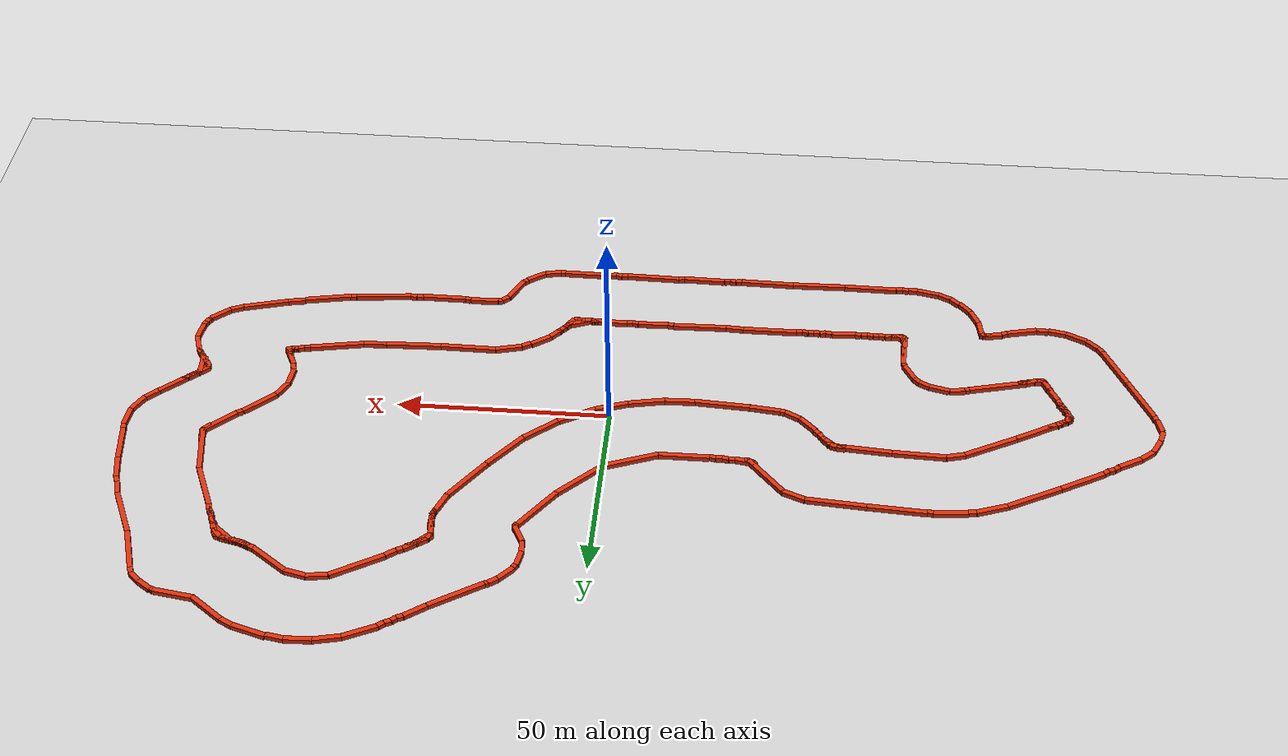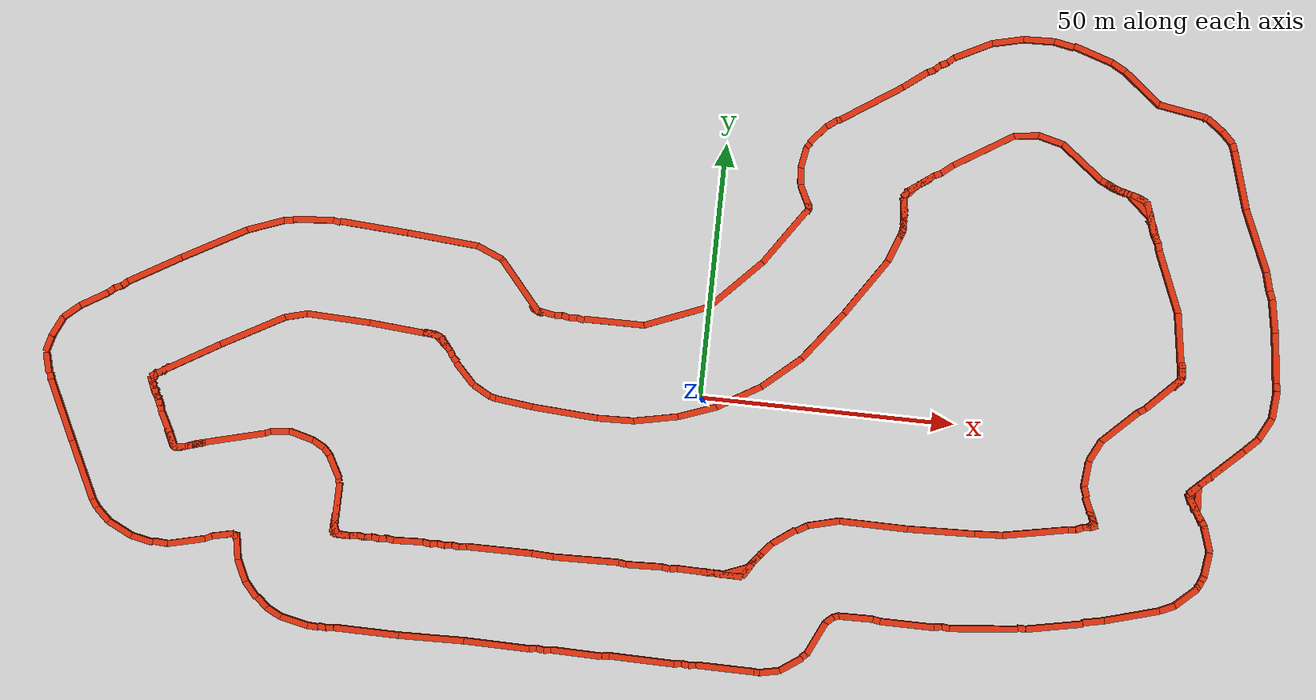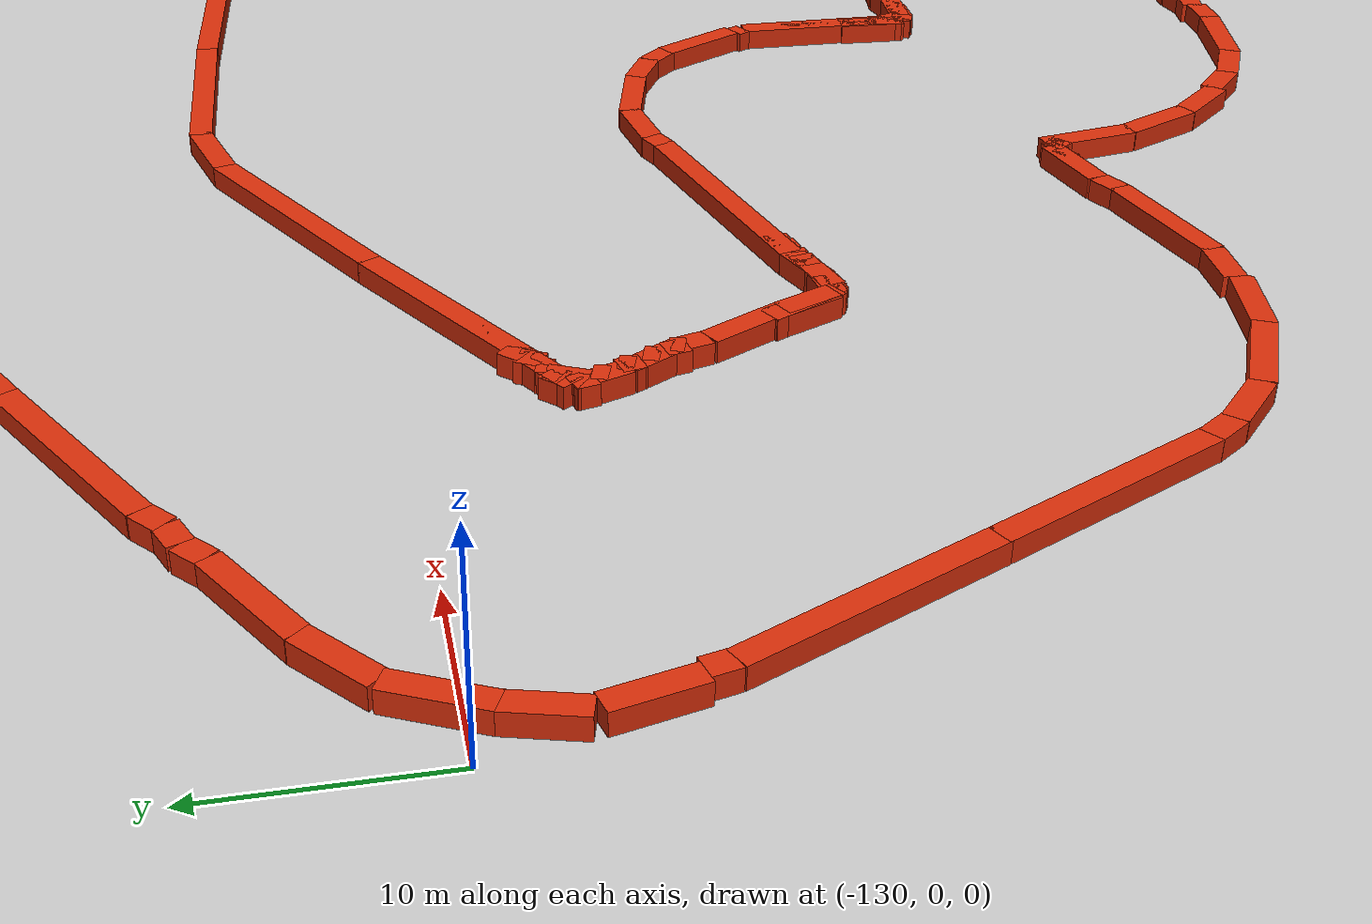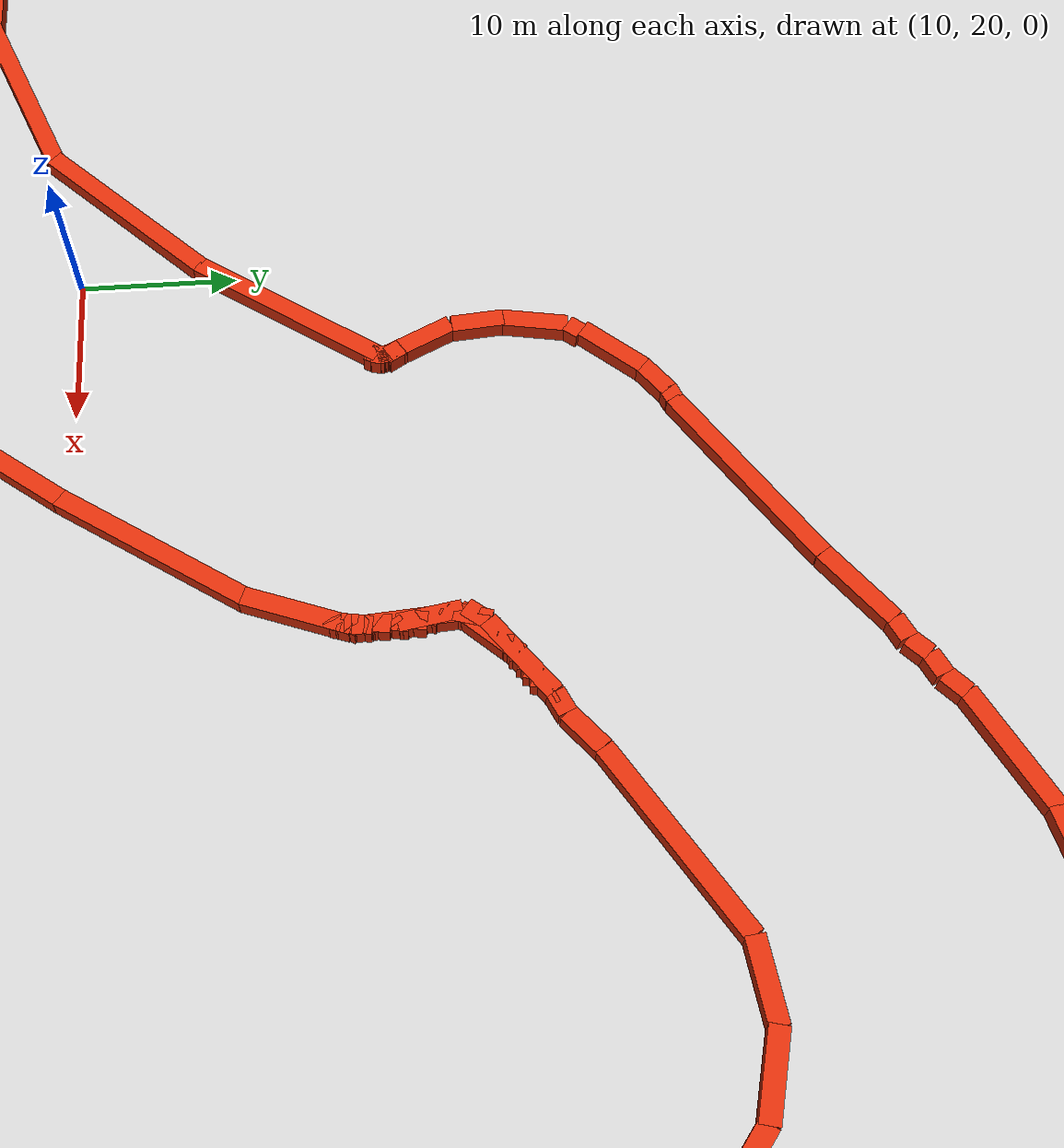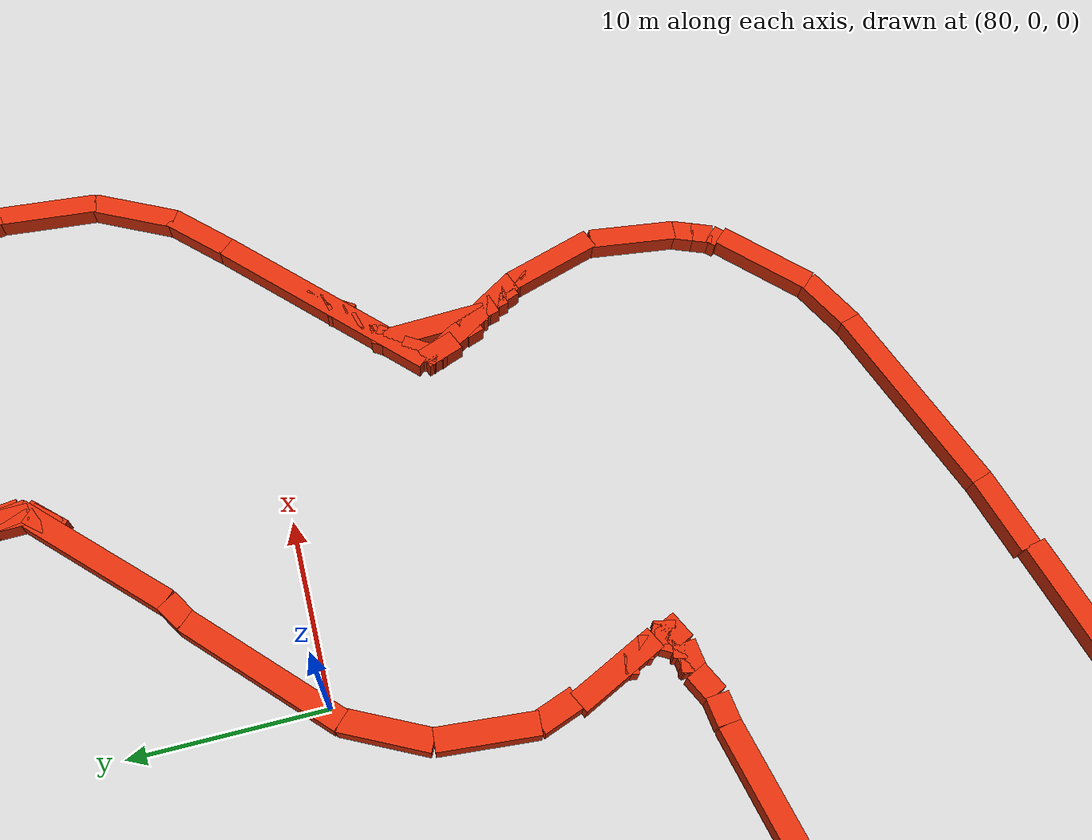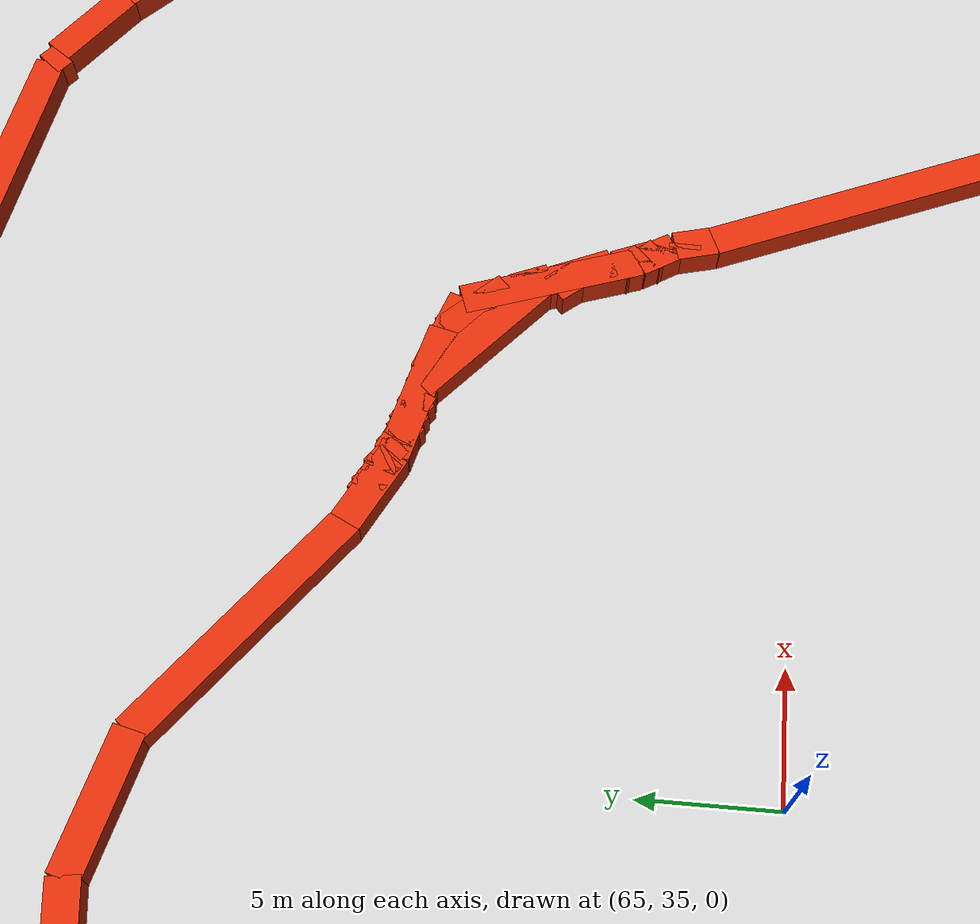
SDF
<sdf version="1.6">
 <world name="default">
  <scene>
   <ambient>0.45 0.45 0.50 1</ambient>
   <background>0.55 0.78 0.98 1</background>
   <shadows>true</shadows>
   <sky>
    <clouds>
     <speed>4</speed>
     <direction>1.2</direction>
     <humidity>0.45</humidity>
     <mean_size>0.55</mean_size>
     <ambient>0.85 0.85 0.85 1</ambient>
    </clouds>
   </sky>
  </scene>
  <light name="sun" type="directional">
   <pose>0.00 -125.5 0.0 0 0 1.5430</pose>
   <diffuse>1.00 0.93 0.80 1</diffuse>
   <specular>0.45 0.45 0.40 1</specular>
   <attenuation>
    <range>1000</range>
    <constant>0.9</constant>
    <linear>0.01</linear>
    <quadratic>0.001</quadratic>
   </attenuation>
   <direction>-0.45 0.25 -0.85</direction>
  </light>
  <include><uri>model://ground_plane</uri></include>
  <model name="track_inner_guardrail">
   <static>true</static>
   <link name="seg_000">
    <pose>-68.76 -33.00 0.55 0 0 -1.2416</pose>
    <collision name="col"><geometry><box><size>2.11 1.20 1.1</size></box></geometry></collision>
    <visual name="vis">
     <geometry><box><size>2.11 1.20 1.1</size></box></geometry>
     <material>
      <ambient>0.35 0.08 0.02 1</ambient>
      <diffuse>0.85 0.18 0.04 1</diffuse>
      <specular>0.2 0.2 0.2 1</specular>
     </material>
    </visual>
   </link>
   <link name="seg_001">
    <pose>-67.07 -34.06 0.55 0 0 -0.0841</pose>
    <collision name="col"><geometry><box><size>2.74 1.20 1.1</size></box></geometry></collision>
    <visual name="vis">
     <geometry><box><size>2.74 1.20 1.1</size></box></geometry>
     <material>
      <ambient>0.35 0.08 0.02 1</ambient>
      <diffuse>0.85 0.18 0.04 1</diffuse>
      <specular>0.2 0.2 0.2 1</specular>
     </material>
    </visual>
   </link>
   <link name="seg_002">
    <pose>-64.99 -34.04 0.55 0 0 0.1797</pose>
    <collision name="col"><geometry><box><size>1.47 1.20 1.1</size></box></geometry></collision>
    <visual name="vis">
     <geometry><box><size>1.47 1.20 1.1</size></box></geometry>
     <material>
      <ambient>0.35 0.08 0.02 1</ambient>
      <diffuse>0.85 0.18 0.04 1</diffuse>
      <specular>0.2 0.2 0.2 1</specular>
     </material>
    </visual>
   </link>
   <link name="seg_003">
    <pose>-63.54 -34.03 0.55 0 0 -0.1643</pose>
    <collision name="col"><geometry><box><size>1.47 1.20 1.1</size></box></geometry></collision>
    <visual name="vis">
     <geometry><box><size>1.47 1.20 1.1</size></box></geometry>
     <material>
      <ambient>0.35 0.08 0.02 1</ambient>
      <diffuse>0.85 0.18 0.04 1</diffuse>
      <specular>0.2 0.2 0.2 1</specular>
     </material>
    </visual>
   </link>
   <link name="seg_004">
    <pose>-62.10 -34.02 0.55 0 0 0.1773</pose>
    <collision name="col"><geometry><box><size>1.46 1.20 1.1</size></box></geometry></collision>
    <visual name="vis">
     <geometry><box><size>1.46 1.20 1.1</size></box></geometry>
     <material>
      <ambient>0.35 0.08 0.02 1</ambient>
      <diffuse>0.85 0.18 0.04 1</diffuse>
      <specular>0.2 0.2 0.2 1</specular>
     </material>
    </visual>
   </link>
   <link name="seg_005">
    <pose>-60.66 -34.01 0.55 0 0 -0.1672</pose>
    <collision name="col"><geometry><box><size>1.46 1.20 1.1</size></box></geometry></collision>
    <visual name="vis">
     <geometry><box><size>1.46 1.20 1.1</size></box></geometry>
     <material>
      <ambient>0.35 0.08 0.02 1</ambient>
      <diffuse>0.85 0.18 0.04 1</diffuse>
      <specular>0.2 0.2 0.2 1</specular>
     </material>
    </visual>
   </link>
   <link name="seg_006">
    <pose>-59.22 -34.01 0.55 0 0 0.1763</pose>
    <collision name="col"><geometry><box><size>1.46 1.20 1.1</size></box></geometry></collision>
    <visual name="vis">
     <geometry><box><size>1.46 1.20 1.1</size></box></geometry>
     <material>
      <ambient>0.35 0.08 0.02 1</ambient>
      <diffuse>0.85 0.18 0.04 1</diffuse>
      <specular>0.2 0.2 0.2 1</specular>
     </material>
    </visual>
   </link>
   <link name="seg_007">
    <pose>-57.78 -34.00 0.55 0 0 -0.1686</pose>
    <collision name="col"><geometry><box><size>1.46 1.20 1.1</size></box></geometry></collision>
    <visual name="vis">
     <geometry><box><size>1.46 1.20 1.1</size></box></geometry>
     <material>
      <ambient>0.35 0.08 0.02 1</ambient>
      <diffuse>0.85 0.18 0.04 1</diffuse>
      <specular>0.2 0.2 0.2 1</specular>
     </material>
    </visual>
   </link>
   <link name="seg_008">
    <pose>-54.19 -33.99 0.55 0 0 0.0454</pose>
    <collision name="col"><geometry><box><size>5.75 1.20 1.1</size></box></geometry></collision>
    <visual name="vis">
     <geometry><box><size>5.75 1.20 1.1</size></box></geometry>
     <material>
      <ambient>0.35 0.08 0.02 1</ambient>
      <diffuse>0.85 0.18 0.04 1</diffuse>
      <specular>0.2 0.2 0.2 1</specular>
     </material>
    </visual>
   </link>
   <link name="seg_009">
    <pose>-50.60 -33.99 0.55 0 0 -0.1711</pose>
    <collision name="col"><geometry><box><size>1.46 1.20 1.1</size></box></geometry></collision>
    <visual name="vis">
     <geometry><box><size>1.46 1.20 1.1</size></box></geometry>
     <material>
      <ambient>0.35 0.08 0.02 1</ambient>
      <diffuse>0.85 0.18 0.04 1</diffuse>
      <specular>0.2 0.2 0.2 1</specular>
     </material>
    </visual>
   </link>
   <link name="seg_010">
    <pose>-49.16 -33.99 0.55 0 0 0.1728</pose>
    <collision name="col"><geometry><box><size>1.46 1.20 1.1</size></box></geometry></collision>
    <visual name="vis">
     <geometry><box><size>1.46 1.20 1.1</size></box></geometry>
     <material>
      <ambient>0.35 0.08 0.02 1</ambient>
      <diffuse>0.85 0.18 0.04 1</diffuse>
      <specular>0.2 0.2 0.2 1</specular>
     </material>
    </visual>
   </link>
   <link name="seg_011">
    <pose>-47.73 -33.99 0.55 0 0 -0.1725</pose>
    <collision name="col"><geometry><box><size>1.46 1.20 1.1</size></box></geometry></collision>
    <visual name="vis">
     <geometry><box><size>1.46 1.20 1.1</size></box></geometry>
     <material>
      <ambient>0.35 0.08 0.02 1</ambient>
      <diffuse>0.85 0.18 0.04 1</diffuse>
      <specular>0.2 0.2 0.2 1</specular>
     </material>
    </visual>
   </link>
   <link name="seg_012">
    <pose>-46.30 -33.99 0.55 0 0 0.1732</pose>
    <collision name="col"><geometry><box><size>1.45 1.20 1.1</size></box></geometry></collision>
    <visual name="vis">
     <geometry><box><size>1.45 1.20 1.1</size></box></geometry>
     <material>
      <ambient>0.35 0.08 0.02 1</ambient>
      <diffuse>0.85 0.18 0.04 1</diffuse>
      <specular>0.2 0.2 0.2 1</specular>
     </material>
    </visual>
   </link>
   <link name="seg_013">
    <pose>-44.86 -33.99 0.55 0 0 -0.1718</pose>
    <collision name="col"><geometry><box><size>1.46 1.20 1.1</size></box></geometry></collision>
    <visual name="vis">
     <geometry><box><size>1.46 1.20 1.1</size></box></geometry>
     <material>
      <ambient>0.35 0.08 0.02 1</ambient>
      <diffuse>0.85 0.18 0.04 1</diffuse>
      <specular>0.2 0.2 0.2 1</specular>
     </material>
    </visual>
   </link>
   <link name="seg_014">
    <pose>-43.43 -33.99 0.55 0 0 0.1718</pose>
    <collision name="col"><geometry><box><size>1.46 1.20 1.1</size></box></geometry></collision>
    <visual name="vis">
     <geometry><box><size>1.46 1.20 1.1</size></box></geometry>
     <material>
      <ambient>0.35 0.08 0.02 1</ambient>
      <diffuse>0.85 0.18 0.04 1</diffuse>
      <specular>0.2 0.2 0.2 1</specular>
     </material>
    </visual>
   </link>
   <link name="seg_015">
    <pose>-36.27 -33.86 0.55 0 0 0.0002</pose>
    <collision name="col"><geometry><box><size>13.00 1.20 1.1</size></box></geometry></collision>
    <visual name="vis">
     <geometry><box><size>13.00 1.20 1.1</size></box></geometry>
     <material>
      <ambient>0.35 0.08 0.02 1</ambient>
      <diffuse>0.85 0.18 0.04 1</diffuse>
      <specular>0.2 0.2 0.2 1</specular>
     </material>
    </visual>
   </link>
   <link name="seg_016">
    <pose>-27.68 -33.98 0.55 0 0 -0.0575</pose>
    <collision name="col"><geometry><box><size>4.30 1.20 1.1</size></box></geometry></collision>
    <visual name="vis">
     <geometry><box><size>4.30 1.20 1.1</size></box></geometry>
     <material>
      <ambient>0.35 0.08 0.02 1</ambient>
      <diffuse>0.85 0.18 0.04 1</diffuse>
      <specular>0.2 0.2 0.2 1</specular>
     </material>
    </visual>
   </link>
   <link name="seg_017">
    <pose>-19.10 -33.97 0.55 0 0 0.0207</pose>
    <collision name="col"><geometry><box><size>12.89 1.20 1.1</size></box></geometry></collision>
    <visual name="vis">
     <geometry><box><size>12.89 1.20 1.1</size></box></geometry>
     <material>
      <ambient>0.35 0.08 0.02 1</ambient>
      <diffuse>0.85 0.18 0.04 1</diffuse>
      <specular>0.2 0.2 0.2 1</specular>
     </material>
    </visual>
   </link>
   <link name="seg_018">
    <pose>-11.94 -33.96 0.55 0 0 -0.1715</pose>
    <collision name="col"><geometry><box><size>1.45 1.20 1.1</size></box></geometry></collision>
    <visual name="vis">
     <geometry><box><size>1.45 1.20 1.1</size></box></geometry>
     <material>
      <ambient>0.35 0.08 0.02 1</ambient>
      <diffuse>0.85 0.18 0.04 1</diffuse>
      <specular>0.2 0.2 0.2 1</specular>
     </material>
    </visual>
   </link>
   <link name="seg_019">
    <pose>-7.63 -33.96 0.55 0 0 0.0351</pose>
    <collision name="col"><geometry><box><size>7.18 1.20 1.1</size></box></geometry></collision>
    <visual name="vis">
     <geometry><box><size>7.18 1.20 1.1</size></box></geometry>
     <material>
      <ambient>0.35 0.08 0.02 1</ambient>
      <diffuse>0.85 0.18 0.04 1</diffuse>
      <specular>0.2 0.2 0.2 1</specular>
     </material>
    </visual>
   </link>
   <link name="seg_020">
    <pose>-3.33 -33.96 0.55 0 0 -0.1732</pose>
    <collision name="col"><geometry><box><size>1.46 1.20 1.1</size></box></geometry></collision>
    <visual name="vis">
     <geometry><box><size>1.46 1.20 1.1</size></box></geometry>
     <material>
      <ambient>0.35 0.08 0.02 1</ambient>
      <diffuse>0.85 0.18 0.04 1</diffuse>
      <specular>0.2 0.2 0.2 1</specular>
     </material>
    </visual>
   </link>
   <link name="seg_021">
    <pose>-1.89 -33.96 0.55 0 0 0.1707</pose>
    <collision name="col"><geometry><box><size>1.46 1.20 1.1</size></box></geometry></collision>
    <visual name="vis">
     <geometry><box><size>1.46 1.20 1.1</size></box></geometry>
     <material>
      <ambient>0.35 0.08 0.02 1</ambient>
      <diffuse>0.85 0.18 0.04 1</diffuse>
      <specular>0.2 0.2 0.2 1</specular>
     </material>
    </visual>
   </link>
   <link name="seg_022">
    <pose>5.30 -33.99 0.55 0 0 -0.0240</pose>
    <collision name="col"><geometry><box><size>12.95 1.20 1.1</size></box></geometry></collision>
    <visual name="vis">
     <geometry><box><size>12.95 1.20 1.1</size></box></geometry>
     <material>
      <ambient>0.35 0.08 0.02 1</ambient>
      <diffuse>0.85 0.18 0.04 1</diffuse>
      <specular>0.2 0.2 0.2 1</specular>
     </material>
    </visual>
   </link>
   <link name="seg_023">
    <pose>12.61 -32.78 0.55 0 0 1.0220</pose>
    <collision name="col"><geometry><box><size>3.21 1.20 1.1</size></box></geometry></collision>
    <visual name="vis">
     <geometry><box><size>3.21 1.20 1.1</size></box></geometry>
     <material>
      <ambient>0.35 0.08 0.02 1</ambient>
      <diffuse>0.85 0.18 0.04 1</diffuse>
      <specular>0.2 0.2 0.2 1</specular>
     </material>
    </visual>
   </link>
   <link name="seg_024">
    <pose>13.56 -31.17 0.55 0 0 1.1524</pose>
    <collision name="col"><geometry><box><size>0.67 1.20 1.1</size></box></geometry></collision>
    <visual name="vis">
     <geometry><box><size>0.67 1.20 1.1</size></box></geometry>
     <material>
      <ambient>0.35 0.08 0.02 1</ambient>
      <diffuse>0.85 0.18 0.04 1</diffuse>
      <specular>0.2 0.2 0.2 1</specular>
     </material>
    </visual>
   </link>
   <link name="seg_025">
    <pose>14.11 -30.42 0.55 0 0 0.8469</pose>
    <collision name="col"><geometry><box><size>1.45 1.20 1.1</size></box></geometry></collision>
    <visual name="vis">
     <geometry><box><size>1.45 1.20 1.1</size></box></geometry>
     <material>
      <ambient>0.35 0.08 0.02 1</ambient>
      <diffuse>0.85 0.18 0.04 1</diffuse>
      <specular>0.2 0.2 0.2 1</specular>
     </material>
    </visual>
   </link>
   <link name="seg_038">
    <pose>14.81 -29.48 0.55 0 0 -2.1153</pose>
    <collision name="col"><geometry><box><size>0.79 1.20 1.1</size></box></geometry></collision>
    <visual name="vis">
     <geometry><box><size>0.79 1.20 1.1</size></box></geometry>
     <material>
      <ambient>0.35 0.08 0.02 1</ambient>
      <diffuse>0.85 0.18 0.04 1</diffuse>
      <specular>0.2 0.2 0.2 1</specular>
     </material>
    </visual>
   </link>
   <link name="seg_039">
    <pose>13.76 -30.94 0.55 0 0 -2.2137</pose>
    <collision name="col"><geometry><box><size>3.06 1.20 1.1</size></box></geometry></collision>
    <visual name="vis">
     <geometry><box><size>3.06 1.20 1.1</size></box></geometry>
     <material>
      <ambient>0.35 0.08 0.02 1</ambient>
      <diffuse>0.85 0.18 0.04 1</diffuse>
      <specular>0.2 0.2 0.2 1</specular>
     </material>
    </visual>
   </link>
   <link name="seg_040">
    <pose>10.44 -33.08 0.55 0 0 -2.7667</pose>
    <collision name="col"><geometry><box><size>5.35 1.20 1.1</size></box></geometry></collision>
    <visual name="vis">
     <geometry><box><size>5.35 1.20 1.1</size></box></geometry>
     <material>
      <ambient>0.35 0.08 0.02 1</ambient>
      <diffuse>0.85 0.18 0.04 1</diffuse>
      <specular>0.2 0.2 0.2 1</specular>
     </material>
    </visual>
   </link>
   <link name="seg_041">
    <pose>7.30 -33.90 0.55 0 0 -2.7241</pose>
    <collision name="col"><geometry><box><size>0.57 1.20 1.1</size></box></geometry></collision>
    <visual name="vis">
     <geometry><box><size>0.57 1.20 1.1</size></box></geometry>
     <material>
      <ambient>0.35 0.08 0.02 1</ambient>
      <diffuse>0.85 0.18 0.04 1</diffuse>
      <specular>0.2 0.2 0.2 1</specular>
     </material>
    </visual>
   </link>
   <link name="seg_042">
    <pose>6.69 -33.94 0.55 0 0 -2.7241</pose>
    <collision name="col"><geometry><box><size>0.57 1.20 1.1</size></box></geometry></collision>
    <visual name="vis">
     <geometry><box><size>0.57 1.20 1.1</size></box></geometry>
     <material>
      <ambient>0.35 0.08 0.02 1</ambient>
      <diffuse>0.85 0.18 0.04 1</diffuse>
      <specular>0.2 0.2 0.2 1</specular>
     </material>
    </visual>
   </link>
   <link name="seg_043">
    <pose>6.07 -33.97 0.55 0 0 -2.7241</pose>
    <collision name="col"><geometry><box><size>0.57 1.20 1.1</size></box></geometry></collision>
    <visual name="vis">
     <geometry><box><size>0.57 1.20 1.1</size></box></geometry>
     <material>
      <ambient>0.35 0.08 0.02 1</ambient>
      <diffuse>0.85 0.18 0.04 1</diffuse>
      <specular>0.2 0.2 0.2 1</specular>
     </material>
    </visual>
   </link>
   <link name="seg_044">
    <pose>5.46 -34.00 0.55 0 0 -2.7241</pose>
    <collision name="col"><geometry><box><size>0.45 1.20 1.1</size></box></geometry></collision>
    <visual name="vis">
     <geometry><box><size>0.45 1.20 1.1</size></box></geometry>
     <material>
      <ambient>0.35 0.08 0.02 1</ambient>
      <diffuse>0.85 0.18 0.04 1</diffuse>
      <specular>0.2 0.2 0.2 1</specular>
     </material>
    </visual>
   </link>
   <link name="seg_045">
    <pose>4.65 -33.88 0.55 0 0 -2.7241</pose>
    <collision name="col"><geometry><box><size>0.57 1.20 1.1</size></box></geometry></collision>
    <visual name="vis">
     <geometry><box><size>0.57 1.20 1.1</size></box></geometry>
     <material>
      <ambient>0.35 0.08 0.02 1</ambient>
      <diffuse>0.85 0.18 0.04 1</diffuse>
      <specular>0.2 0.2 0.2 1</specular>
     </material>
    </visual>
   </link>
   <link name="seg_046">
    <pose>4.03 -33.91 0.55 0 0 -2.7241</pose>
    <collision name="col"><geometry><box><size>0.57 1.20 1.1</size></box></geometry></collision>
    <visual name="vis">
     <geometry><box><size>0.57 1.20 1.1</size></box></geometry>
     <material>
      <ambient>0.35 0.08 0.02 1</ambient>
      <diffuse>0.85 0.18 0.04 1</diffuse>
      <specular>0.2 0.2 0.2 1</specular>
     </material>
    </visual>
   </link>
   <link name="seg_047">
    <pose>3.37 -33.96 0.55 0 0 1.2462</pose>
    <collision name="col"><geometry><box><size>0.23 1.20 1.1</size></box></geometry></collision>
    <visual name="vis">
     <geometry><box><size>0.23 1.20 1.1</size></box></geometry>
     <material>
      <ambient>0.35 0.08 0.02 1</ambient>
      <diffuse>0.85 0.18 0.04 1</diffuse>
      <specular>0.2 0.2 0.2 1</specular>
     </material>
    </visual>
   </link>
   <link name="seg_048">
    <pose>4.01 -34.02 0.55 0 0 0.3904</pose>
    <collision name="col"><geometry><box><size>0.33 1.20 1.1</size></box></geometry></collision>
    <visual name="vis">
     <geometry><box><size>0.33 1.20 1.1</size></box></geometry>
     <material>
      <ambient>0.35 0.08 0.02 1</ambient>
      <diffuse>0.85 0.18 0.04 1</diffuse>
      <specular>0.2 0.2 0.2 1</specular>
     </material>
    </visual>
   </link>
   <link name="seg_049">
    <pose>4.41 -33.99 0.55 0 0 1.2462</pose>
    <collision name="col"><geometry><box><size>0.23 1.20 1.1</size></box></geometry></collision>
    <visual name="vis">
     <geometry><box><size>0.23 1.20 1.1</size></box></geometry>
     <material>
      <ambient>0.35 0.08 0.02 1</ambient>
      <diffuse>0.85 0.18 0.04 1</diffuse>
      <specular>0.2 0.2 0.2 1</specular>
     </material>
    </visual>
   </link>
   <link name="seg_050">
    <pose>5.66 -34.02 0.55 0 0 0.0243</pose>
    <collision name="col"><geometry><box><size>2.12 1.20 1.1</size></box></geometry></collision>
    <visual name="vis">
     <geometry><box><size>2.12 1.20 1.1</size></box></geometry>
     <material>
      <ambient>0.35 0.08 0.02 1</ambient>
      <diffuse>0.85 0.18 0.04 1</diffuse>
      <specular>0.2 0.2 0.2 1</specular>
     </material>
    </visual>
   </link>
   <link name="seg_051">
    <pose>7.89 -34.06 0.55 0 0 0.0243</pose>
    <collision name="col"><geometry><box><size>2.12 1.20 1.1</size></box></geometry></collision>
    <visual name="vis">
     <geometry><box><size>2.12 1.20 1.1</size></box></geometry>
     <material>
      <ambient>0.35 0.08 0.02 1</ambient>
      <diffuse>0.85 0.18 0.04 1</diffuse>
      <specular>0.2 0.2 0.2 1</specular>
     </material>
    </visual>
   </link>
   <link name="seg_052">
    <pose>10.01 -34.05 0.55 0 0 0.0766</pose>
    <collision name="col"><geometry><box><size>1.89 1.20 1.1</size></box></geometry></collision>
    <visual name="vis">
     <geometry><box><size>1.89 1.20 1.1</size></box></geometry>
     <material>
      <ambient>0.35 0.08 0.02 1</ambient>
      <diffuse>0.85 0.18 0.04 1</diffuse>
      <specular>0.2 0.2 0.2 1</specular>
     </material>
    </visual>
   </link>
   <link name="seg_053">
    <pose>14.02 -30.56 0.55 0 0 0.8808</pose>
    <collision name="col"><geometry><box><size>9.22 1.20 1.1</size></box></geometry></collision>
    <visual name="vis">
     <geometry><box><size>9.22 1.20 1.1</size></box></geometry>
     <material>
      <ambient>0.35 0.08 0.02 1</ambient>
      <diffuse>0.85 0.18 0.04 1</diffuse>
      <specular>0.2 0.2 0.2 1</specular>
     </material>
    </visual>
   </link>
   <link name="seg_054">
    <pose>19.08 -25.47 0.55 0 0 0.6311</pose>
    <collision name="col"><geometry><box><size>5.49 1.20 1.1</size></box></geometry></collision>
    <visual name="vis">
     <geometry><box><size>5.49 1.20 1.1</size></box></geometry>
     <material>
      <ambient>0.35 0.08 0.02 1</ambient>
      <diffuse>0.85 0.18 0.04 1</diffuse>
      <specular>0.2 0.2 0.2 1</specular>
     </material>
    </visual>
   </link>
   <link name="seg_055">
    <pose>22.42 -23.45 0.55 0 0 0.5600</pose>
    <collision name="col"><geometry><box><size>2.43 1.20 1.1</size></box></geometry></collision>
    <visual name="vis">
     <geometry><box><size>2.43 1.20 1.1</size></box></geometry>
     <material>
      <ambient>0.35 0.08 0.02 1</ambient>
      <diffuse>0.85 0.18 0.04 1</diffuse>
      <specular>0.2 0.2 0.2 1</specular>
     </material>
    </visual>
   </link>
   <link name="seg_056">
    <pose>26.50 -22.02 0.55 0 0 0.2502</pose>
    <collision name="col"><geometry><box><size>6.42 1.20 1.1</size></box></geometry></collision>
    <visual name="vis">
     <geometry><box><size>6.42 1.20 1.1</size></box></geometry>
     <material>
      <ambient>0.35 0.08 0.02 1</ambient>
      <diffuse>0.85 0.18 0.04 1</diffuse>
      <specular>0.2 0.2 0.2 1</specular>
     </material>
    </visual>
   </link>
   <link name="seg_057">
    <pose>36.24 -21.32 0.55 0 0 -0.0123</pose>
    <collision name="col"><geometry><box><size>13.50 1.20 1.1</size></box></geometry></collision>
    <visual name="vis">
     <geometry><box><size>13.50 1.20 1.1</size></box></geometry>
     <material>
      <ambient>0.35 0.08 0.02 1</ambient>
      <diffuse>0.85 0.18 0.04 1</diffuse>
      <specular>0.2 0.2 0.2 1</specular>
     </material>
    </visual>
   </link>
   <link name="seg_058">
    <pose>49.57 -21.20 0.55 0 0 0.0306</pose>
    <collision name="col"><geometry><box><size>13.40 1.20 1.1</size></box></geometry></collision>
    <visual name="vis">
     <geometry><box><size>13.40 1.20 1.1</size></box></geometry>
     <material>
      <ambient>0.35 0.08 0.02 1</ambient>
      <diffuse>0.85 0.18 0.04 1</diffuse>
      <specular>0.2 0.2 0.2 1</specular>
     </material>
    </visual>
   </link>
   <link name="seg_059">
    <pose>58.99 -20.84 0.55 0 0 0.0556</pose>
    <collision name="col"><geometry><box><size>5.57 1.20 1.1</size></box></geometry></collision>
    <visual name="vis">
     <geometry><box><size>5.57 1.20 1.1</size></box></geometry>
     <material>
      <ambient>0.35 0.08 0.02 1</ambient>
      <diffuse>0.85 0.18 0.04 1</diffuse>
      <specular>0.2 0.2 0.2 1</specular>
     </material>
    </visual>
   </link>
   <link name="seg_060">
    <pose>68.11 -19.48 0.55 0 0 0.1882</pose>
    <collision name="col"><geometry><box><size>12.91 1.20 1.1</size></box></geometry></collision>
    <visual name="vis">
     <geometry><box><size>12.91 1.20 1.1</size></box></geometry>
     <material>
      <ambient>0.35 0.08 0.02 1</ambient>
      <diffuse>0.85 0.18 0.04 1</diffuse>
      <specular>0.2 0.2 0.2 1</specular>
     </material>
    </visual>
   </link>
   <link name="seg_061">
    <pose>75.18 -18.21 0.55 0 0 0.0849</pose>
    <collision name="col"><geometry><box><size>1.46 1.20 1.1</size></box></geometry></collision>
    <visual name="vis">
     <geometry><box><size>1.46 1.20 1.1</size></box></geometry>
     <material>
      <ambient>0.35 0.08 0.02 1</ambient>
      <diffuse>0.85 0.18 0.04 1</diffuse>
      <specular>0.2 0.2 0.2 1</specular>
     </material>
    </visual>
   </link>
   <link name="seg_062">
    <pose>76.58 -17.85 0.55 0 0 0.4251</pose>
    <collision name="col"><geometry><box><size>1.47 1.20 1.1</size></box></geometry></collision>
    <visual name="vis">
     <geometry><box><size>1.47 1.20 1.1</size></box></geometry>
     <material>
      <ambient>0.35 0.08 0.02 1</ambient>
      <diffuse>0.85 0.18 0.04 1</diffuse>
      <specular>0.2 0.2 0.2 1</specular>
     </material>
    </visual>
   </link>
   <link name="seg_063">
    <pose>77.98 -17.48 0.55 0 0 0.0821</pose>
    <collision name="col"><geometry><box><size>1.47 1.20 1.1</size></box></geometry></collision>
    <visual name="vis">
     <geometry><box><size>1.47 1.20 1.1</size></box></geometry>
     <material>
      <ambient>0.35 0.08 0.02 1</ambient>
      <diffuse>0.85 0.18 0.04 1</diffuse>
      <specular>0.2 0.2 0.2 1</specular>
     </material>
    </visual>
   </link>
   <link name="seg_064">
    <pose>79.37 -17.13 0.55 0 0 0.4241</pose>
    <collision name="col"><geometry><box><size>1.45 1.20 1.1</size></box></geometry></collision>
    <visual name="vis">
     <geometry><box><size>1.45 1.20 1.1</size></box></geometry>
     <material>
      <ambient>0.35 0.08 0.02 1</ambient>
      <diffuse>0.85 0.18 0.04 1</diffuse>
      <specular>0.2 0.2 0.2 1</specular>
     </material>
    </visual>
   </link>
   <link name="seg_065">
    <pose>78.41 -14.64 0.55 0 0 -1.7864</pose>
    <collision name="col"><geometry><box><size>0.67 1.20 1.1</size></box></geometry></collision>
    <visual name="vis">
     <geometry><box><size>0.67 1.20 1.1</size></box></geometry>
     <material>
      <ambient>0.35 0.08 0.02 1</ambient>
      <diffuse>0.85 0.18 0.04 1</diffuse>
      <specular>0.2 0.2 0.2 1</specular>
     </material>
    </visual>
   </link>
   <link name="seg_066">
    <pose>78.95 -15.54 0.55 0 0 -1.7864</pose>
    <collision name="col"><geometry><box><size>0.67 1.20 1.1</size></box></geometry></collision>
    <visual name="vis">
     <geometry><box><size>0.67 1.20 1.1</size></box></geometry>
     <material>
      <ambient>0.35 0.08 0.02 1</ambient>
      <diffuse>0.85 0.18 0.04 1</diffuse>
      <specular>0.2 0.2 0.2 1</specular>
     </material>
    </visual>
   </link>
   <link name="seg_067">
    <pose>79.42 -16.71 0.55 0 0 -1.7864</pose>
    <collision name="col"><geometry><box><size>1.09 1.20 1.1</size></box></geometry></collision>
    <visual name="vis">
     <geometry><box><size>1.09 1.20 1.1</size></box></geometry>
     <material>
      <ambient>0.35 0.08 0.02 1</ambient>
      <diffuse>0.85 0.18 0.04 1</diffuse>
      <specular>0.2 0.2 0.2 1</specular>
     </material>
    </visual>
   </link>
   <link name="seg_068">
    <pose>78.60 -17.14 0.55 0 0 -1.7864</pose>
    <collision name="col"><geometry><box><size>0.67 1.20 1.1</size></box></geometry></collision>
    <visual name="vis">
     <geometry><box><size>0.67 1.20 1.1</size></box></geometry>
     <material>
      <ambient>0.35 0.08 0.02 1</ambient>
      <diffuse>0.85 0.18 0.04 1</diffuse>
      <specular>0.2 0.2 0.2 1</specular>
     </material>
    </visual>
   </link>
   <link name="seg_069">
    <pose>77.83 -17.30 0.55 0 0 -1.7864</pose>
    <collision name="col"><geometry><box><size>0.67 1.20 1.1</size></box></geometry></collision>
    <visual name="vis">
     <geometry><box><size>0.67 1.20 1.1</size></box></geometry>
     <material>
      <ambient>0.35 0.08 0.02 1</ambient>
      <diffuse>0.85 0.18 0.04 1</diffuse>
      <specular>0.2 0.2 0.2 1</specular>
     </material>
    </visual>
   </link>
   <link name="seg_070">
    <pose>79.11 -16.61 0.55 0 0 1.0440</pose>
    <collision name="col"><geometry><box><size>1.47 1.20 1.1</size></box></geometry></collision>
    <visual name="vis">
     <geometry><box><size>1.47 1.20 1.1</size></box></geometry>
     <material>
      <ambient>0.35 0.08 0.02 1</ambient>
      <diffuse>0.85 0.18 0.04 1</diffuse>
      <specular>0.2 0.2 0.2 1</specular>
     </material>
    </visual>
   </link>
   <link name="seg_071">
    <pose>78.22 -13.88 0.55 0 0 2.0104</pose>
    <collision name="col"><geometry><box><size>5.07 1.20 1.1</size></box></geometry></collision>
    <visual name="vis">
     <geometry><box><size>5.07 1.20 1.1</size></box></geometry>
     <material>
      <ambient>0.35 0.08 0.02 1</ambient>
      <diffuse>0.85 0.18 0.04 1</diffuse>
      <specular>0.2 0.2 0.2 1</specular>
     </material>
    </visual>
   </link>
   <link name="seg_072">
    <pose>77.04 -10.53 0.55 0 0 1.9129</pose>
    <collision name="col"><geometry><box><size>2.26 1.20 1.1</size></box></geometry></collision>
    <visual name="vis">
     <geometry><box><size>2.26 1.20 1.1</size></box></geometry>
     <material>
      <ambient>0.35 0.08 0.02 1</ambient>
      <diffuse>0.85 0.18 0.04 1</diffuse>
      <specular>0.2 0.2 0.2 1</specular>
     </material>
    </visual>
   </link>
   <link name="seg_073">
    <pose>76.90 -7.02 0.55 0 0 1.4836</pose>
    <collision name="col"><geometry><box><size>5.14 1.20 1.1</size></box></geometry></collision>
    <visual name="vis">
     <geometry><box><size>5.14 1.20 1.1</size></box></geometry>
     <material>
      <ambient>0.35 0.08 0.02 1</ambient>
      <diffuse>0.85 0.18 0.04 1</diffuse>
      <specular>0.2 0.2 0.2 1</specular>
     </material>
    </visual>
   </link>
   <link name="seg_074">
    <pose>78.13 -2.39 0.55 0 0 1.1110</pose>
    <collision name="col"><geometry><box><size>4.65 1.20 1.1</size></box></geometry></collision>
    <visual name="vis">
     <geometry><box><size>4.65 1.20 1.1</size></box></geometry>
     <material>
      <ambient>0.35 0.08 0.02 1</ambient>
      <diffuse>0.85 0.18 0.04 1</diffuse>
      <specular>0.2 0.2 0.2 1</specular>
     </material>
    </visual>
   </link>
   <link name="seg_075">
    <pose>82.44 2.84 0.55 0 0 0.7689</pose>
    <collision name="col"><geometry><box><size>9.32 1.20 1.1</size></box></geometry></collision>
    <visual name="vis">
     <geometry><box><size>9.32 1.20 1.1</size></box></geometry>
     <material>
      <ambient>0.35 0.08 0.02 1</ambient>
      <diffuse>0.85 0.18 0.04 1</diffuse>
      <specular>0.2 0.2 0.2 1</specular>
     </material>
    </visual>
   </link>
   <link name="seg_076">
    <pose>86.39 6.44 0.55 0 0 0.5611</pose>
    <collision name="col"><geometry><box><size>1.51 1.20 1.1</size></box></geometry></collision>
    <visual name="vis">
     <geometry><box><size>1.51 1.20 1.1</size></box></geometry>
     <material>
      <ambient>0.35 0.08 0.02 1</ambient>
      <diffuse>0.85 0.18 0.04 1</diffuse>
      <specular>0.2 0.2 0.2 1</specular>
     </material>
    </visual>
   </link>
   <link name="seg_077">
    <pose>90.37 10.21 0.55 0 0 0.7905</pose>
    <collision name="col"><geometry><box><size>9.49 1.20 1.1</size></box></geometry></collision>
    <visual name="vis">
     <geometry><box><size>9.49 1.20 1.1</size></box></geometry>
     <material>
      <ambient>0.35 0.08 0.02 1</ambient>
      <diffuse>0.85 0.18 0.04 1</diffuse>
      <specular>0.2 0.2 0.2 1</specular>
     </material>
    </visual>
   </link>
   <link name="seg_078">
    <pose>93.49 15.10 0.55 0 0 1.7155</pose>
    <collision name="col"><geometry><box><size>3.18 1.20 1.1</size></box></geometry></collision>
    <visual name="vis">
     <geometry><box><size>3.18 1.20 1.1</size></box></geometry>
     <material>
      <ambient>0.35 0.08 0.02 1</ambient>
      <diffuse>0.85 0.18 0.04 1</diffuse>
      <specular>0.2 0.2 0.2 1</specular>
     </material>
    </visual>
   </link>
   <link name="seg_079">
    <pose>93.32 14.82 0.55 0 0 -1.5441</pose>
    <collision name="col"><geometry><box><size>3.71 1.20 1.1</size></box></geometry></collision>
    <visual name="vis">
     <geometry><box><size>3.71 1.20 1.1</size></box></geometry>
     <material>
      <ambient>0.35 0.08 0.02 1</ambient>
      <diffuse>0.85 0.18 0.04 1</diffuse>
      <specular>0.2 0.2 0.2 1</specular>
     </material>
    </visual>
   </link>
   <link name="seg_080">
    <pose>92.73 12.30 0.55 0 0 -2.2919</pose>
    <collision name="col"><geometry><box><size>2.05 1.20 1.1</size></box></geometry></collision>
    <visual name="vis">
     <geometry><box><size>2.05 1.20 1.1</size></box></geometry>
     <material>
      <ambient>0.35 0.08 0.02 1</ambient>
      <diffuse>0.85 0.18 0.04 1</diffuse>
      <specular>0.2 0.2 0.2 1</specular>
     </material>
    </visual>
   </link>
   <link name="seg_081">
    <pose>92.84 12.38 0.55 0 0 0.8189</pose>
    <collision name="col"><geometry><box><size>2.33 1.20 1.1</size></box></geometry></collision>
    <visual name="vis">
     <geometry><box><size>2.33 1.20 1.1</size></box></geometry>
     <material>
      <ambient>0.35 0.08 0.02 1</ambient>
      <diffuse>0.85 0.18 0.04 1</diffuse>
      <specular>0.2 0.2 0.2 1</specular>
     </material>
    </visual>
   </link>
   <link name="seg_082">
    <pose>92.53 19.75 0.55 0 0 1.7312</pose>
    <collision name="col"><geometry><box><size>13.41 1.20 1.1</size></box></geometry></collision>
    <visual name="vis">
     <geometry><box><size>13.41 1.20 1.1</size></box></geometry>
     <material>
      <ambient>0.35 0.08 0.02 1</ambient>
      <diffuse>0.85 0.18 0.04 1</diffuse>
      <specular>0.2 0.2 0.2 1</specular>
     </material>
    </visual>
   </link>
   <link name="seg_083">
    <pose>89.01 32.16 0.55 0 0 1.9696</pose>
    <collision name="col"><geometry><box><size>12.81 1.20 1.1</size></box></geometry></collision>
    <visual name="vis">
     <geometry><box><size>12.81 1.20 1.1</size></box></geometry>
     <material>
      <ambient>0.35 0.08 0.02 1</ambient>
      <diffuse>0.85 0.18 0.04 1</diffuse>
      <specular>0.2 0.2 0.2 1</specular>
     </material>
    </visual>
   </link>
   <link name="seg_084">
    <pose>86.35 38.77 0.55 0 0 1.8204</pose>
    <collision name="col"><geometry><box><size>1.58 1.20 1.1</size></box></geometry></collision>
    <visual name="vis">
     <geometry><box><size>1.58 1.20 1.1</size></box></geometry>
     <material>
      <ambient>0.35 0.08 0.02 1</ambient>
      <diffuse>0.85 0.18 0.04 1</diffuse>
      <specular>0.2 0.2 0.2 1</specular>
     </material>
    </visual>
   </link>
   <link name="seg_085">
    <pose>85.73 40.23 0.55 0 0 2.1179</pose>
    <collision name="col"><geometry><box><size>1.62 1.20 1.1</size></box></geometry></collision>
    <visual name="vis">
     <geometry><box><size>1.62 1.20 1.1</size></box></geometry>
     <material>
      <ambient>0.35 0.08 0.02 1</ambient>
      <diffuse>0.85 0.18 0.04 1</diffuse>
      <specular>0.2 0.2 0.2 1</specular>
     </material>
    </visual>
   </link>
   <link name="seg_086">
    <pose>84.21 44.13 0.55 0 0 1.9013</pose>
    <collision name="col"><geometry><box><size>6.91 1.20 1.1</size></box></geometry></collision>
    <visual name="vis">
     <geometry><box><size>6.91 1.20 1.1</size></box></geometry>
     <material>
      <ambient>0.35 0.08 0.02 1</ambient>
      <diffuse>0.85 0.18 0.04 1</diffuse>
      <specular>0.2 0.2 0.2 1</specular>
     </material>
    </visual>
   </link>
   <link name="seg_087">
    <pose>81.55 47.90 0.55 0 0 2.7996</pose>
    <collision name="col"><geometry><box><size>3.43 1.20 1.1</size></box></geometry></collision>
    <visual name="vis">
     <geometry><box><size>3.43 1.20 1.1</size></box></geometry>
     <material>
      <ambient>0.35 0.08 0.02 1</ambient>
      <diffuse>0.85 0.18 0.04 1</diffuse>
      <specular>0.2 0.2 0.2 1</specular>
     </material>
    </visual>
   </link>
   <link name="seg_088">
    <pose>79.51 48.50 0.55 0 0 2.7158</pose>
    <collision name="col"><geometry><box><size>0.64 1.20 1.1</size></box></geometry></collision>
    <visual name="vis">
     <geometry><box><size>0.64 1.20 1.1</size></box></geometry>
     <material>
      <ambient>0.35 0.08 0.02 1</ambient>
      <diffuse>0.85 0.18 0.04 1</diffuse>
      <specular>0.2 0.2 0.2 1</specular>
     </material>
    </visual>
   </link>
   <link name="seg_089">
    <pose>78.79 48.66 0.55 0 0 2.7158</pose>
    <collision name="col"><geometry><box><size>0.64 1.20 1.1</size></box></geometry></collision>
    <visual name="vis">
     <geometry><box><size>0.64 1.20 1.1</size></box></geometry>
     <material>
      <ambient>0.35 0.08 0.02 1</ambient>
      <diffuse>0.85 0.18 0.04 1</diffuse>
      <specular>0.2 0.2 0.2 1</specular>
     </material>
    </visual>
   </link>
   <link name="seg_090">
    <pose>78.02 48.88 0.55 0 0 2.6038</pose>
    <collision name="col"><geometry><box><size>0.80 1.20 1.1</size></box></geometry></collision>
    <visual name="vis">
     <geometry><box><size>0.80 1.20 1.1</size></box></geometry>
     <material>
      <ambient>0.35 0.08 0.02 1</ambient>
      <diffuse>0.85 0.18 0.04 1</diffuse>
      <specular>0.2 0.2 0.2 1</specular>
     </material>
    </visual>
   </link>
   <link name="seg_091">
    <pose>77.25 49.11 0.55 0 0 2.7158</pose>
    <collision name="col"><geometry><box><size>0.64 1.20 1.1</size></box></geometry></collision>
    <visual name="vis">
     <geometry><box><size>0.64 1.20 1.1</size></box></geometry>
     <material>
      <ambient>0.35 0.08 0.02 1</ambient>
      <diffuse>0.85 0.18 0.04 1</diffuse>
      <specular>0.2 0.2 0.2 1</specular>
     </material>
    </visual>
   </link>
   <link name="seg_092">
    <pose>76.78 49.32 0.55 0 0 2.7158</pose>
    <collision name="col"><geometry><box><size>0.64 1.20 1.1</size></box></geometry></collision>
    <visual name="vis">
     <geometry><box><size>0.64 1.20 1.1</size></box></geometry>
     <material>
      <ambient>0.35 0.08 0.02 1</ambient>
      <diffuse>0.85 0.18 0.04 1</diffuse>
      <specular>0.2 0.2 0.2 1</specular>
     </material>
    </visual>
   </link>
   <link name="seg_093">
    <pose>76.24 49.44 0.55 0 0 2.2710</pose>
    <collision name="col"><geometry><box><size>0.30 1.20 1.1</size></box></geometry></collision>
    <visual name="vis">
     <geometry><box><size>0.30 1.20 1.1</size></box></geometry>
     <material>
      <ambient>0.35 0.08 0.02 1</ambient>
      <diffuse>0.85 0.18 0.04 1</diffuse>
      <specular>0.2 0.2 0.2 1</specular>
     </material>
    </visual>
   </link>
   <link name="seg_094">
    <pose>76.03 49.64 0.55 0 0 2.7905</pose>
    <collision name="col"><geometry><box><size>0.41 1.20 1.1</size></box></geometry></collision>
    <visual name="vis">
     <geometry><box><size>0.41 1.20 1.1</size></box></geometry>
     <material>
      <ambient>0.35 0.08 0.02 1</ambient>
      <diffuse>0.85 0.18 0.04 1</diffuse>
      <specular>0.2 0.2 0.2 1</specular>
     </material>
    </visual>
   </link>
   <link name="seg_095">
    <pose>75.76 49.74 0.55 0 0 2.7905</pose>
    <collision name="col"><geometry><box><size>0.41 1.20 1.1</size></box></geometry></collision>
    <visual name="vis">
     <geometry><box><size>0.41 1.20 1.1</size></box></geometry>
     <material>
      <ambient>0.35 0.08 0.02 1</ambient>
      <diffuse>0.85 0.18 0.04 1</diffuse>
      <specular>0.2 0.2 0.2 1</specular>
     </material>
    </visual>
   </link>
   <link name="seg_096">
    <pose>75.49 49.88 0.55 0 0 2.5918</pose>
    <collision name="col"><geometry><box><size>0.45 1.20 1.1</size></box></geometry></collision>
    <visual name="vis">
     <geometry><box><size>0.45 1.20 1.1</size></box></geometry>
     <material>
      <ambient>0.35 0.08 0.02 1</ambient>
      <diffuse>0.85 0.18 0.04 1</diffuse>
      <specular>0.2 0.2 0.2 1</specular>
     </material>
    </visual>
   </link>
   <link name="seg_097">
    <pose>75.21 50.01 0.55 0 0 2.7905</pose>
    <collision name="col"><geometry><box><size>0.41 1.20 1.1</size></box></geometry></collision>
    <visual name="vis">
     <geometry><box><size>0.41 1.20 1.1</size></box></geometry>
     <material>
      <ambient>0.35 0.08 0.02 1</ambient>
      <diffuse>0.85 0.18 0.04 1</diffuse>
      <specular>0.2 0.2 0.2 1</specular>
     </material>
    </visual>
   </link>
   <link name="seg_098">
    <pose>74.94 50.15 0.55 0 0 2.5918</pose>
    <collision name="col"><geometry><box><size>0.45 1.20 1.1</size></box></geometry></collision>
    <visual name="vis">
     <geometry><box><size>0.45 1.20 1.1</size></box></geometry>
     <material>
      <ambient>0.35 0.08 0.02 1</ambient>
      <diffuse>0.85 0.18 0.04 1</diffuse>
      <specular>0.2 0.2 0.2 1</specular>
     </material>
    </visual>
   </link>
   <link name="seg_099">
    <pose>75.33 49.95 0.55 0 0 -0.6455</pose>
    <collision name="col"><geometry><box><size>0.76 1.20 1.1</size></box></geometry></collision>
    <visual name="vis">
     <geometry><box><size>0.76 1.20 1.1</size></box></geometry>
     <material>
      <ambient>0.35 0.08 0.02 1</ambient>
      <diffuse>0.85 0.18 0.04 1</diffuse>
      <specular>0.2 0.2 0.2 1</specular>
     </material>
    </visual>
   </link>
   <link name="seg_100">
    <pose>76.09 49.62 0.55 0 0 -0.6455</pose>
    <collision name="col"><geometry><box><size>0.76 1.20 1.1</size></box></geometry></collision>
    <visual name="vis">
     <geometry><box><size>0.76 1.20 1.1</size></box></geometry>
     <material>
      <ambient>0.35 0.08 0.02 1</ambient>
      <diffuse>0.85 0.18 0.04 1</diffuse>
      <specular>0.2 0.2 0.2 1</specular>
     </material>
    </visual>
   </link>
   <link name="seg_101">
    <pose>76.84 49.29 0.55 0 0 -0.6455</pose>
    <collision name="col"><geometry><box><size>0.64 1.20 1.1</size></box></geometry></collision>
    <visual name="vis">
     <geometry><box><size>0.64 1.20 1.1</size></box></geometry>
     <material>
      <ambient>0.35 0.08 0.02 1</ambient>
      <diffuse>0.85 0.18 0.04 1</diffuse>
      <specular>0.2 0.2 0.2 1</specular>
     </material>
    </visual>
   </link>
   <link name="seg_102">
    <pose>77.59 48.97 0.55 0 0 -0.6455</pose>
    <collision name="col"><geometry><box><size>0.76 1.20 1.1</size></box></geometry></collision>
    <visual name="vis">
     <geometry><box><size>0.76 1.20 1.1</size></box></geometry>
     <material>
      <ambient>0.35 0.08 0.02 1</ambient>
      <diffuse>0.85 0.18 0.04 1</diffuse>
      <specular>0.2 0.2 0.2 1</specular>
     </material>
    </visual>
   </link>
   <link name="seg_103">
    <pose>78.59 48.70 0.55 0 0 -0.6455</pose>
    <collision name="col"><geometry><box><size>0.76 1.20 1.1</size></box></geometry></collision>
    <visual name="vis">
     <geometry><box><size>0.76 1.20 1.1</size></box></geometry>
     <material>
      <ambient>0.35 0.08 0.02 1</ambient>
      <diffuse>0.85 0.18 0.04 1</diffuse>
      <specular>0.2 0.2 0.2 1</specular>
     </material>
    </visual>
   </link>
   <link name="seg_104">
    <pose>81.83 46.44 0.55 0 0 -0.7191</pose>
    <collision name="col"><geometry><box><size>6.63 1.20 1.1</size></box></geometry></collision>
    <visual name="vis">
     <geometry><box><size>6.63 1.20 1.1</size></box></geometry>
     <material>
      <ambient>0.35 0.08 0.02 1</ambient>
      <diffuse>0.85 0.18 0.04 1</diffuse>
      <specular>0.2 0.2 0.2 1</specular>
     </material>
    </visual>
   </link>
   <link name="seg_105">
    <pose>84.26 43.54 0.55 0 0 -0.8898</pose>
    <collision name="col"><geometry><box><size>1.27 1.20 1.1</size></box></geometry></collision>
    <visual name="vis">
     <geometry><box><size>1.27 1.20 1.1</size></box></geometry>
     <material>
      <ambient>0.35 0.08 0.02 1</ambient>
      <diffuse>0.85 0.18 0.04 1</diffuse>
      <specular>0.2 0.2 0.2 1</specular>
     </material>
    </visual>
   </link>
   <link name="seg_106">
    <pose>85.15 41.47 0.55 0 0 -0.7754</pose>
    <collision name="col"><geometry><box><size>0.62 1.20 1.1</size></box></geometry></collision>
    <visual name="vis">
     <geometry><box><size>0.62 1.20 1.1</size></box></geometry>
     <material>
      <ambient>0.35 0.08 0.02 1</ambient>
      <diffuse>0.85 0.18 0.04 1</diffuse>
      <specular>0.2 0.2 0.2 1</specular>
     </material>
    </visual>
   </link>
   <link name="seg_107">
    <pose>85.43 40.88 0.55 0 0 -0.7754</pose>
    <collision name="col"><geometry><box><size>0.62 1.20 1.1</size></box></geometry></collision>
    <visual name="vis">
     <geometry><box><size>0.62 1.20 1.1</size></box></geometry>
     <material>
      <ambient>0.35 0.08 0.02 1</ambient>
      <diffuse>0.85 0.18 0.04 1</diffuse>
      <specular>0.2 0.2 0.2 1</specular>
     </material>
    </visual>
   </link>
   <link name="seg_108">
    <pose>85.71 40.29 0.55 0 0 -0.7754</pose>
    <collision name="col"><geometry><box><size>0.62 1.20 1.1</size></box></geometry></collision>
    <visual name="vis">
     <geometry><box><size>0.62 1.20 1.1</size></box></geometry>
     <material>
      <ambient>0.35 0.08 0.02 1</ambient>
      <diffuse>0.85 0.18 0.04 1</diffuse>
      <specular>0.2 0.2 0.2 1</specular>
     </material>
    </visual>
   </link>
   <link name="seg_109">
    <pose>85.92 39.85 0.55 0 0 -0.2546</pose>
    <collision name="col"><geometry><box><size>0.23 1.20 1.1</size></box></geometry></collision>
    <visual name="vis">
     <geometry><box><size>0.23 1.20 1.1</size></box></geometry>
     <material>
      <ambient>0.35 0.08 0.02 1</ambient>
      <diffuse>0.85 0.18 0.04 1</diffuse>
      <specular>0.2 0.2 0.2 1</specular>
     </material>
    </visual>
   </link>
   <link name="seg_110">
    <pose>86.18 39.16 0.55 0 0 3.1105</pose>
    <collision name="col"><geometry><box><size>0.20 1.20 1.1</size></box></geometry></collision>
    <visual name="vis">
     <geometry><box><size>0.20 1.20 1.1</size></box></geometry>
     <material>
      <ambient>0.35 0.08 0.02 1</ambient>
      <diffuse>0.85 0.18 0.04 1</diffuse>
      <specular>0.2 0.2 0.2 1</specular>
     </material>
    </visual>
   </link>
   <link name="seg_111">
    <pose>85.98 39.67 0.55 0 0 3.1105</pose>
    <collision name="col"><geometry><box><size>0.20 1.20 1.1</size></box></geometry></collision>
    <visual name="vis">
     <geometry><box><size>0.20 1.20 1.1</size></box></geometry>
     <material>
      <ambient>0.35 0.08 0.02 1</ambient>
      <diffuse>0.85 0.18 0.04 1</diffuse>
      <specular>0.2 0.2 0.2 1</specular>
     </material>
    </visual>
   </link>
   <link name="seg_112">
    <pose>85.42 41.06 0.55 0 0 1.9654</pose>
    <collision name="col"><geometry><box><size>1.49 1.20 1.1</size></box></geometry></collision>
    <visual name="vis">
     <geometry><box><size>1.49 1.20 1.1</size></box></geometry>
     <material>
      <ambient>0.35 0.08 0.02 1</ambient>
      <diffuse>0.85 0.18 0.04 1</diffuse>
      <specular>0.2 0.2 0.2 1</specular>
     </material>
    </visual>
   </link>
   <link name="seg_113">
    <pose>84.73 42.95 0.55 0 0 1.9826</pose>
    <collision name="col"><geometry><box><size>2.33 1.20 1.1</size></box></geometry></collision>
    <visual name="vis">
     <geometry><box><size>2.33 1.20 1.1</size></box></geometry>
     <material>
      <ambient>0.35 0.08 0.02 1</ambient>
      <diffuse>0.85 0.18 0.04 1</diffuse>
      <specular>0.2 0.2 0.2 1</specular>
     </material>
    </visual>
   </link>
   <link name="seg_114">
    <pose>84.05 44.85 0.55 0 0 1.9654</pose>
    <collision name="col"><geometry><box><size>1.49 1.20 1.1</size></box></geometry></collision>
    <visual name="vis">
     <geometry><box><size>1.49 1.20 1.1</size></box></geometry>
     <material>
      <ambient>0.35 0.08 0.02 1</ambient>
      <diffuse>0.85 0.18 0.04 1</diffuse>
      <specular>0.2 0.2 0.2 1</specular>
     </material>
    </visual>
   </link>
   <link name="seg_115">
    <pose>82.78 46.84 0.55 0 0 2.3169</pose>
    <collision name="col"><geometry><box><size>3.02 1.20 1.1</size></box></geometry></collision>
    <visual name="vis">
     <geometry><box><size>3.02 1.20 1.1</size></box></geometry>
     <material>
      <ambient>0.35 0.08 0.02 1</ambient>
      <diffuse>0.85 0.18 0.04 1</diffuse>
      <specular>0.2 0.2 0.2 1</specular>
     </material>
    </visual>
   </link>
   <link name="seg_116">
    <pose>79.08 48.62 0.55 0 0 2.8950</pose>
    <collision name="col"><geometry><box><size>5.51 1.20 1.1</size></box></geometry></collision>
    <visual name="vis">
     <geometry><box><size>5.51 1.20 1.1</size></box></geometry>
     <material>
      <ambient>0.35 0.08 0.02 1</ambient>
      <diffuse>0.85 0.18 0.04 1</diffuse>
      <specular>0.2 0.2 0.2 1</specular>
     </material>
    </visual>
   </link>
   <link name="seg_117">
    <pose>75.08 49.98 0.55 0 0 2.6647</pose>
    <collision name="col"><geometry><box><size>3.11 1.20 1.1</size></box></geometry></collision>
    <visual name="vis">
     <geometry><box><size>3.11 1.20 1.1</size></box></geometry>
     <material>
      <ambient>0.35 0.08 0.02 1</ambient>
      <diffuse>0.85 0.18 0.04 1</diffuse>
      <specular>0.2 0.2 0.2 1</specular>
     </material>
    </visual>
   </link>
   <link name="seg_118">
    <pose>69.66 53.78 0.55 0 0 2.4897</pose>
    <collision name="col"><geometry><box><size>10.41 1.20 1.1</size></box></geometry></collision>
    <visual name="vis">
     <geometry><box><size>10.41 1.20 1.1</size></box></geometry>
     <material>
      <ambient>0.35 0.08 0.02 1</ambient>
      <diffuse>0.85 0.18 0.04 1</diffuse>
      <specular>0.2 0.2 0.2 1</specular>
     </material>
    </visual>
   </link>
   <link name="seg_119">
    <pose>63.11 57.52 0.55 0 0 2.8980</pose>
    <collision name="col"><geometry><box><size>5.21 1.20 1.1</size></box></geometry></collision>
    <visual name="vis">
     <geometry><box><size>5.21 1.20 1.1</size></box></geometry>
     <material>
      <ambient>0.35 0.08 0.02 1</ambient>
      <diffuse>0.85 0.18 0.04 1</diffuse>
      <specular>0.2 0.2 0.2 1</specular>
     </material>
    </visual>
   </link>
   <link name="seg_120">
    <pose>58.24 57.82 0.55 0 0 -3.0144</pose>
    <collision name="col"><geometry><box><size>4.96 1.20 1.1</size></box></geometry></collision>
    <visual name="vis">
     <geometry><box><size>4.96 1.20 1.1</size></box></geometry>
     <material>
      <ambient>0.35 0.08 0.02 1</ambient>
      <diffuse>0.85 0.18 0.04 1</diffuse>
      <specular>0.2 0.2 0.2 1</specular>
     </material>
    </visual>
   </link>
   <link name="seg_121">
    <pose>50.21 54.05 0.55 0 0 -2.5896</pose>
    <collision name="col"><geometry><box><size>13.21 1.20 1.1</size></box></geometry></collision>
    <visual name="vis">
     <geometry><box><size>13.21 1.20 1.1</size></box></geometry>
     <material>
      <ambient>0.35 0.08 0.02 1</ambient>
      <diffuse>0.85 0.18 0.04 1</diffuse>
      <specular>0.2 0.2 0.2 1</specular>
     </material>
    </visual>
   </link>
   <link name="seg_122">
    <pose>43.48 49.67 0.55 0 0 -2.4505</pose>
    <collision name="col"><geometry><box><size>2.88 1.20 1.1</size></box></geometry></collision>
    <visual name="vis">
     <geometry><box><size>2.88 1.20 1.1</size></box></geometry>
     <material>
      <ambient>0.35 0.08 0.02 1</ambient>
      <diffuse>0.85 0.18 0.04 1</diffuse>
      <specular>0.2 0.2 0.2 1</specular>
     </material>
    </visual>
   </link>
   <link name="seg_123">
    <pose>41.70 48.44 0.55 0 0 -2.7095</pose>
    <collision name="col"><geometry><box><size>1.47 1.20 1.1</size></box></geometry></collision>
    <visual name="vis">
     <geometry><box><size>1.47 1.20 1.1</size></box></geometry>
     <material>
      <ambient>0.35 0.08 0.02 1</ambient>
      <diffuse>0.85 0.18 0.04 1</diffuse>
      <specular>0.2 0.2 0.2 1</specular>
     </material>
    </visual>
   </link>
   <link name="seg_124">
    <pose>38.66 46.38 0.55 0 0 -2.5054</pose>
    <collision name="col"><geometry><box><size>5.90 1.20 1.1</size></box></geometry></collision>
    <visual name="vis">
     <geometry><box><size>5.90 1.20 1.1</size></box></geometry>
     <material>
      <ambient>0.35 0.08 0.02 1</ambient>
      <diffuse>0.85 0.18 0.04 1</diffuse>
      <specular>0.2 0.2 0.2 1</specular>
     </material>
    </visual>
   </link>
   <link name="seg_125">
    <pose>35.80 44.01 0.55 0 0 -2.2374</pose>
    <collision name="col"><geometry><box><size>1.57 1.20 1.1</size></box></geometry></collision>
    <visual name="vis">
     <geometry><box><size>1.57 1.20 1.1</size></box></geometry>
     <material>
      <ambient>0.35 0.08 0.02 1</ambient>
      <diffuse>0.85 0.18 0.04 1</diffuse>
      <specular>0.2 0.2 0.2 1</specular>
     </material>
    </visual>
   </link>
   <link name="seg_126">
    <pose>35.78 41.31 0.55 0 0 -1.3962</pose>
    <collision name="col"><geometry><box><size>3.92 1.20 1.1</size></box></geometry></collision>
    <visual name="vis">
     <geometry><box><size>3.92 1.20 1.1</size></box></geometry>
     <material>
      <ambient>0.35 0.08 0.02 1</ambient>
      <diffuse>0.85 0.18 0.04 1</diffuse>
      <specular>0.2 0.2 0.2 1</specular>
     </material>
    </visual>
   </link>
   <link name="seg_127">
    <pose>36.09 39.13 0.55 0 0 -2.5702</pose>
    <collision name="col"><geometry><box><size>0.36 1.20 1.1</size></box></geometry></collision>
    <visual name="vis">
     <geometry><box><size>0.36 1.20 1.1</size></box></geometry>
     <material>
      <ambient>0.35 0.08 0.02 1</ambient>
      <diffuse>0.85 0.18 0.04 1</diffuse>
      <specular>0.2 0.2 0.2 1</specular>
     </material>
    </visual>
   </link>
   <link name="seg_128">
    <pose>36.19 38.31 0.55 0 0 -2.5702</pose>
    <collision name="col"><geometry><box><size>0.48 1.20 1.1</size></box></geometry></collision>
    <visual name="vis">
     <geometry><box><size>0.48 1.20 1.1</size></box></geometry>
     <material>
      <ambient>0.35 0.08 0.02 1</ambient>
      <diffuse>0.85 0.18 0.04 1</diffuse>
      <specular>0.2 0.2 0.2 1</specular>
     </material>
    </visual>
   </link>
   <link name="seg_129">
    <pose>36.16 37.69 0.55 0 0 -2.5702</pose>
    <collision name="col"><geometry><box><size>0.48 1.20 1.1</size></box></geometry></collision>
    <visual name="vis">
     <geometry><box><size>0.48 1.20 1.1</size></box></geometry>
     <material>
      <ambient>0.35 0.08 0.02 1</ambient>
      <diffuse>0.85 0.18 0.04 1</diffuse>
      <specular>0.2 0.2 0.2 1</specular>
     </material>
    </visual>
   </link>
   <link name="seg_130">
    <pose>36.12 36.92 0.55 0 0 -2.1415</pose>
    <collision name="col"><geometry><box><size>0.72 1.20 1.1</size></box></geometry></collision>
    <visual name="vis">
     <geometry><box><size>0.72 1.20 1.1</size></box></geometry>
     <material>
      <ambient>0.35 0.08 0.02 1</ambient>
      <diffuse>0.85 0.18 0.04 1</diffuse>
      <specular>0.2 0.2 0.2 1</specular>
     </material>
    </visual>
   </link>
   <link name="seg_131">
    <pose>35.94 36.52 0.55 0 0 -1.6311</pose>
    <collision name="col"><geometry><box><size>0.43 1.20 1.1</size></box></geometry></collision>
    <visual name="vis">
     <geometry><box><size>0.43 1.20 1.1</size></box></geometry>
     <material>
      <ambient>0.35 0.08 0.02 1</ambient>
      <diffuse>0.85 0.18 0.04 1</diffuse>
      <specular>0.2 0.2 0.2 1</specular>
     </material>
    </visual>
   </link>
   <link name="seg_132">
    <pose>35.89 36.18 0.55 0 0 -1.8319</pose>
    <collision name="col"><geometry><box><size>0.49 1.20 1.1</size></box></geometry></collision>
    <visual name="vis">
     <geometry><box><size>0.49 1.20 1.1</size></box></geometry>
     <material>
      <ambient>0.35 0.08 0.02 1</ambient>
      <diffuse>0.85 0.18 0.04 1</diffuse>
      <specular>0.2 0.2 0.2 1</specular>
     </material>
    </visual>
   </link>
   <link name="seg_133">
    <pose>35.79 35.82 0.55 0 0 -1.8319</pose>
    <collision name="col"><geometry><box><size>0.49 1.20 1.1</size></box></geometry></collision>
    <visual name="vis">
     <geometry><box><size>0.49 1.20 1.1</size></box></geometry>
     <material>
      <ambient>0.35 0.08 0.02 1</ambient>
      <diffuse>0.85 0.18 0.04 1</diffuse>
      <specular>0.2 0.2 0.2 1</specular>
     </material>
    </visual>
   </link>
   <link name="seg_134">
    <pose>35.67 35.60 0.55 0 0 -2.5728</pose>
    <collision name="col"><geometry><box><size>0.18 1.20 1.1</size></box></geometry></collision>
    <visual name="vis">
     <geometry><box><size>0.18 1.20 1.1</size></box></geometry>
     <material>
      <ambient>0.35 0.08 0.02 1</ambient>
      <diffuse>0.85 0.18 0.04 1</diffuse>
      <specular>0.2 0.2 0.2 1</specular>
     </material>
    </visual>
   </link>
   <link name="seg_147">
    <pose>35.95 36.58 0.55 0 0 1.4113</pose>
    <collision name="col"><geometry><box><size>1.01 1.20 1.1</size></box></geometry></collision>
    <visual name="vis">
     <geometry><box><size>1.01 1.20 1.1</size></box></geometry>
     <material>
      <ambient>0.35 0.08 0.02 1</ambient>
      <diffuse>0.85 0.18 0.04 1</diffuse>
      <specular>0.2 0.2 0.2 1</specular>
     </material>
    </visual>
   </link>
   <link name="seg_148">
    <pose>36.09 37.45 0.55 0 0 1.4113</pose>
    <collision name="col"><geometry><box><size>1.01 1.20 1.1</size></box></geometry></collision>
    <visual name="vis">
     <geometry><box><size>1.01 1.20 1.1</size></box></geometry>
     <material>
      <ambient>0.35 0.08 0.02 1</ambient>
      <diffuse>0.85 0.18 0.04 1</diffuse>
      <specular>0.2 0.2 0.2 1</specular>
     </material>
    </visual>
   </link>
   <link name="seg_149">
    <pose>36.07 38.52 0.55 0 0 1.4113</pose>
    <collision name="col"><geometry><box><size>1.01 1.20 1.1</size></box></geometry></collision>
    <visual name="vis">
     <geometry><box><size>1.01 1.20 1.1</size></box></geometry>
     <material>
      <ambient>0.35 0.08 0.02 1</ambient>
      <diffuse>0.85 0.18 0.04 1</diffuse>
      <specular>0.2 0.2 0.2 1</specular>
     </material>
    </visual>
   </link>
   <link name="seg_150">
    <pose>36.05 39.58 0.55 0 0 1.4113</pose>
    <collision name="col"><geometry><box><size>1.01 1.20 1.1</size></box></geometry></collision>
    <visual name="vis">
     <geometry><box><size>1.01 1.20 1.1</size></box></geometry>
     <material>
      <ambient>0.35 0.08 0.02 1</ambient>
      <diffuse>0.85 0.18 0.04 1</diffuse>
      <specular>0.2 0.2 0.2 1</specular>
     </material>
    </visual>
   </link>
   <link name="seg_151">
    <pose>36.02 40.64 0.55 0 0 1.4113</pose>
    <collision name="col"><geometry><box><size>1.01 1.20 1.1</size></box></geometry></collision>
    <visual name="vis">
     <geometry><box><size>1.01 1.20 1.1</size></box></geometry>
     <material>
      <ambient>0.35 0.08 0.02 1</ambient>
      <diffuse>0.85 0.18 0.04 1</diffuse>
      <specular>0.2 0.2 0.2 1</specular>
     </material>
    </visual>
   </link>
   <link name="seg_152">
    <pose>35.84 41.63 0.55 0 0 1.1527</pose>
    <collision name="col"><geometry><box><size>0.50 1.20 1.1</size></box></geometry></collision>
    <visual name="vis">
     <geometry><box><size>0.50 1.20 1.1</size></box></geometry>
     <material>
      <ambient>0.35 0.08 0.02 1</ambient>
      <diffuse>0.85 0.18 0.04 1</diffuse>
      <specular>0.2 0.2 0.2 1</specular>
     </material>
    </visual>
   </link>
   <link name="seg_153">
    <pose>35.67 42.35 0.55 0 0 1.1527</pose>
    <collision name="col"><geometry><box><size>0.38 1.20 1.1</size></box></geometry></collision>
    <visual name="vis">
     <geometry><box><size>0.38 1.20 1.1</size></box></geometry>
     <material>
      <ambient>0.35 0.08 0.02 1</ambient>
      <diffuse>0.85 0.18 0.04 1</diffuse>
      <specular>0.2 0.2 0.2 1</specular>
     </material>
    </visual>
   </link>
   <link name="seg_154">
    <pose>35.90 43.79 0.55 0 0 1.2828</pose>
    <collision name="col"><geometry><box><size>2.25 1.20 1.1</size></box></geometry></collision>
    <visual name="vis">
     <geometry><box><size>2.25 1.20 1.1</size></box></geometry>
     <material>
      <ambient>0.35 0.08 0.02 1</ambient>
      <diffuse>0.85 0.18 0.04 1</diffuse>
      <specular>0.2 0.2 0.2 1</specular>
     </material>
    </visual>
   </link>
   <link name="seg_155">
    <pose>36.73 44.96 0.55 0 0 1.3914</pose>
    <collision name="col"><geometry><box><size>0.57 1.20 1.1</size></box></geometry></collision>
    <visual name="vis">
     <geometry><box><size>0.57 1.20 1.1</size></box></geometry>
     <material>
      <ambient>0.35 0.08 0.02 1</ambient>
      <diffuse>0.85 0.18 0.04 1</diffuse>
      <specular>0.2 0.2 0.2 1</specular>
     </material>
    </visual>
   </link>
   <link name="seg_156">
    <pose>37.30 45.33 0.55 0 0 1.3914</pose>
    <collision name="col"><geometry><box><size>0.57 1.20 1.1</size></box></geometry></collision>
    <visual name="vis">
     <geometry><box><size>0.57 1.20 1.1</size></box></geometry>
     <material>
      <ambient>0.35 0.08 0.02 1</ambient>
      <diffuse>0.85 0.18 0.04 1</diffuse>
      <specular>0.2 0.2 0.2 1</specular>
     </material>
    </visual>
   </link>
   <link name="seg_157">
    <pose>37.86 45.70 0.55 0 0 1.3914</pose>
    <collision name="col"><geometry><box><size>0.57 1.20 1.1</size></box></geometry></collision>
    <visual name="vis">
     <geometry><box><size>0.57 1.20 1.1</size></box></geometry>
     <material>
      <ambient>0.35 0.08 0.02 1</ambient>
      <diffuse>0.85 0.18 0.04 1</diffuse>
      <specular>0.2 0.2 0.2 1</specular>
     </material>
    </visual>
   </link>
   <link name="seg_158">
    <pose>38.42 46.07 0.55 0 0 1.3914</pose>
    <collision name="col"><geometry><box><size>0.57 1.20 1.1</size></box></geometry></collision>
    <visual name="vis">
     <geometry><box><size>0.57 1.20 1.1</size></box></geometry>
     <material>
      <ambient>0.35 0.08 0.02 1</ambient>
      <diffuse>0.85 0.18 0.04 1</diffuse>
      <specular>0.2 0.2 0.2 1</specular>
     </material>
    </visual>
   </link>
   <link name="seg_159">
    <pose>38.99 46.45 0.55 0 0 1.3914</pose>
    <collision name="col"><geometry><box><size>0.57 1.20 1.1</size></box></geometry></collision>
    <visual name="vis">
     <geometry><box><size>0.57 1.20 1.1</size></box></geometry>
     <material>
      <ambient>0.35 0.08 0.02 1</ambient>
      <diffuse>0.85 0.18 0.04 1</diffuse>
      <specular>0.2 0.2 0.2 1</specular>
     </material>
    </visual>
   </link>
   <link name="seg_160">
    <pose>39.55 46.82 0.55 0 0 1.3914</pose>
    <collision name="col"><geometry><box><size>0.69 1.20 1.1</size></box></geometry></collision>
    <visual name="vis">
     <geometry><box><size>0.69 1.20 1.1</size></box></geometry>
     <material>
      <ambient>0.35 0.08 0.02 1</ambient>
      <diffuse>0.85 0.18 0.04 1</diffuse>
      <specular>0.2 0.2 0.2 1</specular>
     </material>
    </visual>
   </link>
   <link name="seg_161">
    <pose>40.12 47.19 0.55 0 0 1.3914</pose>
    <collision name="col"><geometry><box><size>0.69 1.20 1.1</size></box></geometry></collision>
    <visual name="vis">
     <geometry><box><size>0.69 1.20 1.1</size></box></geometry>
     <material>
      <ambient>0.35 0.08 0.02 1</ambient>
      <diffuse>0.85 0.18 0.04 1</diffuse>
      <specular>0.2 0.2 0.2 1</specular>
     </material>
    </visual>
   </link>
   <link name="seg_162">
    <pose>41.16 48.05 0.55 0 0 -1.1723</pose>
    <collision name="col"><geometry><box><size>0.26 1.20 1.1</size></box></geometry></collision>
    <visual name="vis">
     <geometry><box><size>0.26 1.20 1.1</size></box></geometry>
     <material>
      <ambient>0.35 0.08 0.02 1</ambient>
      <diffuse>0.85 0.18 0.04 1</diffuse>
      <specular>0.2 0.2 0.2 1</specular>
     </material>
    </visual>
   </link>
   <link name="seg_163">
    <pose>39.11 46.69 0.55 0 0 -2.2826</pose>
    <collision name="col"><geometry><box><size>0.52 1.20 1.1</size></box></geometry></collision>
    <visual name="vis">
     <geometry><box><size>0.52 1.20 1.1</size></box></geometry>
     <material>
      <ambient>0.35 0.08 0.02 1</ambient>
      <diffuse>0.85 0.18 0.04 1</diffuse>
      <specular>0.2 0.2 0.2 1</specular>
     </material>
    </visual>
   </link>
   <link name="seg_164">
    <pose>36.95 44.67 0.55 0 0 -2.3098</pose>
    <collision name="col"><geometry><box><size>4.60 1.20 1.1</size></box></geometry></collision>
    <visual name="vis">
     <geometry><box><size>4.60 1.20 1.1</size></box></geometry>
     <material>
      <ambient>0.35 0.08 0.02 1</ambient>
      <diffuse>0.85 0.18 0.04 1</diffuse>
      <specular>0.2 0.2 0.2 1</specular>
     </material>
    </visual>
   </link>
   <link name="seg_165">
    <pose>35.87 40.21 0.55 0 0 -1.4907</pose>
    <collision name="col"><geometry><box><size>5.76 1.20 1.1</size></box></geometry></collision>
    <visual name="vis">
     <geometry><box><size>5.76 1.20 1.1</size></box></geometry>
     <material>
      <ambient>0.35 0.08 0.02 1</ambient>
      <diffuse>0.85 0.18 0.04 1</diffuse>
      <specular>0.2 0.2 0.2 1</specular>
     </material>
    </visual>
   </link>
   <link name="seg_166">
    <pose>36.10 37.09 0.55 0 0 -1.5708</pose>
    <collision name="col"><geometry><box><size>0.74 1.20 1.1</size></box></geometry></collision>
    <visual name="vis">
     <geometry><box><size>0.74 1.20 1.1</size></box></geometry>
     <material>
      <ambient>0.35 0.08 0.02 1</ambient>
      <diffuse>0.85 0.18 0.04 1</diffuse>
      <specular>0.2 0.2 0.2 1</specular>
     </material>
    </visual>
   </link>
   <link name="seg_167">
    <pose>34.93 33.59 0.55 0 0 -1.9290</pose>
    <collision name="col"><geometry><box><size>6.78 1.20 1.1</size></box></geometry></collision>
    <visual name="vis">
     <geometry><box><size>6.78 1.20 1.1</size></box></geometry>
     <material>
      <ambient>0.35 0.08 0.02 1</ambient>
      <diffuse>0.85 0.18 0.04 1</diffuse>
      <specular>0.2 0.2 0.2 1</specular>
     </material>
    </visual>
   </link>
   <link name="seg_168">
    <pose>30.05 24.94 0.55 0 0 -2.1610</pose>
    <collision name="col"><geometry><box><size>13.45 1.20 1.1</size></box></geometry></collision>
    <visual name="vis">
     <geometry><box><size>13.45 1.20 1.1</size></box></geometry>
     <material>
      <ambient>0.35 0.08 0.02 1</ambient>
      <diffuse>0.85 0.18 0.04 1</diffuse>
      <specular>0.2 0.2 0.2 1</specular>
     </material>
    </visual>
   </link>
   <link name="seg_169">
    <pose>22.66 14.58 0.55 0 0 -2.2231</pose>
    <collision name="col"><geometry><box><size>12.24 1.20 1.1</size></box></geometry></collision>
    <visual name="vis">
     <geometry><box><size>12.24 1.20 1.1</size></box></geometry>
     <material>
      <ambient>0.35 0.08 0.02 1</ambient>
      <diffuse>0.85 0.18 0.04 1</diffuse>
      <specular>0.2 0.2 0.2 1</specular>
     </material>
    </visual>
   </link>
   <link name="seg_170">
    <pose>15.33 6.60 0.55 0 0 -2.4264</pose>
    <collision name="col"><geometry><box><size>9.79 1.20 1.1</size></box></geometry></collision>
    <visual name="vis">
     <geometry><box><size>9.79 1.20 1.1</size></box></geometry>
     <material>
      <ambient>0.35 0.08 0.02 1</ambient>
      <diffuse>0.85 0.18 0.04 1</diffuse>
      <specular>0.2 0.2 0.2 1</specular>
     </material>
    </visual>
   </link>
   <link name="seg_171">
    <pose>7.51 0.97 0.55 0 0 -2.6102</pose>
    <collision name="col"><geometry><box><size>9.80 1.20 1.1</size></box></geometry></collision>
    <visual name="vis">
     <geometry><box><size>9.80 1.20 1.1</size></box></geometry>
     <material>
      <ambient>0.35 0.08 0.02 1</ambient>
      <diffuse>0.85 0.18 0.04 1</diffuse>
      <specular>0.2 0.2 0.2 1</specular>
     </material>
    </visual>
   </link>
   <link name="seg_172">
    <pose>-0.34 -2.81 0.55 0 0 -2.7935</pose>
    <collision name="col"><geometry><box><size>7.96 1.20 1.1</size></box></geometry></collision>
    <visual name="vis">
     <geometry><box><size>7.96 1.20 1.1</size></box></geometry>
     <material>
      <ambient>0.35 0.08 0.02 1</ambient>
      <diffuse>0.85 0.18 0.04 1</diffuse>
      <specular>0.2 0.2 0.2 1</specular>
     </material>
    </visual>
   </link>
   <link name="seg_173">
    <pose>-8.31 -5.02 0.55 0 0 -2.9407</pose>
    <collision name="col"><geometry><box><size>8.87 1.20 1.1</size></box></geometry></collision>
    <visual name="vis">
     <geometry><box><size>8.87 1.20 1.1</size></box></geometry>
     <material>
      <ambient>0.35 0.08 0.02 1</ambient>
      <diffuse>0.85 0.18 0.04 1</diffuse>
      <specular>0.2 0.2 0.2 1</specular>
     </material>
    </visual>
   </link>
   <link name="seg_174">
    <pose>-16.16 -5.99 0.55 0 0 -3.1138</pose>
    <collision name="col"><geometry><box><size>7.26 1.20 1.1</size></box></geometry></collision>
    <visual name="vis">
     <geometry><box><size>7.26 1.20 1.1</size></box></geometry>
     <material>
      <ambient>0.35 0.08 0.02 1</ambient>
      <diffuse>0.85 0.18 0.04 1</diffuse>
      <specular>0.2 0.2 0.2 1</specular>
     </material>
    </visual>
   </link>
   <link name="seg_175">
    <pose>-26.22 -5.66 0.55 0 0 3.0745</pose>
    <collision name="col"><geometry><box><size>13.13 1.20 1.1</size></box></geometry></collision>
    <visual name="vis">
     <geometry><box><size>13.13 1.20 1.1</size></box></geometry>
     <material>
      <ambient>0.35 0.08 0.02 1</ambient>
      <diffuse>0.85 0.18 0.04 1</diffuse>
      <specular>0.2 0.2 0.2 1</specular>
     </material>
    </visual>
   </link>
   <link name="seg_176">
    <pose>-36.36 -4.78 0.55 0 0 3.0208</pose>
    <collision name="col"><geometry><box><size>7.48 1.20 1.1</size></box></geometry></collision>
    <visual name="vis">
     <geometry><box><size>7.48 1.20 1.1</size></box></geometry>
     <material>
      <ambient>0.35 0.08 0.02 1</ambient>
      <diffuse>0.85 0.18 0.04 1</diffuse>
      <specular>0.2 0.2 0.2 1</specular>
     </material>
    </visual>
   </link>
   <link name="seg_177">
    <pose>-40.56 -4.20 0.55 0 0 2.9054</pose>
    <collision name="col"><geometry><box><size>1.24 1.20 1.1</size></box></geometry></collision>
    <visual name="vis">
     <geometry><box><size>1.24 1.20 1.1</size></box></geometry>
     <material>
      <ambient>0.35 0.08 0.02 1</ambient>
      <diffuse>0.85 0.18 0.04 1</diffuse>
      <specular>0.2 0.2 0.2 1</specular>
     </material>
    </visual>
   </link>
   <link name="seg_178">
    <pose>-42.88 -3.12 0.55 0 0 2.6422</pose>
    <collision name="col"><geometry><box><size>4.04 1.20 1.1</size></box></geometry></collision>
    <visual name="vis">
     <geometry><box><size>4.04 1.20 1.1</size></box></geometry>
     <material>
      <ambient>0.35 0.08 0.02 1</ambient>
      <diffuse>0.85 0.18 0.04 1</diffuse>
      <specular>0.2 0.2 0.2 1</specular>
     </material>
    </visual>
   </link>
   <link name="seg_179">
    <pose>-46.54 -0.18 0.55 0 0 2.3341</pose>
    <collision name="col"><geometry><box><size>5.58 1.20 1.1</size></box></geometry></collision>
    <visual name="vis">
     <geometry><box><size>5.58 1.20 1.1</size></box></geometry>
     <material>
      <ambient>0.35 0.08 0.02 1</ambient>
      <diffuse>0.85 0.18 0.04 1</diffuse>
      <specular>0.2 0.2 0.2 1</specular>
     </material>
    </visual>
   </link>
   <link name="seg_180">
    <pose>-48.75 2.42 0.55 0 0 2.4054</pose>
    <collision name="col"><geometry><box><size>1.36 1.20 1.1</size></box></geometry></collision>
    <visual name="vis">
     <geometry><box><size>1.36 1.20 1.1</size></box></geometry>
     <material>
      <ambient>0.35 0.08 0.02 1</ambient>
      <diffuse>0.85 0.18 0.04 1</diffuse>
      <specular>0.2 0.2 0.2 1</specular>
     </material>
    </visual>
   </link>
   <link name="seg_181">
    <pose>-49.57 3.47 0.55 0 0 2.0626</pose>
    <collision name="col"><geometry><box><size>1.34 1.20 1.1</size></box></geometry></collision>
    <visual name="vis">
     <geometry><box><size>1.34 1.20 1.1</size></box></geometry>
     <material>
      <ambient>0.35 0.08 0.02 1</ambient>
      <diffuse>0.85 0.18 0.04 1</diffuse>
      <specular>0.2 0.2 0.2 1</specular>
     </material>
    </visual>
   </link>
   <link name="seg_182">
    <pose>-50.47 4.58 0.55 0 0 2.4052</pose>
    <collision name="col"><geometry><box><size>1.57 1.20 1.1</size></box></geometry></collision>
    <visual name="vis">
     <geometry><box><size>1.57 1.20 1.1</size></box></geometry>
     <material>
      <ambient>0.35 0.08 0.02 1</ambient>
      <diffuse>0.85 0.18 0.04 1</diffuse>
      <specular>0.2 0.2 0.2 1</specular>
     </material>
    </visual>
   </link>
   <link name="seg_183">
    <pose>-51.45 5.84 0.55 0 0 2.0725</pose>
    <collision name="col"><geometry><box><size>1.66 1.20 1.1</size></box></geometry></collision>
    <visual name="vis">
     <geometry><box><size>1.66 1.20 1.1</size></box></geometry>
     <material>
      <ambient>0.35 0.08 0.02 1</ambient>
      <diffuse>0.85 0.18 0.04 1</diffuse>
      <specular>0.2 0.2 0.2 1</specular>
     </material>
    </visual>
   </link>
   <link name="seg_184">
    <pose>-53.63 6.90 0.55 0 0 2.9560</pose>
    <collision name="col"><geometry><box><size>3.62 1.20 1.1</size></box></geometry></collision>
    <visual name="vis">
     <geometry><box><size>3.62 1.20 1.1</size></box></geometry>
     <material>
      <ambient>0.35 0.08 0.02 1</ambient>
      <diffuse>0.85 0.18 0.04 1</diffuse>
      <specular>0.2 0.2 0.2 1</specular>
     </material>
    </visual>
   </link>
   <link name="seg_185">
    <pose>-54.29 7.12 0.55 0 0 -0.0997</pose>
    <collision name="col"><geometry><box><size>2.37 1.20 1.1</size></box></geometry></collision>
    <visual name="vis">
     <geometry><box><size>2.37 1.20 1.1</size></box></geometry>
     <material>
      <ambient>0.35 0.08 0.02 1</ambient>
      <diffuse>0.85 0.18 0.04 1</diffuse>
      <specular>0.2 0.2 0.2 1</specular>
     </material>
    </visual>
   </link>
   <link name="seg_186">
    <pose>-51.93 5.91 0.55 0 0 -0.7277</pose>
    <collision name="col"><geometry><box><size>3.44 1.20 1.1</size></box></geometry></collision>
    <visual name="vis">
     <geometry><box><size>3.44 1.20 1.1</size></box></geometry>
     <material>
      <ambient>0.35 0.08 0.02 1</ambient>
      <diffuse>0.85 0.18 0.04 1</diffuse>
      <specular>0.2 0.2 0.2 1</specular>
     </material>
    </visual>
   </link>
   <link name="seg_187">
    <pose>-50.55 4.72 0.55 0 0 -0.5042</pose>
    <collision name="col"><geometry><box><size>0.46 1.20 1.1</size></box></geometry></collision>
    <visual name="vis">
     <geometry><box><size>0.46 1.20 1.1</size></box></geometry>
     <material>
      <ambient>0.35 0.08 0.02 1</ambient>
      <diffuse>0.85 0.18 0.04 1</diffuse>
      <specular>0.2 0.2 0.2 1</specular>
     </material>
    </visual>
   </link>
   <link name="seg_188">
    <pose>-51.17 5.56 0.55 0 0 2.2671</pose>
    <collision name="col"><geometry><box><size>2.52 1.20 1.1</size></box></geometry></collision>
    <visual name="vis">
     <geometry><box><size>2.52 1.20 1.1</size></box></geometry>
     <material>
      <ambient>0.35 0.08 0.02 1</ambient>
      <diffuse>0.85 0.18 0.04 1</diffuse>
      <specular>0.2 0.2 0.2 1</specular>
     </material>
    </visual>
   </link>
   <link name="seg_189">
    <pose>-52.68 6.78 0.55 0 0 2.7554</pose>
    <collision name="col"><geometry><box><size>1.61 1.20 1.1</size></box></geometry></collision>
    <visual name="vis">
     <geometry><box><size>1.61 1.20 1.1</size></box></geometry>
     <material>
      <ambient>0.35 0.08 0.02 1</ambient>
      <diffuse>0.85 0.18 0.04 1</diffuse>
      <specular>0.2 0.2 0.2 1</specular>
     </material>
    </visual>
   </link>
   <link name="seg_190">
    <pose>-59.77 7.36 0.55 0 0 3.0591</pose>
    <collision name="col"><geometry><box><size>12.81 1.20 1.1</size></box></geometry></collision>
    <visual name="vis">
     <geometry><box><size>12.81 1.20 1.1</size></box></geometry>
     <material>
      <ambient>0.35 0.08 0.02 1</ambient>
      <diffuse>0.85 0.18 0.04 1</diffuse>
      <specular>0.2 0.2 0.2 1</specular>
     </material>
    </visual>
   </link>
   <link name="seg_191">
    <pose>-72.31 8.13 0.55 0 0 3.1016</pose>
    <collision name="col"><geometry><box><size>12.54 1.20 1.1</size></box></geometry></collision>
    <visual name="vis">
     <geometry><box><size>12.54 1.20 1.1</size></box></geometry>
     <material>
      <ambient>0.35 0.08 0.02 1</ambient>
      <diffuse>0.85 0.18 0.04 1</diffuse>
      <specular>0.2 0.2 0.2 1</specular>
     </material>
    </visual>
   </link>
   <link name="seg_192">
    <pose>-80.67 7.79 0.55 0 0 -2.8781</pose>
    <collision name="col"><geometry><box><size>4.58 1.20 1.1</size></box></geometry></collision>
    <visual name="vis">
     <geometry><box><size>4.58 1.20 1.1</size></box></geometry>
     <material>
      <ambient>0.35 0.08 0.02 1</ambient>
      <diffuse>0.85 0.18 0.04 1</diffuse>
      <specular>0.2 0.2 0.2 1</specular>
     </material>
    </visual>
   </link>
   <link name="seg_193">
    <pose>-88.81 3.93 0.55 0 0 -2.6395</pose>
    <collision name="col"><geometry><box><size>13.77 1.20 1.1</size></box></geometry></collision>
    <visual name="vis">
     <geometry><box><size>13.77 1.20 1.1</size></box></geometry>
     <material>
      <ambient>0.35 0.08 0.02 1</ambient>
      <diffuse>0.85 0.18 0.04 1</diffuse>
      <specular>0.2 0.2 0.2 1</specular>
     </material>
    </visual>
   </link>
   <link name="seg_194">
    <pose>-100.72 -2.83 0.55 0 0 -2.6111</pose>
    <collision name="col"><geometry><box><size>13.86 1.20 1.1</size></box></geometry></collision>
    <visual name="vis">
     <geometry><box><size>13.86 1.20 1.1</size></box></geometry>
     <material>
      <ambient>0.35 0.08 0.02 1</ambient>
      <diffuse>0.85 0.18 0.04 1</diffuse>
      <specular>0.2 0.2 0.2 1</specular>
     </material>
    </visual>
   </link>
   <link name="seg_195">
    <pose>-107.23 -6.68 0.55 0 0 -2.5712</pose>
    <collision name="col"><geometry><box><size>1.51 1.20 1.1</size></box></geometry></collision>
    <visual name="vis">
     <geometry><box><size>1.51 1.20 1.1</size></box></geometry>
     <material>
      <ambient>0.35 0.08 0.02 1</ambient>
      <diffuse>0.85 0.18 0.04 1</diffuse>
      <specular>0.2 0.2 0.2 1</specular>
     </material>
    </visual>
   </link>
   <link name="seg_196">
    <pose>-107.70 -7.55 0.55 0 0 -1.3540</pose>
    <collision name="col"><geometry><box><size>1.12 1.20 1.1</size></box></geometry></collision>
    <visual name="vis">
     <geometry><box><size>1.12 1.20 1.1</size></box></geometry>
     <material>
      <ambient>0.35 0.08 0.02 1</ambient>
      <diffuse>0.85 0.18 0.04 1</diffuse>
      <specular>0.2 0.2 0.2 1</specular>
     </material>
    </visual>
   </link>
   <link name="seg_197">
    <pose>-106.68 -9.79 0.55 0 0 -1.3540</pose>
    <collision name="col"><geometry><box><size>1.12 1.20 1.1</size></box></geometry></collision>
    <visual name="vis">
     <geometry><box><size>1.12 1.20 1.1</size></box></geometry>
     <material>
      <ambient>0.35 0.08 0.02 1</ambient>
      <diffuse>0.85 0.18 0.04 1</diffuse>
      <specular>0.2 0.2 0.2 1</specular>
     </material>
    </visual>
   </link>
   <link name="seg_198">
    <pose>-105.65 -12.02 0.55 0 0 -1.3540</pose>
    <collision name="col"><geometry><box><size>1.12 1.20 1.1</size></box></geometry></collision>
    <visual name="vis">
     <geometry><box><size>1.12 1.20 1.1</size></box></geometry>
     <material>
      <ambient>0.35 0.08 0.02 1</ambient>
      <diffuse>0.85 0.18 0.04 1</diffuse>
      <specular>0.2 0.2 0.2 1</specular>
     </material>
    </visual>
   </link>
   <link name="seg_199">
    <pose>-105.44 -12.11 0.55 0 0 1.2538</pose>
    <collision name="col"><geometry><box><size>0.76 1.20 1.1</size></box></geometry></collision>
    <visual name="vis">
     <geometry><box><size>0.76 1.20 1.1</size></box></geometry>
     <material>
      <ambient>0.35 0.08 0.02 1</ambient>
      <diffuse>0.85 0.18 0.04 1</diffuse>
      <specular>0.2 0.2 0.2 1</specular>
     </material>
    </visual>
   </link>
   <link name="seg_200">
    <pose>-106.02 -10.87 0.55 0 0 1.2538</pose>
    <collision name="col"><geometry><box><size>0.76 1.20 1.1</size></box></geometry></collision>
    <visual name="vis">
     <geometry><box><size>0.76 1.20 1.1</size></box></geometry>
     <material>
      <ambient>0.35 0.08 0.02 1</ambient>
      <diffuse>0.85 0.18 0.04 1</diffuse>
      <specular>0.2 0.2 0.2 1</specular>
     </material>
    </visual>
   </link>
   <link name="seg_201">
    <pose>-106.59 -9.63 0.55 0 0 1.2538</pose>
    <collision name="col"><geometry><box><size>0.76 1.20 1.1</size></box></geometry></collision>
    <visual name="vis">
     <geometry><box><size>0.76 1.20 1.1</size></box></geometry>
     <material>
      <ambient>0.35 0.08 0.02 1</ambient>
      <diffuse>0.85 0.18 0.04 1</diffuse>
      <specular>0.2 0.2 0.2 1</specular>
     </material>
    </visual>
   </link>
   <link name="seg_202">
    <pose>-107.17 -8.39 0.55 0 0 1.2538</pose>
    <collision name="col"><geometry><box><size>0.76 1.20 1.1</size></box></geometry></collision>
    <visual name="vis">
     <geometry><box><size>0.76 1.20 1.1</size></box></geometry>
     <material>
      <ambient>0.35 0.08 0.02 1</ambient>
      <diffuse>0.85 0.18 0.04 1</diffuse>
      <specular>0.2 0.2 0.2 1</specular>
     </material>
    </visual>
   </link>
   <link name="seg_203">
    <pose>-107.06 -6.93 0.55 0 0 1.1276</pose>
    <collision name="col"><geometry><box><size>1.97 1.20 1.1</size></box></geometry></collision>
    <visual name="vis">
     <geometry><box><size>1.97 1.20 1.1</size></box></geometry>
     <material>
      <ambient>0.35 0.08 0.02 1</ambient>
      <diffuse>0.85 0.18 0.04 1</diffuse>
      <specular>0.2 0.2 0.2 1</specular>
     </material>
    </visual>
   </link>
   <link name="seg_204">
    <pose>-106.17 -6.10 0.55 0 0 1.2538</pose>
    <collision name="col"><geometry><box><size>0.76 1.20 1.1</size></box></geometry></collision>
    <visual name="vis">
     <geometry><box><size>0.76 1.20 1.1</size></box></geometry>
     <material>
      <ambient>0.35 0.08 0.02 1</ambient>
      <diffuse>0.85 0.18 0.04 1</diffuse>
      <specular>0.2 0.2 0.2 1</specular>
     </material>
    </visual>
   </link>
   <link name="seg_205">
    <pose>-105.39 -5.58 0.55 0 0 1.0612</pose>
    <collision name="col"><geometry><box><size>1.22 1.20 1.1</size></box></geometry></collision>
    <visual name="vis">
     <geometry><box><size>1.22 1.20 1.1</size></box></geometry>
     <material>
      <ambient>0.35 0.08 0.02 1</ambient>
      <diffuse>0.85 0.18 0.04 1</diffuse>
      <specular>0.2 0.2 0.2 1</specular>
     </material>
    </visual>
   </link>
   <link name="seg_206">
    <pose>-102.78 -3.86 0.55 0 0 1.7331</pose>
    <collision name="col"><geometry><box><size>0.33 1.20 1.1</size></box></geometry></collision>
    <visual name="vis">
     <geometry><box><size>0.33 1.20 1.1</size></box></geometry>
     <material>
      <ambient>0.35 0.08 0.02 1</ambient>
      <diffuse>0.85 0.18 0.04 1</diffuse>
      <specular>0.2 0.2 0.2 1</specular>
     </material>
    </visual>
   </link>
   <link name="seg_207">
    <pose>-104.74 -4.98 0.55 0 0 -2.3533</pose>
    <collision name="col"><geometry><box><size>1.12 1.20 1.1</size></box></geometry></collision>
    <visual name="vis">
     <geometry><box><size>1.12 1.20 1.1</size></box></geometry>
     <material>
      <ambient>0.35 0.08 0.02 1</ambient>
      <diffuse>0.85 0.18 0.04 1</diffuse>
      <specular>0.2 0.2 0.2 1</specular>
     </material>
    </visual>
   </link>
   <link name="seg_208">
    <pose>-107.04 -6.41 0.55 0 0 -2.3533</pose>
    <collision name="col"><geometry><box><size>1.00 1.20 1.1</size></box></geometry></collision>
    <visual name="vis">
     <geometry><box><size>1.00 1.20 1.1</size></box></geometry>
     <material>
      <ambient>0.35 0.08 0.02 1</ambient>
      <diffuse>0.85 0.18 0.04 1</diffuse>
      <specular>0.2 0.2 0.2 1</specular>
     </material>
    </visual>
   </link>
   <link name="seg_209">
    <pose>-107.37 -8.32 0.55 0 0 -1.2262</pose>
    <collision name="col"><geometry><box><size>2.85 1.20 1.1</size></box></geometry></collision>
    <visual name="vis">
     <geometry><box><size>2.85 1.20 1.1</size></box></geometry>
     <material>
      <ambient>0.35 0.08 0.02 1</ambient>
      <diffuse>0.85 0.18 0.04 1</diffuse>
      <specular>0.2 0.2 0.2 1</specular>
     </material>
    </visual>
   </link>
   <link name="seg_210">
    <pose>-106.16 -10.93 0.55 0 0 -1.0537</pose>
    <collision name="col"><geometry><box><size>2.92 1.20 1.1</size></box></geometry></collision>
    <visual name="vis">
     <geometry><box><size>2.92 1.20 1.1</size></box></geometry>
     <material>
      <ambient>0.35 0.08 0.02 1</ambient>
      <diffuse>0.85 0.18 0.04 1</diffuse>
      <specular>0.2 0.2 0.2 1</specular>
     </material>
    </visual>
   </link>
   <link name="seg_211">
    <pose>-105.25 -12.92 0.55 0 0 -1.3124</pose>
    <collision name="col"><geometry><box><size>1.50 1.20 1.1</size></box></geometry></collision>
    <visual name="vis">
     <geometry><box><size>1.50 1.20 1.1</size></box></geometry>
     <material>
      <ambient>0.35 0.08 0.02 1</ambient>
      <diffuse>0.85 0.18 0.04 1</diffuse>
      <specular>0.2 0.2 0.2 1</specular>
     </material>
    </visual>
   </link>
   <link name="seg_212">
    <pose>-104.06 -15.60 0.55 0 0 -1.0975</pose>
    <collision name="col"><geometry><box><size>4.39 1.20 1.1</size></box></geometry></collision>
    <visual name="vis">
     <geometry><box><size>4.39 1.20 1.1</size></box></geometry>
     <material>
      <ambient>0.35 0.08 0.02 1</ambient>
      <diffuse>0.85 0.18 0.04 1</diffuse>
      <specular>0.2 0.2 0.2 1</specular>
     </material>
    </visual>
   </link>
   <link name="seg_213">
    <pose>-102.47 -18.90 0.55 0 0 -1.1580</pose>
    <collision name="col"><geometry><box><size>3.05 1.20 1.1</size></box></geometry></collision>
    <visual name="vis">
     <geometry><box><size>3.05 1.20 1.1</size></box></geometry>
     <material>
      <ambient>0.35 0.08 0.02 1</ambient>
      <diffuse>0.85 0.18 0.04 1</diffuse>
      <specular>0.2 0.2 0.2 1</specular>
     </material>
    </visual>
   </link>
   <link name="seg_214">
    <pose>-100.90 -20.21 0.55 0 0 0.1057</pose>
    <collision name="col"><geometry><box><size>2.44 1.20 1.1</size></box></geometry></collision>
    <visual name="vis">
     <geometry><box><size>2.44 1.20 1.1</size></box></geometry>
     <material>
      <ambient>0.35 0.08 0.02 1</ambient>
      <diffuse>0.85 0.18 0.04 1</diffuse>
      <specular>0.2 0.2 0.2 1</specular>
     </material>
    </visual>
   </link>
   <link name="seg_215">
    <pose>-98.77 -19.80 0.55 0 0 0.1846</pose>
    <collision name="col"><geometry><box><size>0.94 1.20 1.1</size></box></geometry></collision>
    <visual name="vis">
     <geometry><box><size>0.94 1.20 1.1</size></box></geometry>
     <material>
      <ambient>0.35 0.08 0.02 1</ambient>
      <diffuse>0.85 0.18 0.04 1</diffuse>
      <specular>0.2 0.2 0.2 1</specular>
     </material>
    </visual>
   </link>
   <link name="seg_216">
    <pose>-97.67 -19.50 0.55 0 0 0.1057</pose>
    <collision name="col"><geometry><box><size>0.35 1.20 1.1</size></box></geometry></collision>
    <visual name="vis">
     <geometry><box><size>0.35 1.20 1.1</size></box></geometry>
     <material>
      <ambient>0.35 0.08 0.02 1</ambient>
      <diffuse>0.85 0.18 0.04 1</diffuse>
      <specular>0.2 0.2 0.2 1</specular>
     </material>
    </visual>
   </link>
   <link name="seg_217">
    <pose>-96.87 -19.27 0.55 0 0 0.1057</pose>
    <collision name="col"><geometry><box><size>0.35 1.20 1.1</size></box></geometry></collision>
    <visual name="vis">
     <geometry><box><size>0.35 1.20 1.1</size></box></geometry>
     <material>
      <ambient>0.35 0.08 0.02 1</ambient>
      <diffuse>0.85 0.18 0.04 1</diffuse>
      <specular>0.2 0.2 0.2 1</specular>
     </material>
    </visual>
   </link>
   <link name="seg_218">
    <pose>-96.06 -19.03 0.55 0 0 0.1057</pose>
    <collision name="col"><geometry><box><size>0.35 1.20 1.1</size></box></geometry></collision>
    <visual name="vis">
     <geometry><box><size>0.35 1.20 1.1</size></box></geometry>
     <material>
      <ambient>0.35 0.08 0.02 1</ambient>
      <diffuse>0.85 0.18 0.04 1</diffuse>
      <specular>0.2 0.2 0.2 1</specular>
     </material>
    </visual>
   </link>
   <link name="seg_231">
    <pose>-96.14 -19.04 0.55 0 0 -2.9529</pose>
    <collision name="col"><geometry><box><size>0.53 1.20 1.1</size></box></geometry></collision>
    <visual name="vis">
     <geometry><box><size>0.53 1.20 1.1</size></box></geometry>
     <material>
      <ambient>0.35 0.08 0.02 1</ambient>
      <diffuse>0.85 0.18 0.04 1</diffuse>
      <specular>0.2 0.2 0.2 1</specular>
     </material>
    </visual>
   </link>
   <link name="seg_232">
    <pose>-96.76 -19.24 0.55 0 0 -2.9529</pose>
    <collision name="col"><geometry><box><size>0.53 1.20 1.1</size></box></geometry></collision>
    <visual name="vis">
     <geometry><box><size>0.53 1.20 1.1</size></box></geometry>
     <material>
      <ambient>0.35 0.08 0.02 1</ambient>
      <diffuse>0.85 0.18 0.04 1</diffuse>
      <specular>0.2 0.2 0.2 1</specular>
     </material>
    </visual>
   </link>
   <link name="seg_233">
    <pose>-97.17 -19.32 0.55 0 0 -2.9529</pose>
    <collision name="col"><geometry><box><size>0.53 1.20 1.1</size></box></geometry></collision>
    <visual name="vis">
     <geometry><box><size>0.53 1.20 1.1</size></box></geometry>
     <material>
      <ambient>0.35 0.08 0.02 1</ambient>
      <diffuse>0.85 0.18 0.04 1</diffuse>
      <specular>0.2 0.2 0.2 1</specular>
     </material>
    </visual>
   </link>
   <link name="seg_234">
    <pose>-97.79 -19.52 0.55 0 0 -2.9529</pose>
    <collision name="col"><geometry><box><size>0.53 1.20 1.1</size></box></geometry></collision>
    <visual name="vis">
     <geometry><box><size>0.53 1.20 1.1</size></box></geometry>
     <material>
      <ambient>0.35 0.08 0.02 1</ambient>
      <diffuse>0.85 0.18 0.04 1</diffuse>
      <specular>0.2 0.2 0.2 1</specular>
     </material>
    </visual>
   </link>
   <link name="seg_235">
    <pose>-98.41 -19.72 0.55 0 0 -2.9529</pose>
    <collision name="col"><geometry><box><size>0.53 1.20 1.1</size></box></geometry></collision>
    <visual name="vis">
     <geometry><box><size>0.53 1.20 1.1</size></box></geometry>
     <material>
      <ambient>0.35 0.08 0.02 1</ambient>
      <diffuse>0.85 0.18 0.04 1</diffuse>
      <specular>0.2 0.2 0.2 1</specular>
     </material>
    </visual>
   </link>
   <link name="seg_236">
    <pose>-99.94 -20.11 0.55 0 0 -2.8805</pose>
    <collision name="col"><geometry><box><size>2.85 1.20 1.1</size></box></geometry></collision>
    <visual name="vis">
     <geometry><box><size>2.85 1.20 1.1</size></box></geometry>
     <material>
      <ambient>0.35 0.08 0.02 1</ambient>
      <diffuse>0.85 0.18 0.04 1</diffuse>
      <specular>0.2 0.2 0.2 1</specular>
     </material>
    </visual>
   </link>
   <link name="seg_237">
    <pose>-101.67 -20.35 0.55 0 0 2.8807</pose>
    <collision name="col"><geometry><box><size>0.97 1.20 1.1</size></box></geometry></collision>
    <visual name="vis">
     <geometry><box><size>0.97 1.20 1.1</size></box></geometry>
     <material>
      <ambient>0.35 0.08 0.02 1</ambient>
      <diffuse>0.85 0.18 0.04 1</diffuse>
      <specular>0.2 0.2 0.2 1</specular>
     </material>
    </visual>
   </link>
   <link name="seg_238">
    <pose>-102.83 -18.53 0.55 0 0 1.9836</pose>
    <collision name="col"><geometry><box><size>3.86 1.20 1.1</size></box></geometry></collision>
    <visual name="vis">
     <geometry><box><size>3.86 1.20 1.1</size></box></geometry>
     <material>
      <ambient>0.35 0.08 0.02 1</ambient>
      <diffuse>0.85 0.18 0.04 1</diffuse>
      <specular>0.2 0.2 0.2 1</specular>
     </material>
    </visual>
   </link>
   <link name="seg_239">
    <pose>-102.71 -18.64 0.55 0 0 -1.1116</pose>
    <collision name="col"><geometry><box><size>4.18 1.20 1.1</size></box></geometry></collision>
    <visual name="vis">
     <geometry><box><size>4.18 1.20 1.1</size></box></geometry>
     <material>
      <ambient>0.35 0.08 0.02 1</ambient>
      <diffuse>0.85 0.18 0.04 1</diffuse>
      <specular>0.2 0.2 0.2 1</specular>
     </material>
    </visual>
   </link>
   <link name="seg_240">
    <pose>-101.09 -20.38 0.55 0 0 0.1083</pose>
    <collision name="col"><geometry><box><size>1.45 1.20 1.1</size></box></geometry></collision>
    <visual name="vis">
     <geometry><box><size>1.45 1.20 1.1</size></box></geometry>
     <material>
      <ambient>0.35 0.08 0.02 1</ambient>
      <diffuse>0.85 0.18 0.04 1</diffuse>
      <specular>0.2 0.2 0.2 1</specular>
     </material>
    </visual>
   </link>
   <link name="seg_241">
    <pose>-99.04 -19.80 0.55 0 0 0.3638</pose>
    <collision name="col"><geometry><box><size>2.84 1.20 1.1</size></box></geometry></collision>
    <visual name="vis">
     <geometry><box><size>2.84 1.20 1.1</size></box></geometry>
     <material>
      <ambient>0.35 0.08 0.02 1</ambient>
      <diffuse>0.85 0.18 0.04 1</diffuse>
      <specular>0.2 0.2 0.2 1</specular>
     </material>
    </visual>
   </link>
   <link name="seg_242">
    <pose>-91.02 -17.57 0.55 0 0 0.2516</pose>
    <collision name="col"><geometry><box><size>13.94 1.20 1.1</size></box></geometry></collision>
    <visual name="vis">
     <geometry><box><size>13.94 1.20 1.1</size></box></geometry>
     <material>
      <ambient>0.35 0.08 0.02 1</ambient>
      <diffuse>0.85 0.18 0.04 1</diffuse>
      <specular>0.2 0.2 0.2 1</specular>
     </material>
    </visual>
   </link>
   <link name="seg_243">
    <pose>-83.82 -15.64 0.55 0 0 0.3868</pose>
    <collision name="col"><geometry><box><size>1.23 1.20 1.1</size></box></geometry></collision>
    <visual name="vis">
     <geometry><box><size>1.23 1.20 1.1</size></box></geometry>
     <material>
      <ambient>0.35 0.08 0.02 1</ambient>
      <diffuse>0.85 0.18 0.04 1</diffuse>
      <specular>0.2 0.2 0.2 1</specular>
     </material>
    </visual>
   </link>
   <link name="seg_244">
    <pose>-81.49 -15.19 0.55 0 0 0.1324</pose>
    <collision name="col"><geometry><box><size>3.78 1.20 1.1</size></box></geometry></collision>
    <visual name="vis">
     <geometry><box><size>3.78 1.20 1.1</size></box></geometry>
     <material>
      <ambient>0.35 0.08 0.02 1</ambient>
      <diffuse>0.85 0.18 0.04 1</diffuse>
      <specular>0.2 0.2 0.2 1</specular>
     </material>
    </visual>
   </link>
   <link name="seg_245">
    <pose>-77.27 -15.56 0.55 0 0 -0.2590</pose>
    <collision name="col"><geometry><box><size>4.96 1.20 1.1</size></box></geometry></collision>
    <visual name="vis">
     <geometry><box><size>4.96 1.20 1.1</size></box></geometry>
     <material>
      <ambient>0.35 0.08 0.02 1</ambient>
      <diffuse>0.85 0.18 0.04 1</diffuse>
      <specular>0.2 0.2 0.2 1</specular>
     </material>
    </visual>
   </link>
   <link name="seg_246">
    <pose>-73.77 -16.80 0.55 0 0 -0.4922</pose>
    <collision name="col"><geometry><box><size>2.75 1.20 1.1</size></box></geometry></collision>
    <visual name="vis">
     <geometry><box><size>2.75 1.20 1.1</size></box></geometry>
     <material>
      <ambient>0.35 0.08 0.02 1</ambient>
      <diffuse>0.85 0.18 0.04 1</diffuse>
      <specular>0.2 0.2 0.2 1</specular>
     </material>
    </visual>
   </link>
   <link name="seg_247">
    <pose>-72.00 -18.07 0.55 0 0 -0.8108</pose>
    <collision name="col"><geometry><box><size>1.88 1.20 1.1</size></box></geometry></collision>
    <visual name="vis">
     <geometry><box><size>1.88 1.20 1.1</size></box></geometry>
     <material>
      <ambient>0.35 0.08 0.02 1</ambient>
      <diffuse>0.85 0.18 0.04 1</diffuse>
      <specular>0.2 0.2 0.2 1</specular>
     </material>
    </visual>
   </link>
   <link name="seg_248">
    <pose>-70.20 -20.92 0.55 0 0 -1.0765</pose>
    <collision name="col"><geometry><box><size>5.16 1.20 1.1</size></box></geometry></collision>
    <visual name="vis">
     <geometry><box><size>5.16 1.20 1.1</size></box></geometry>
     <material>
      <ambient>0.35 0.08 0.02 1</ambient>
      <diffuse>0.85 0.18 0.04 1</diffuse>
      <specular>0.2 0.2 0.2 1</specular>
     </material>
    </visual>
   </link>
   <link name="seg_249">
    <pose>-69.02 -23.61 0.55 0 0 -1.0765</pose>
    <collision name="col"><geometry><box><size>0.75 1.20 1.1</size></box></geometry></collision>
    <visual name="vis">
     <geometry><box><size>0.75 1.20 1.1</size></box></geometry>
     <material>
      <ambient>0.35 0.08 0.02 1</ambient>
      <diffuse>0.85 0.18 0.04 1</diffuse>
      <specular>0.2 0.2 0.2 1</specular>
     </material>
    </visual>
   </link>
   <link name="seg_250">
    <pose>-68.85 -28.13 0.55 0 0 -1.5891</pose>
    <collision name="col"><geometry><box><size>8.32 1.20 1.1</size></box></geometry></collision>
    <visual name="vis">
     <geometry><box><size>8.32 1.20 1.1</size></box></geometry>
     <material>
      <ambient>0.35 0.08 0.02 1</ambient>
      <diffuse>0.85 0.18 0.04 1</diffuse>
      <specular>0.2 0.2 0.2 1</specular>
     </material>
    </visual>
   </link>
   <link name="seg_251">
    <pose>-69.11 -32.99 0.55 0 0 -1.8026</pose>
    <collision name="col"><geometry><box><size>1.56 1.20 1.1</size></box></geometry></collision>
    <visual name="vis">
     <geometry><box><size>1.56 1.20 1.1</size></box></geometry>
     <material>
      <ambient>0.35 0.08 0.02 1</ambient>
      <diffuse>0.85 0.18 0.04 1</diffuse>
      <specular>0.2 0.2 0.2 1</specular>
     </material>
    </visual>
   </link>
   <link name="seg_252">
    <pose>-68.81 -33.95 0.55 0 0 -0.3958</pose>
    <collision name="col"><geometry><box><size>1.05 1.20 1.1</size></box></geometry></collision>
    <visual name="vis">
     <geometry><box><size>1.05 1.20 1.1</size></box></geometry>
     <material>
      <ambient>0.35 0.08 0.02 1</ambient>
      <diffuse>0.85 0.18 0.04 1</diffuse>
      <specular>0.2 0.2 0.2 1</specular>
     </material>
    </visual>
   </link>
   <link name="seg_253">
    <pose>-62.09 -34.07 0.55 0 0 2.3767</pose>
    <collision name="col"><geometry><box><size>0.12 1.20 1.1</size></box></geometry></collision>
    <visual name="vis">
     <geometry><box><size>0.12 1.20 1.1</size></box></geometry>
     <material>
      <ambient>0.35 0.08 0.02 1</ambient>
      <diffuse>0.85 0.18 0.04 1</diffuse>
      <specular>0.2 0.2 0.2 1</specular>
     </material>
    </visual>
   </link>
   <link name="seg_254">
    <pose>-62.91 -34.11 0.55 0 0 2.3767</pose>
    <collision name="col"><geometry><box><size>0.12 1.20 1.1</size></box></geometry></collision>
    <visual name="vis">
     <geometry><box><size>0.12 1.20 1.1</size></box></geometry>
     <material>
      <ambient>0.35 0.08 0.02 1</ambient>
      <diffuse>0.85 0.18 0.04 1</diffuse>
      <specular>0.2 0.2 0.2 1</specular>
     </material>
    </visual>
   </link>
   <link name="seg_255">
    <pose>-63.50 -34.11 0.55 0 0 2.3767</pose>
    <collision name="col"><geometry><box><size>0.12 1.20 1.1</size></box></geometry></collision>
    <visual name="vis">
     <geometry><box><size>0.12 1.20 1.1</size></box></geometry>
     <material>
      <ambient>0.35 0.08 0.02 1</ambient>
      <diffuse>0.85 0.18 0.04 1</diffuse>
      <specular>0.2 0.2 0.2 1</specular>
     </material>
    </visual>
   </link>
   <link name="seg_256">
    <pose>-64.08 -34.10 0.55 0 0 2.3767</pose>
    <collision name="col"><geometry><box><size>0.12 1.20 1.1</size></box></geometry></collision>
    <visual name="vis">
     <geometry><box><size>0.12 1.20 1.1</size></box></geometry>
     <material>
      <ambient>0.35 0.08 0.02 1</ambient>
      <diffuse>0.85 0.18 0.04 1</diffuse>
      <specular>0.2 0.2 0.2 1</specular>
     </material>
    </visual>
   </link>
   <link name="seg_257">
    <pose>-64.66 -34.10 0.55 0 0 2.3767</pose>
    <collision name="col"><geometry><box><size>0.12 1.20 1.1</size></box></geometry></collision>
    <visual name="vis">
     <geometry><box><size>0.12 1.20 1.1</size></box></geometry>
     <material>
      <ambient>0.35 0.08 0.02 1</ambient>
      <diffuse>0.85 0.18 0.04 1</diffuse>
      <specular>0.2 0.2 0.2 1</specular>
     </material>
    </visual>
   </link>
   <link name="seg_258">
    <pose>-65.24 -34.09 0.55 0 0 2.3767</pose>
    <collision name="col"><geometry><box><size>0.12 1.20 1.1</size></box></geometry></collision>
    <visual name="vis">
     <geometry><box><size>0.12 1.20 1.1</size></box></geometry>
     <material>
      <ambient>0.35 0.08 0.02 1</ambient>
      <diffuse>0.85 0.18 0.04 1</diffuse>
      <specular>0.2 0.2 0.2 1</specular>
     </material>
    </visual>
   </link>
   <link name="seg_259">
    <pose>-66.07 -34.13 0.55 0 0 2.3767</pose>
    <collision name="col"><geometry><box><size>0.12 1.20 1.1</size></box></geometry></collision>
    <visual name="vis">
     <geometry><box><size>0.12 1.20 1.1</size></box></geometry>
     <material>
      <ambient>0.35 0.08 0.02 1</ambient>
      <diffuse>0.85 0.18 0.04 1</diffuse>
      <specular>0.2 0.2 0.2 1</specular>
     </material>
    </visual>
   </link>
   <link name="seg_260">
    <pose>-67.60 -34.14 0.55 0 0 3.1081</pose>
    <collision name="col"><geometry><box><size>2.11 1.20 1.1</size></box></geometry></collision>
    <visual name="vis">
     <geometry><box><size>2.11 1.20 1.1</size></box></geometry>
     <material>
      <ambient>0.35 0.08 0.02 1</ambient>
      <diffuse>0.85 0.18 0.04 1</diffuse>
      <specular>0.2 0.2 0.2 1</specular>
     </material>
    </visual>
   </link>
   <link name="seg_261">
    <pose>-68.90 -33.93 0.55 0 0 2.6156</pose>
    <collision name="col"><geometry><box><size>0.83 1.20 1.1</size></box></geometry></collision>
    <visual name="vis">
     <geometry><box><size>0.83 1.20 1.1</size></box></geometry>
     <material>
      <ambient>0.35 0.08 0.02 1</ambient>
      <diffuse>0.85 0.18 0.04 1</diffuse>
      <specular>0.2 0.2 0.2 1</specular>
     </material>
    </visual>
   </link>
   <link name="seg_262">
    <pose>-69.12 -31.89 0.55 0 0 1.5207</pose>
    <collision name="col"><geometry><box><size>3.83 1.20 1.1</size></box></geometry></collision>
    <visual name="vis">
     <geometry><box><size>3.83 1.20 1.1</size></box></geometry>
     <material>
      <ambient>0.35 0.08 0.02 1</ambient>
      <diffuse>0.85 0.18 0.04 1</diffuse>
      <specular>0.2 0.2 0.2 1</specular>
     </material>
    </visual>
   </link>
   <link name="seg_263">
    <pose>-68.85 -29.03 0.55 0 0 2.8393</pose>
    <collision name="col"><geometry><box><size>0.22 1.20 1.1</size></box></geometry></collision>
    <visual name="vis">
     <geometry><box><size>0.22 1.20 1.1</size></box></geometry>
     <material>
      <ambient>0.35 0.08 0.02 1</ambient>
      <diffuse>0.85 0.18 0.04 1</diffuse>
      <specular>0.2 0.2 0.2 1</specular>
     </material>
    </visual>
   </link>
   <link name="seg_264">
    <pose>-68.78 -28.27 0.55 0 0 2.8393</pose>
    <collision name="col"><geometry><box><size>0.22 1.20 1.1</size></box></geometry></collision>
    <visual name="vis">
     <geometry><box><size>0.22 1.20 1.1</size></box></geometry>
     <material>
      <ambient>0.35 0.08 0.02 1</ambient>
      <diffuse>0.85 0.18 0.04 1</diffuse>
      <specular>0.2 0.2 0.2 1</specular>
     </material>
    </visual>
   </link>
   <link name="seg_265">
    <pose>-68.72 -27.51 0.55 0 0 2.8393</pose>
    <collision name="col"><geometry><box><size>0.34 1.20 1.1</size></box></geometry></collision>
    <visual name="vis">
     <geometry><box><size>0.34 1.20 1.1</size></box></geometry>
     <material>
      <ambient>0.35 0.08 0.02 1</ambient>
      <diffuse>0.85 0.18 0.04 1</diffuse>
      <specular>0.2 0.2 0.2 1</specular>
     </material>
    </visual>
   </link>
   <link name="seg_266">
    <pose>-68.75 -26.97 0.55 0 0 2.8393</pose>
    <collision name="col"><geometry><box><size>0.22 1.20 1.1</size></box></geometry></collision>
    <visual name="vis">
     <geometry><box><size>0.22 1.20 1.1</size></box></geometry>
     <material>
      <ambient>0.35 0.08 0.02 1</ambient>
      <diffuse>0.85 0.18 0.04 1</diffuse>
      <specular>0.2 0.2 0.2 1</specular>
     </material>
    </visual>
   </link>
  </model>
  <model name="track_outer_guardrail">
   <static>true</static>
   <link name="seg_000">
    <pose>-69.30 -52.51 0.55 0 0 -0.1775</pose>
    <collision name="col"><geometry><box><size>1.54 1.20 1.1</size></box></geometry></collision>
    <visual name="vis">
     <geometry><box><size>1.54 1.20 1.1</size></box></geometry>
     <material>
      <ambient>0.35 0.08 0.02 1</ambient>
      <diffuse>0.85 0.18 0.04 1</diffuse>
      <specular>0.2 0.2 0.2 1</specular>
     </material>
    </visual>
   </link>
   <link name="seg_001">
    <pose>-67.77 -52.51 0.55 0 0 0.1643</pose>
    <collision name="col"><geometry><box><size>1.57 1.20 1.1</size></box></geometry></collision>
    <visual name="vis">
     <geometry><box><size>1.57 1.20 1.1</size></box></geometry>
     <material>
      <ambient>0.35 0.08 0.02 1</ambient>
      <diffuse>0.85 0.18 0.04 1</diffuse>
      <specular>0.2 0.2 0.2 1</specular>
     </material>
    </visual>
   </link>
   <link name="seg_002">
    <pose>-60.57 -52.48 0.55 0 0 -0.0141</pose>
    <collision name="col"><geometry><box><size>12.84 1.20 1.1</size></box></geometry></collision>
    <visual name="vis">
     <geometry><box><size>12.84 1.20 1.1</size></box></geometry>
     <material>
      <ambient>0.35 0.08 0.02 1</ambient>
      <diffuse>0.85 0.18 0.04 1</diffuse>
      <specular>0.2 0.2 0.2 1</specular>
     </material>
    </visual>
   </link>
   <link name="seg_003">
    <pose>-47.72 -52.44 0.55 0 0 0.0200</pose>
    <collision name="col"><geometry><box><size>12.87 1.20 1.1</size></box></geometry></collision>
    <visual name="vis">
     <geometry><box><size>12.87 1.20 1.1</size></box></geometry>
     <material>
      <ambient>0.35 0.08 0.02 1</ambient>
      <diffuse>0.85 0.18 0.04 1</diffuse>
      <specular>0.2 0.2 0.2 1</specular>
     </material>
    </visual>
   </link>
   <link name="seg_004">
    <pose>-34.84 -52.43 0.55 0 0 -0.0192</pose>
    <collision name="col"><geometry><box><size>12.89 1.20 1.1</size></box></geometry></collision>
    <visual name="vis">
     <geometry><box><size>12.89 1.20 1.1</size></box></geometry>
     <material>
      <ambient>0.35 0.08 0.02 1</ambient>
      <diffuse>0.85 0.18 0.04 1</diffuse>
      <specular>0.2 0.2 0.2 1</specular>
     </material>
    </visual>
   </link>
   <link name="seg_005">
    <pose>-27.67 -52.43 0.55 0 0 0.1728</pose>
    <collision name="col"><geometry><box><size>1.46 1.20 1.1</size></box></geometry></collision>
    <visual name="vis">
     <geometry><box><size>1.46 1.20 1.1</size></box></geometry>
     <material>
      <ambient>0.35 0.08 0.02 1</ambient>
      <diffuse>0.85 0.18 0.04 1</diffuse>
      <specular>0.2 0.2 0.2 1</specular>
     </material>
    </visual>
   </link>
   <link name="seg_006">
    <pose>-26.24 -52.43 0.55 0 0 -0.1715</pose>
    <collision name="col"><geometry><box><size>1.45 1.20 1.1</size></box></geometry></collision>
    <visual name="vis">
     <geometry><box><size>1.45 1.20 1.1</size></box></geometry>
     <material>
      <ambient>0.35 0.08 0.02 1</ambient>
      <diffuse>0.85 0.18 0.04 1</diffuse>
      <specular>0.2 0.2 0.2 1</specular>
     </material>
    </visual>
   </link>
   <link name="seg_007">
    <pose>-24.80 -52.43 0.55 0 0 0.1735</pose>
    <collision name="col"><geometry><box><size>1.45 1.20 1.1</size></box></geometry></collision>
    <visual name="vis">
     <geometry><box><size>1.45 1.20 1.1</size></box></geometry>
     <material>
      <ambient>0.35 0.08 0.02 1</ambient>
      <diffuse>0.85 0.18 0.04 1</diffuse>
      <specular>0.2 0.2 0.2 1</specular>
     </material>
    </visual>
   </link>
   <link name="seg_008">
    <pose>-19.08 -52.42 0.55 0 0 -0.0234</pose>
    <collision name="col"><geometry><box><size>10.03 1.20 1.1</size></box></geometry></collision>
    <visual name="vis">
     <geometry><box><size>10.03 1.20 1.1</size></box></geometry>
     <material>
      <ambient>0.35 0.08 0.02 1</ambient>
      <diffuse>0.85 0.18 0.04 1</diffuse>
      <specular>0.2 0.2 0.2 1</specular>
     </material>
    </visual>
   </link>
   <link name="seg_009">
    <pose>-13.35 -52.41 0.55 0 0 0.1739</pose>
    <collision name="col"><geometry><box><size>1.45 1.20 1.1</size></box></geometry></collision>
    <visual name="vis">
     <geometry><box><size>1.45 1.20 1.1</size></box></geometry>
     <material>
      <ambient>0.35 0.08 0.02 1</ambient>
      <diffuse>0.85 0.18 0.04 1</diffuse>
      <specular>0.2 0.2 0.2 1</specular>
     </material>
    </visual>
   </link>
   <link name="seg_010">
    <pose>-6.21 -52.41 0.55 0 0 -0.0196</pose>
    <collision name="col"><geometry><box><size>12.86 1.20 1.1</size></box></geometry></collision>
    <visual name="vis">
     <geometry><box><size>12.86 1.20 1.1</size></box></geometry>
     <material>
      <ambient>0.35 0.08 0.02 1</ambient>
      <diffuse>0.85 0.18 0.04 1</diffuse>
      <specular>0.2 0.2 0.2 1</specular>
     </material>
    </visual>
   </link>
   <link name="seg_011">
    <pose>0.94 -52.42 0.55 0 0 0.1704</pose>
    <collision name="col"><geometry><box><size>1.45 1.20 1.1</size></box></geometry></collision>
    <visual name="vis">
     <geometry><box><size>1.45 1.20 1.1</size></box></geometry>
     <material>
      <ambient>0.35 0.08 0.02 1</ambient>
      <diffuse>0.85 0.18 0.04 1</diffuse>
      <specular>0.2 0.2 0.2 1</specular>
     </material>
    </visual>
   </link>
   <link name="seg_012">
    <pose>2.36 -52.42 0.55 0 0 -0.1764</pose>
    <collision name="col"><geometry><box><size>1.45 1.20 1.1</size></box></geometry></collision>
    <visual name="vis">
     <geometry><box><size>1.45 1.20 1.1</size></box></geometry>
     <material>
      <ambient>0.35 0.08 0.02 1</ambient>
      <diffuse>0.85 0.18 0.04 1</diffuse>
      <specular>0.2 0.2 0.2 1</specular>
     </material>
    </visual>
   </link>
   <link name="seg_013">
    <pose>3.79 -52.43 0.55 0 0 0.1694</pose>
    <collision name="col"><geometry><box><size>1.45 1.20 1.1</size></box></geometry></collision>
    <visual name="vis">
     <geometry><box><size>1.45 1.20 1.1</size></box></geometry>
     <material>
      <ambient>0.35 0.08 0.02 1</ambient>
      <diffuse>0.85 0.18 0.04 1</diffuse>
      <specular>0.2 0.2 0.2 1</specular>
     </material>
    </visual>
   </link>
   <link name="seg_014">
    <pose>10.23 -52.37 0.55 0 0 -0.0110</pose>
    <collision name="col"><geometry><box><size>11.46 1.20 1.1</size></box></geometry></collision>
    <visual name="vis">
     <geometry><box><size>11.46 1.20 1.1</size></box></geometry>
     <material>
      <ambient>0.35 0.08 0.02 1</ambient>
      <diffuse>0.85 0.18 0.04 1</diffuse>
      <specular>0.2 0.2 0.2 1</specular>
     </material>
    </visual>
   </link>
   <link name="seg_015">
    <pose>16.49 -52.47 0.55 0 0 -0.0766</pose>
    <collision name="col"><geometry><box><size>1.19 1.20 1.1</size></box></geometry></collision>
    <visual name="vis">
     <geometry><box><size>1.19 1.20 1.1</size></box></geometry>
     <material>
      <ambient>0.35 0.08 0.02 1</ambient>
      <diffuse>0.85 0.18 0.04 1</diffuse>
      <specular>0.2 0.2 0.2 1</specular>
     </material>
    </visual>
   </link>
   <link name="seg_016">
    <pose>18.97 -52.12 0.55 0 0 0.1999</pose>
    <collision name="col"><geometry><box><size>4.09 1.20 1.1</size></box></geometry></collision>
    <visual name="vis">
     <geometry><box><size>4.09 1.20 1.1</size></box></geometry>
     <material>
      <ambient>0.35 0.08 0.02 1</ambient>
      <diffuse>0.85 0.18 0.04 1</diffuse>
      <specular>0.2 0.2 0.2 1</specular>
     </material>
    </visual>
   </link>
   <link name="seg_017">
    <pose>23.06 -50.26 0.55 0 0 0.6083</pose>
    <collision name="col"><geometry><box><size>5.17 1.20 1.1</size></box></geometry></collision>
    <visual name="vis">
     <geometry><box><size>5.17 1.20 1.1</size></box></geometry>
     <material>
      <ambient>0.35 0.08 0.02 1</ambient>
      <diffuse>0.85 0.18 0.04 1</diffuse>
      <specular>0.2 0.2 0.2 1</specular>
     </material>
    </visual>
   </link>
   <link name="seg_018">
    <pose>25.44 -48.28 0.55 0 0 0.6561</pose>
    <collision name="col"><geometry><box><size>1.14 1.20 1.1</size></box></geometry></collision>
    <visual name="vis">
     <geometry><box><size>1.14 1.20 1.1</size></box></geometry>
     <material>
      <ambient>0.35 0.08 0.02 1</ambient>
      <diffuse>0.85 0.18 0.04 1</diffuse>
      <specular>0.2 0.2 0.2 1</specular>
     </material>
    </visual>
   </link>
   <link name="seg_019">
    <pose>27.46 -44.66 0.55 0 0 1.1328</pose>
    <collision name="col"><geometry><box><size>7.25 1.20 1.1</size></box></geometry></collision>
    <visual name="vis">
     <geometry><box><size>7.25 1.20 1.1</size></box></geometry>
     <material>
      <ambient>0.35 0.08 0.02 1</ambient>
      <diffuse>0.85 0.18 0.04 1</diffuse>
      <specular>0.2 0.2 0.2 1</specular>
     </material>
    </visual>
   </link>
   <link name="seg_020">
    <pose>29.68 -40.82 0.55 0 0 0.7172</pose>
    <collision name="col"><geometry><box><size>2.00 1.20 1.1</size></box></geometry></collision>
    <visual name="vis">
     <geometry><box><size>2.00 1.20 1.1</size></box></geometry>
     <material>
      <ambient>0.35 0.08 0.02 1</ambient>
      <diffuse>0.85 0.18 0.04 1</diffuse>
      <specular>0.2 0.2 0.2 1</specular>
     </material>
    </visual>
   </link>
   <link name="seg_021">
    <pose>30.88 -40.01 0.55 0 0 0.3690</pose>
    <collision name="col"><geometry><box><size>1.18 1.20 1.1</size></box></geometry></collision>
    <visual name="vis">
     <geometry><box><size>1.18 1.20 1.1</size></box></geometry>
     <material>
      <ambient>0.35 0.08 0.02 1</ambient>
      <diffuse>0.85 0.18 0.04 1</diffuse>
      <specular>0.2 0.2 0.2 1</specular>
     </material>
    </visual>
   </link>
   <link name="seg_022">
    <pose>34.75 -39.77 0.55 0 0 0.0143</pose>
    <collision name="col"><geometry><box><size>6.74 1.20 1.1</size></box></geometry></collision>
    <visual name="vis">
     <geometry><box><size>6.74 1.20 1.1</size></box></geometry>
     <material>
      <ambient>0.35 0.08 0.02 1</ambient>
      <diffuse>0.85 0.18 0.04 1</diffuse>
      <specular>0.2 0.2 0.2 1</specular>
     </material>
    </visual>
   </link>
   <link name="seg_023">
    <pose>38.84 -39.87 0.55 0 0 -0.2045</pose>
    <collision name="col"><geometry><box><size>1.47 1.20 1.1</size></box></geometry></collision>
    <visual name="vis">
     <geometry><box><size>1.47 1.20 1.1</size></box></geometry>
     <material>
      <ambient>0.35 0.08 0.02 1</ambient>
      <diffuse>0.85 0.18 0.04 1</diffuse>
      <specular>0.2 0.2 0.2 1</specular>
     </material>
    </visual>
   </link>
   <link name="seg_024">
    <pose>44.86 -40.05 0.55 0 0 -0.0067</pose>
    <collision name="col"><geometry><box><size>10.71 1.20 1.1</size></box></geometry></collision>
    <visual name="vis">
     <geometry><box><size>10.71 1.20 1.1</size></box></geometry>
     <material>
      <ambient>0.35 0.08 0.02 1</ambient>
      <diffuse>0.85 0.18 0.04 1</diffuse>
      <specular>0.2 0.2 0.2 1</specular>
     </material>
    </visual>
   </link>
   <link name="seg_025">
    <pose>50.92 -39.94 0.55 0 0 0.1957</pose>
    <collision name="col"><geometry><box><size>1.56 1.20 1.1</size></box></geometry></collision>
    <visual name="vis">
     <geometry><box><size>1.56 1.20 1.1</size></box></geometry>
     <material>
      <ambient>0.35 0.08 0.02 1</ambient>
      <diffuse>0.85 0.18 0.04 1</diffuse>
      <specular>0.2 0.2 0.2 1</specular>
     </material>
    </visual>
   </link>
   <link name="seg_026">
    <pose>52.47 -39.87 0.55 0 0 -0.1130</pose>
    <collision name="col"><geometry><box><size>1.57 1.20 1.1</size></box></geometry></collision>
    <visual name="vis">
     <geometry><box><size>1.57 1.20 1.1</size></box></geometry>
     <material>
      <ambient>0.35 0.08 0.02 1</ambient>
      <diffuse>0.85 0.18 0.04 1</diffuse>
      <specular>0.2 0.2 0.2 1</specular>
     </material>
    </visual>
   </link>
   <link name="seg_027">
    <pose>59.94 -39.34 0.55 0 0 0.0922</pose>
    <collision name="col"><geometry><box><size>13.55 1.20 1.1</size></box></geometry></collision>
    <visual name="vis">
     <geometry><box><size>13.55 1.20 1.1</size></box></geometry>
     <material>
      <ambient>0.35 0.08 0.02 1</ambient>
      <diffuse>0.85 0.18 0.04 1</diffuse>
      <specular>0.2 0.2 0.2 1</specular>
     </material>
    </visual>
   </link>
   <link name="seg_028">
    <pose>67.37 -38.51 0.55 0 0 -0.0461</pose>
    <collision name="col"><geometry><box><size>1.55 1.20 1.1</size></box></geometry></collision>
    <visual name="vis">
     <geometry><box><size>1.55 1.20 1.1</size></box></geometry>
     <material>
      <ambient>0.35 0.08 0.02 1</ambient>
      <diffuse>0.85 0.18 0.04 1</diffuse>
      <specular>0.2 0.2 0.2 1</specular>
     </material>
    </visual>
   </link>
   <link name="seg_029">
    <pose>73.67 -37.46 0.55 0 0 0.1952</pose>
    <collision name="col"><geometry><box><size>11.38 1.20 1.1</size></box></geometry></collision>
    <visual name="vis">
     <geometry><box><size>11.38 1.20 1.1</size></box></geometry>
     <material>
      <ambient>0.35 0.08 0.02 1</ambient>
      <diffuse>0.85 0.18 0.04 1</diffuse>
      <specular>0.2 0.2 0.2 1</specular>
     </material>
    </visual>
   </link>
   <link name="seg_030">
    <pose>81.22 -35.71 0.55 0 0 0.1962</pose>
    <collision name="col"><geometry><box><size>4.27 1.20 1.1</size></box></geometry></collision>
    <visual name="vis">
     <geometry><box><size>4.27 1.20 1.1</size></box></geometry>
     <material>
      <ambient>0.35 0.08 0.02 1</ambient>
      <diffuse>0.85 0.18 0.04 1</diffuse>
      <specular>0.2 0.2 0.2 1</specular>
     </material>
    </visual>
   </link>
   <link name="seg_031">
    <pose>88.58 -33.79 0.55 0 0 0.2765</pose>
    <collision name="col"><geometry><box><size>11.08 1.20 1.1</size></box></geometry></collision>
    <visual name="vis">
     <geometry><box><size>11.08 1.20 1.1</size></box></geometry>
     <material>
      <ambient>0.35 0.08 0.02 1</ambient>
      <diffuse>0.85 0.18 0.04 1</diffuse>
      <specular>0.2 0.2 0.2 1</specular>
     </material>
    </visual>
   </link>
   <link name="seg_032">
    <pose>95.34 -31.63 0.55 0 0 0.4251</pose>
    <collision name="col"><geometry><box><size>3.37 1.20 1.1</size></box></geometry></collision>
    <visual name="vis">
     <geometry><box><size>3.37 1.20 1.1</size></box></geometry>
     <material>
      <ambient>0.35 0.08 0.02 1</ambient>
      <diffuse>0.85 0.18 0.04 1</diffuse>
      <specular>0.2 0.2 0.2 1</specular>
     </material>
    </visual>
   </link>
   <link name="seg_033">
    <pose>98.88 -29.08 0.55 0 0 0.7427</pose>
    <collision name="col"><geometry><box><size>5.61 1.20 1.1</size></box></geometry></collision>
    <visual name="vis">
     <geometry><box><size>5.61 1.20 1.1</size></box></geometry>
     <material>
      <ambient>0.35 0.08 0.02 1</ambient>
      <diffuse>0.85 0.18 0.04 1</diffuse>
      <specular>0.2 0.2 0.2 1</specular>
     </material>
    </visual>
   </link>
   <link name="seg_034">
    <pose>100.96 -26.84 0.55 0 0 0.7427</pose>
    <collision name="col"><geometry><box><size>0.62 1.20 1.1</size></box></geometry></collision>
    <visual name="vis">
     <geometry><box><size>0.62 1.20 1.1</size></box></geometry>
     <material>
      <ambient>0.35 0.08 0.02 1</ambient>
      <diffuse>0.85 0.18 0.04 1</diffuse>
      <specular>0.2 0.2 0.2 1</specular>
     </material>
    </visual>
   </link>
   <link name="seg_035">
    <pose>101.35 -26.16 0.55 0 0 1.1877</pose>
    <collision name="col"><geometry><box><size>1.23 1.20 1.1</size></box></geometry></collision>
    <visual name="vis">
     <geometry><box><size>1.23 1.20 1.1</size></box></geometry>
     <material>
      <ambient>0.35 0.08 0.02 1</ambient>
      <diffuse>0.85 0.18 0.04 1</diffuse>
      <specular>0.2 0.2 0.2 1</specular>
     </material>
    </visual>
   </link>
   <link name="seg_036">
    <pose>101.76 -25.14 0.55 0 0 1.1877</pose>
    <collision name="col"><geometry><box><size>1.23 1.20 1.1</size></box></geometry></collision>
    <visual name="vis">
     <geometry><box><size>1.23 1.20 1.1</size></box></geometry>
     <material>
      <ambient>0.35 0.08 0.02 1</ambient>
      <diffuse>0.85 0.18 0.04 1</diffuse>
      <specular>0.2 0.2 0.2 1</specular>
     </material>
    </visual>
   </link>
   <link name="seg_037">
    <pose>102.25 -22.26 0.55 0 0 1.4509</pose>
    <collision name="col"><geometry><box><size>4.88 1.20 1.1</size></box></geometry></collision>
    <visual name="vis">
     <geometry><box><size>4.88 1.20 1.1</size></box></geometry>
     <material>
      <ambient>0.35 0.08 0.02 1</ambient>
      <diffuse>0.85 0.18 0.04 1</diffuse>
      <specular>0.2 0.2 0.2 1</specular>
     </material>
    </visual>
   </link>
   <link name="seg_038">
    <pose>101.74 -17.28 0.55 0 0 1.8933</pose>
    <collision name="col"><geometry><box><size>5.33 1.20 1.1</size></box></geometry></collision>
    <visual name="vis">
     <geometry><box><size>5.33 1.20 1.1</size></box></geometry>
     <material>
      <ambient>0.35 0.08 0.02 1</ambient>
      <diffuse>0.85 0.18 0.04 1</diffuse>
      <specular>0.2 0.2 0.2 1</specular>
     </material>
    </visual>
   </link>
   <link name="seg_039">
    <pose>99.16 -12.13 0.55 0 0 2.1502</pose>
    <collision name="col"><geometry><box><size>6.53 1.20 1.1</size></box></geometry></collision>
    <visual name="vis">
     <geometry><box><size>6.53 1.20 1.1</size></box></geometry>
     <material>
      <ambient>0.35 0.08 0.02 1</ambient>
      <diffuse>0.85 0.18 0.04 1</diffuse>
      <specular>0.2 0.2 0.2 1</specular>
     </material>
    </visual>
   </link>
   <link name="seg_040">
    <pose>97.79 -8.66 0.55 0 0 0.9959</pose>
    <collision name="col"><geometry><box><size>2.17 1.20 1.1</size></box></geometry></collision>
    <visual name="vis">
     <geometry><box><size>2.17 1.20 1.1</size></box></geometry>
     <material>
      <ambient>0.35 0.08 0.02 1</ambient>
      <diffuse>0.85 0.18 0.04 1</diffuse>
      <specular>0.2 0.2 0.2 1</specular>
     </material>
    </visual>
   </link>
   <link name="seg_041">
    <pose>99.09 -7.02 0.55 0 0 0.9959</pose>
    <collision name="col"><geometry><box><size>1.21 1.20 1.1</size></box></geometry></collision>
    <visual name="vis">
     <geometry><box><size>1.21 1.20 1.1</size></box></geometry>
     <material>
      <ambient>0.35 0.08 0.02 1</ambient>
      <diffuse>0.85 0.18 0.04 1</diffuse>
      <specular>0.2 0.2 0.2 1</specular>
     </material>
    </visual>
   </link>
   <link name="seg_042">
    <pose>101.35 -5.01 0.55 0 0 0.9959</pose>
    <collision name="col"><geometry><box><size>1.21 1.20 1.1</size></box></geometry></collision>
    <visual name="vis">
     <geometry><box><size>1.21 1.20 1.1</size></box></geometry>
     <material>
      <ambient>0.35 0.08 0.02 1</ambient>
      <diffuse>0.85 0.18 0.04 1</diffuse>
      <specular>0.2 0.2 0.2 1</specular>
     </material>
    </visual>
   </link>
   <link name="seg_043">
    <pose>102.60 -3.74 0.55 0 0 2.1870</pose>
    <collision name="col"><geometry><box><size>0.13 1.20 1.1</size></box></geometry></collision>
    <visual name="vis">
     <geometry><box><size>0.13 1.20 1.1</size></box></geometry>
     <material>
      <ambient>0.35 0.08 0.02 1</ambient>
      <diffuse>0.85 0.18 0.04 1</diffuse>
      <specular>0.2 0.2 0.2 1</specular>
     </material>
    </visual>
   </link>
   <link name="seg_044">
    <pose>102.12 -4.28 0.55 0 0 -1.3290</pose>
    <collision name="col"><geometry><box><size>0.22 1.20 1.1</size></box></geometry></collision>
    <visual name="vis">
     <geometry><box><size>0.22 1.20 1.1</size></box></geometry>
     <material>
      <ambient>0.35 0.08 0.02 1</ambient>
      <diffuse>0.85 0.18 0.04 1</diffuse>
      <specular>0.2 0.2 0.2 1</specular>
     </material>
    </visual>
   </link>
   <link name="seg_045">
    <pose>101.49 -4.80 0.55 0 0 -1.3290</pose>
    <collision name="col"><geometry><box><size>0.22 1.20 1.1</size></box></geometry></collision>
    <visual name="vis">
     <geometry><box><size>0.22 1.20 1.1</size></box></geometry>
     <material>
      <ambient>0.35 0.08 0.02 1</ambient>
      <diffuse>0.85 0.18 0.04 1</diffuse>
      <specular>0.2 0.2 0.2 1</specular>
     </material>
    </visual>
   </link>
   <link name="seg_046">
    <pose>101.08 -5.21 0.55 0 0 -1.3290</pose>
    <collision name="col"><geometry><box><size>0.22 1.20 1.1</size></box></geometry></collision>
    <visual name="vis">
     <geometry><box><size>0.22 1.20 1.1</size></box></geometry>
     <material>
      <ambient>0.35 0.08 0.02 1</ambient>
      <diffuse>0.85 0.18 0.04 1</diffuse>
      <specular>0.2 0.2 0.2 1</specular>
     </material>
    </visual>
   </link>
   <link name="seg_047">
    <pose>100.45 -5.73 0.55 0 0 -1.3290</pose>
    <collision name="col"><geometry><box><size>0.22 1.20 1.1</size></box></geometry></collision>
    <visual name="vis">
     <geometry><box><size>0.22 1.20 1.1</size></box></geometry>
     <material>
      <ambient>0.35 0.08 0.02 1</ambient>
      <diffuse>0.85 0.18 0.04 1</diffuse>
      <specular>0.2 0.2 0.2 1</specular>
     </material>
    </visual>
   </link>
   <link name="seg_048">
    <pose>100.05 -6.15 0.55 0 0 -1.3290</pose>
    <collision name="col"><geometry><box><size>0.34 1.20 1.1</size></box></geometry></collision>
    <visual name="vis">
     <geometry><box><size>0.34 1.20 1.1</size></box></geometry>
     <material>
      <ambient>0.35 0.08 0.02 1</ambient>
      <diffuse>0.85 0.18 0.04 1</diffuse>
      <specular>0.2 0.2 0.2 1</specular>
     </material>
    </visual>
   </link>
   <link name="seg_049">
    <pose>99.41 -6.67 0.55 0 0 -1.3290</pose>
    <collision name="col"><geometry><box><size>0.22 1.20 1.1</size></box></geometry></collision>
    <visual name="vis">
     <geometry><box><size>0.22 1.20 1.1</size></box></geometry>
     <material>
      <ambient>0.35 0.08 0.02 1</ambient>
      <diffuse>0.85 0.18 0.04 1</diffuse>
      <specular>0.2 0.2 0.2 1</specular>
     </material>
    </visual>
   </link>
   <link name="seg_050">
    <pose>99.15 -9.83 0.55 0 0 -1.5118</pose>
    <collision name="col"><geometry><box><size>5.83 1.20 1.1</size></box></geometry></collision>
    <visual name="vis">
     <geometry><box><size>5.83 1.20 1.1</size></box></geometry>
     <material>
      <ambient>0.35 0.08 0.02 1</ambient>
      <diffuse>0.85 0.18 0.04 1</diffuse>
      <specular>0.2 0.2 0.2 1</specular>
     </material>
    </visual>
   </link>
   <link name="seg_051">
    <pose>99.64 -13.03 0.55 0 0 -1.3007</pose>
    <collision name="col"><geometry><box><size>0.69 1.20 1.1</size></box></geometry></collision>
    <visual name="vis">
     <geometry><box><size>0.69 1.20 1.1</size></box></geometry>
     <material>
      <ambient>0.35 0.08 0.02 1</ambient>
      <diffuse>0.85 0.18 0.04 1</diffuse>
      <specular>0.2 0.2 0.2 1</specular>
     </material>
    </visual>
   </link>
   <link name="seg_052">
    <pose>100.03 -13.65 0.55 0 0 -1.3007</pose>
    <collision name="col"><geometry><box><size>0.69 1.20 1.1</size></box></geometry></collision>
    <visual name="vis">
     <geometry><box><size>0.69 1.20 1.1</size></box></geometry>
     <material>
      <ambient>0.35 0.08 0.02 1</ambient>
      <diffuse>0.85 0.18 0.04 1</diffuse>
      <specular>0.2 0.2 0.2 1</specular>
     </material>
    </visual>
   </link>
   <link name="seg_053">
    <pose>100.32 -14.11 0.55 0 0 -1.7533</pose>
    <collision name="col"><geometry><box><size>0.24 1.20 1.1</size></box></geometry></collision>
    <visual name="vis">
     <geometry><box><size>0.24 1.20 1.1</size></box></geometry>
     <material>
      <ambient>0.35 0.08 0.02 1</ambient>
      <diffuse>0.85 0.18 0.04 1</diffuse>
      <specular>0.2 0.2 0.2 1</specular>
     </material>
    </visual>
   </link>
   <link name="seg_054">
    <pose>101.19 -15.67 0.55 0 0 0.7329</pose>
    <collision name="col"><geometry><box><size>0.13 1.20 1.1</size></box></geometry></collision>
    <visual name="vis">
     <geometry><box><size>0.13 1.20 1.1</size></box></geometry>
     <material>
      <ambient>0.35 0.08 0.02 1</ambient>
      <diffuse>0.85 0.18 0.04 1</diffuse>
      <specular>0.2 0.2 0.2 1</specular>
     </material>
    </visual>
   </link>
   <link name="seg_055">
    <pose>100.96 -15.21 0.55 0 0 0.7329</pose>
    <collision name="col"><geometry><box><size>0.13 1.20 1.1</size></box></geometry></collision>
    <visual name="vis">
     <geometry><box><size>0.13 1.20 1.1</size></box></geometry>
     <material>
      <ambient>0.35 0.08 0.02 1</ambient>
      <diffuse>0.85 0.18 0.04 1</diffuse>
      <specular>0.2 0.2 0.2 1</specular>
     </material>
    </visual>
   </link>
   <link name="seg_056">
    <pose>100.35 -14.12 0.55 0 0 1.9402</pose>
    <collision name="col"><geometry><box><size>1.13 1.20 1.1</size></box></geometry></collision>
    <visual name="vis">
     <geometry><box><size>1.13 1.20 1.1</size></box></geometry>
     <material>
      <ambient>0.35 0.08 0.02 1</ambient>
      <diffuse>0.85 0.18 0.04 1</diffuse>
      <specular>0.2 0.2 0.2 1</specular>
     </material>
    </visual>
   </link>
   <link name="seg_057">
    <pose>98.64 -11.70 0.55 0 0 1.9402</pose>
    <collision name="col"><geometry><box><size>1.01 1.20 1.1</size></box></geometry></collision>
    <visual name="vis">
     <geometry><box><size>1.01 1.20 1.1</size></box></geometry>
     <material>
      <ambient>0.35 0.08 0.02 1</ambient>
      <diffuse>0.85 0.18 0.04 1</diffuse>
      <specular>0.2 0.2 0.2 1</specular>
     </material>
    </visual>
   </link>
   <link name="seg_058">
    <pose>97.59 -9.73 0.55 0 0 1.9402</pose>
    <collision name="col"><geometry><box><size>2.13 1.20 1.1</size></box></geometry></collision>
    <visual name="vis">
     <geometry><box><size>2.13 1.20 1.1</size></box></geometry>
     <material>
      <ambient>0.35 0.08 0.02 1</ambient>
      <diffuse>0.85 0.18 0.04 1</diffuse>
      <specular>0.2 0.2 0.2 1</specular>
     </material>
    </visual>
   </link>
   <link name="seg_059">
    <pose>102.20 -4.11 0.55 0 0 0.7566</pose>
    <collision name="col"><geometry><box><size>13.79 1.20 1.1</size></box></geometry></collision>
    <visual name="vis">
     <geometry><box><size>13.79 1.20 1.1</size></box></geometry>
     <material>
      <ambient>0.35 0.08 0.02 1</ambient>
      <diffuse>0.85 0.18 0.04 1</diffuse>
      <specular>0.2 0.2 0.2 1</specular>
     </material>
    </visual>
   </link>
   <link name="seg_060">
    <pose>108.49 1.90 0.55 0 0 0.7817</pose>
    <collision name="col"><geometry><box><size>3.84 1.20 1.1</size></box></geometry></collision>
    <visual name="vis">
     <geometry><box><size>3.84 1.20 1.1</size></box></geometry>
     <material>
      <ambient>0.35 0.08 0.02 1</ambient>
      <diffuse>0.85 0.18 0.04 1</diffuse>
      <specular>0.2 0.2 0.2 1</specular>
     </material>
    </visual>
   </link>
   <link name="seg_061">
    <pose>110.91 5.36 0.55 0 0 1.0968</pose>
    <collision name="col"><geometry><box><size>4.96 1.20 1.1</size></box></geometry></collision>
    <visual name="vis">
     <geometry><box><size>4.96 1.20 1.1</size></box></geometry>
     <material>
      <ambient>0.35 0.08 0.02 1</ambient>
      <diffuse>0.85 0.18 0.04 1</diffuse>
      <specular>0.2 0.2 0.2 1</specular>
     </material>
    </visual>
   </link>
   <link name="seg_062">
    <pose>112.22 10.26 0.55 0 0 1.4969</pose>
    <collision name="col"><geometry><box><size>5.64 1.20 1.1</size></box></geometry></collision>
    <visual name="vis">
     <geometry><box><size>5.64 1.20 1.1</size></box></geometry>
     <material>
      <ambient>0.35 0.08 0.02 1</ambient>
      <diffuse>0.85 0.18 0.04 1</diffuse>
      <specular>0.2 0.2 0.2 1</specular>
     </material>
    </visual>
   </link>
   <link name="seg_063">
    <pose>112.26 13.80 0.55 0 0 1.7720</pose>
    <collision name="col"><geometry><box><size>1.72 1.20 1.1</size></box></geometry></collision>
    <visual name="vis">
     <geometry><box><size>1.72 1.20 1.1</size></box></geometry>
     <material>
      <ambient>0.35 0.08 0.02 1</ambient>
      <diffuse>0.85 0.18 0.04 1</diffuse>
      <specular>0.2 0.2 0.2 1</specular>
     </material>
    </visual>
   </link>
   <link name="seg_064">
    <pose>111.47 19.47 0.55 0 0 1.6990</pose>
    <collision name="col"><geometry><box><size>9.99 1.20 1.1</size></box></geometry></collision>
    <visual name="vis">
     <geometry><box><size>9.99 1.20 1.1</size></box></geometry>
     <material>
      <ambient>0.35 0.08 0.02 1</ambient>
      <diffuse>0.85 0.18 0.04 1</diffuse>
      <specular>0.2 0.2 0.2 1</specular>
     </material>
    </visual>
   </link>
   <link name="seg_065">
    <pose>110.23 27.58 0.55 0 0 1.7576</pose>
    <collision name="col"><geometry><box><size>6.66 1.20 1.1</size></box></geometry></collision>
    <visual name="vis">
     <geometry><box><size>6.66 1.20 1.1</size></box></geometry>
     <material>
      <ambient>0.35 0.08 0.02 1</ambient>
      <diffuse>0.85 0.18 0.04 1</diffuse>
      <specular>0.2 0.2 0.2 1</specular>
     </material>
    </visual>
   </link>
   <link name="seg_066">
    <pose>109.27 31.65 0.55 0 0 1.9684</pose>
    <collision name="col"><geometry><box><size>1.86 1.20 1.1</size></box></geometry></collision>
    <visual name="vis">
     <geometry><box><size>1.86 1.20 1.1</size></box></geometry>
     <material>
      <ambient>0.35 0.08 0.02 1</ambient>
      <diffuse>0.85 0.18 0.04 1</diffuse>
      <specular>0.2 0.2 0.2 1</specular>
     </material>
    </visual>
   </link>
   <link name="seg_067">
    <pose>108.41 34.31 0.55 0 0 1.8395</pose>
    <collision name="col"><geometry><box><size>3.75 1.20 1.1</size></box></geometry></collision>
    <visual name="vis">
     <geometry><box><size>3.75 1.20 1.1</size></box></geometry>
     <material>
      <ambient>0.35 0.08 0.02 1</ambient>
      <diffuse>0.85 0.18 0.04 1</diffuse>
      <specular>0.2 0.2 0.2 1</specular>
     </material>
    </visual>
   </link>
   <link name="seg_068">
    <pose>105.29 42.00 0.55 0 0 1.9901</pose>
    <collision name="col"><geometry><box><size>13.02 1.20 1.1</size></box></geometry></collision>
    <visual name="vis">
     <geometry><box><size>13.02 1.20 1.1</size></box></geometry>
     <material>
      <ambient>0.35 0.08 0.02 1</ambient>
      <diffuse>0.85 0.18 0.04 1</diffuse>
      <specular>0.2 0.2 0.2 1</specular>
     </material>
    </visual>
   </link>
   <link name="seg_069">
    <pose>100.93 53.47 0.55 0 0 1.8723</pose>
    <collision name="col"><geometry><box><size>11.79 1.20 1.1</size></box></geometry></collision>
    <visual name="vis">
     <geometry><box><size>11.79 1.20 1.1</size></box></geometry>
     <material>
      <ambient>0.35 0.08 0.02 1</ambient>
      <diffuse>0.85 0.18 0.04 1</diffuse>
      <specular>0.2 0.2 0.2 1</specular>
     </material>
    </visual>
   </link>
   <link name="seg_070">
    <pose>98.92 59.75 0.55 0 0 1.9441</pose>
    <collision name="col"><geometry><box><size>1.65 1.20 1.1</size></box></geometry></collision>
    <visual name="vis">
     <geometry><box><size>1.65 1.20 1.1</size></box></geometry>
     <material>
      <ambient>0.35 0.08 0.02 1</ambient>
      <diffuse>0.85 0.18 0.04 1</diffuse>
      <specular>0.2 0.2 0.2 1</specular>
     </material>
    </visual>
   </link>
   <link name="seg_071">
    <pose>97.52 61.59 0.55 0 0 2.3741</pose>
    <collision name="col"><geometry><box><size>3.14 1.20 1.1</size></box></geometry></collision>
    <visual name="vis">
     <geometry><box><size>3.14 1.20 1.1</size></box></geometry>
     <material>
      <ambient>0.35 0.08 0.02 1</ambient>
      <diffuse>0.85 0.18 0.04 1</diffuse>
      <specular>0.2 0.2 0.2 1</specular>
     </material>
    </visual>
   </link>
   <link name="seg_072">
    <pose>94.90 63.75 0.55 0 0 2.5164</pose>
    <collision name="col"><geometry><box><size>3.91 1.20 1.1</size></box></geometry></collision>
    <visual name="vis">
     <geometry><box><size>3.91 1.20 1.1</size></box></geometry>
     <material>
      <ambient>0.35 0.08 0.02 1</ambient>
      <diffuse>0.85 0.18 0.04 1</diffuse>
      <specular>0.2 0.2 0.2 1</specular>
     </material>
    </visual>
   </link>
   <link name="seg_073">
    <pose>92.91 64.91 0.55 0 0 2.4532</pose>
    <collision name="col"><geometry><box><size>0.74 1.20 1.1</size></box></geometry></collision>
    <visual name="vis">
     <geometry><box><size>0.74 1.20 1.1</size></box></geometry>
     <material>
      <ambient>0.35 0.08 0.02 1</ambient>
      <diffuse>0.85 0.18 0.04 1</diffuse>
      <specular>0.2 0.2 0.2 1</specular>
     </material>
    </visual>
   </link>
   <link name="seg_074">
    <pose>88.09 65.85 0.55 0 0 2.9812</pose>
    <collision name="col"><geometry><box><size>9.40 1.20 1.1</size></box></geometry></collision>
    <visual name="vis">
     <geometry><box><size>9.40 1.20 1.1</size></box></geometry>
     <material>
      <ambient>0.35 0.08 0.02 1</ambient>
      <diffuse>0.85 0.18 0.04 1</diffuse>
      <specular>0.2 0.2 0.2 1</specular>
     </material>
    </visual>
   </link>
   <link name="seg_075">
    <pose>83.57 66.56 0.55 0 0 -0.3905</pose>
    <collision name="col"><geometry><box><size>0.25 1.20 1.1</size></box></geometry></collision>
    <visual name="vis">
     <geometry><box><size>0.25 1.20 1.1</size></box></geometry>
     <material>
      <ambient>0.35 0.08 0.02 1</ambient>
      <diffuse>0.85 0.18 0.04 1</diffuse>
      <specular>0.2 0.2 0.2 1</specular>
     </material>
    </visual>
   </link>
   <link name="seg_076">
    <pose>79.93 69.46 0.55 0 0 2.4746</pose>
    <collision name="col"><geometry><box><size>9.56 1.20 1.1</size></box></geometry></collision>
    <visual name="vis">
     <geometry><box><size>9.56 1.20 1.1</size></box></geometry>
     <material>
      <ambient>0.35 0.08 0.02 1</ambient>
      <diffuse>0.85 0.18 0.04 1</diffuse>
      <specular>0.2 0.2 0.2 1</specular>
     </material>
    </visual>
   </link>
   <link name="seg_077">
    <pose>74.84 73.12 0.55 0 0 2.6485</pose>
    <collision name="col"><geometry><box><size>3.26 1.20 1.1</size></box></geometry></collision>
    <visual name="vis">
     <geometry><box><size>3.26 1.20 1.1</size></box></geometry>
     <material>
      <ambient>0.35 0.08 0.02 1</ambient>
      <diffuse>0.85 0.18 0.04 1</diffuse>
      <specular>0.2 0.2 0.2 1</specular>
     </material>
    </visual>
   </link>
   <link name="seg_078">
    <pose>69.63 75.08 0.55 0 0 2.8340</pose>
    <collision name="col"><geometry><box><size>8.16 1.20 1.1</size></box></geometry></collision>
    <visual name="vis">
     <geometry><box><size>8.16 1.20 1.1</size></box></geometry>
     <material>
      <ambient>0.35 0.08 0.02 1</ambient>
      <diffuse>0.85 0.18 0.04 1</diffuse>
      <specular>0.2 0.2 0.2 1</specular>
     </material>
    </visual>
   </link>
   <link name="seg_079">
    <pose>63.78 76.42 0.55 0 0 2.9547</pose>
    <collision name="col"><geometry><box><size>4.10 1.20 1.1</size></box></geometry></collision>
    <visual name="vis">
     <geometry><box><size>4.10 1.20 1.1</size></box></geometry>
     <material>
      <ambient>0.35 0.08 0.02 1</ambient>
      <diffuse>0.85 0.18 0.04 1</diffuse>
      <specular>0.2 0.2 0.2 1</specular>
     </material>
    </visual>
   </link>
   <link name="seg_080">
    <pose>58.78 76.70 0.55 0 0 -3.1099</pose>
    <collision name="col"><geometry><box><size>6.20 1.20 1.1</size></box></geometry></collision>
    <visual name="vis">
     <geometry><box><size>6.20 1.20 1.1</size></box></geometry>
     <material>
      <ambient>0.35 0.08 0.02 1</ambient>
      <diffuse>0.85 0.18 0.04 1</diffuse>
      <specular>0.2 0.2 0.2 1</specular>
     </material>
    </visual>
   </link>
   <link name="seg_081">
    <pose>52.72 75.89 0.55 0 0 -2.9106</pose>
    <collision name="col"><geometry><box><size>6.33 1.20 1.1</size></box></geometry></collision>
    <visual name="vis">
     <geometry><box><size>6.33 1.20 1.1</size></box></geometry>
     <material>
      <ambient>0.35 0.08 0.02 1</ambient>
      <diffuse>0.85 0.18 0.04 1</diffuse>
      <specular>0.2 0.2 0.2 1</specular>
     </material>
    </visual>
   </link>
   <link name="seg_082">
    <pose>46.13 73.38 0.55 0 0 -2.6737</pose>
    <collision name="col"><geometry><box><size>8.11 1.20 1.1</size></box></geometry></collision>
    <visual name="vis">
     <geometry><box><size>8.11 1.20 1.1</size></box></geometry>
     <material>
      <ambient>0.35 0.08 0.02 1</ambient>
      <diffuse>0.85 0.18 0.04 1</diffuse>
      <specular>0.2 0.2 0.2 1</specular>
     </material>
    </visual>
   </link>
   <link name="seg_083">
    <pose>41.97 71.02 0.55 0 0 -2.3937</pose>
    <collision name="col"><geometry><box><size>1.62 1.20 1.1</size></box></geometry></collision>
    <visual name="vis">
     <geometry><box><size>1.62 1.20 1.1</size></box></geometry>
     <material>
      <ambient>0.35 0.08 0.02 1</ambient>
      <diffuse>0.85 0.18 0.04 1</diffuse>
      <specular>0.2 0.2 0.2 1</specular>
     </material>
    </visual>
   </link>
   <link name="seg_084">
    <pose>40.70 70.16 0.55 0 0 -2.7085</pose>
    <collision name="col"><geometry><box><size>1.49 1.20 1.1</size></box></geometry></collision>
    <visual name="vis">
     <geometry><box><size>1.49 1.20 1.1</size></box></geometry>
     <material>
      <ambient>0.35 0.08 0.02 1</ambient>
      <diffuse>0.85 0.18 0.04 1</diffuse>
      <specular>0.2 0.2 0.2 1</specular>
     </material>
    </visual>
   </link>
   <link name="seg_085">
    <pose>39.50 69.34 0.55 0 0 -2.3672</pose>
    <collision name="col"><geometry><box><size>1.46 1.20 1.1</size></box></geometry></collision>
    <visual name="vis">
     <geometry><box><size>1.46 1.20 1.1</size></box></geometry>
     <material>
      <ambient>0.35 0.08 0.02 1</ambient>
      <diffuse>0.85 0.18 0.04 1</diffuse>
      <specular>0.2 0.2 0.2 1</specular>
     </material>
    </visual>
   </link>
   <link name="seg_086">
    <pose>38.31 68.52 0.55 0 0 -2.7111</pose>
    <collision name="col"><geometry><box><size>1.46 1.20 1.1</size></box></geometry></collision>
    <visual name="vis">
     <geometry><box><size>1.46 1.20 1.1</size></box></geometry>
     <material>
      <ambient>0.35 0.08 0.02 1</ambient>
      <diffuse>0.85 0.18 0.04 1</diffuse>
      <specular>0.2 0.2 0.2 1</specular>
     </material>
    </visual>
   </link>
   <link name="seg_087">
    <pose>35.36 66.49 0.55 0 0 -2.4943</pose>
    <collision name="col"><geometry><box><size>5.74 1.20 1.1</size></box></geometry></collision>
    <visual name="vis">
     <geometry><box><size>5.74 1.20 1.1</size></box></geometry>
     <material>
      <ambient>0.35 0.08 0.02 1</ambient>
      <diffuse>0.85 0.18 0.04 1</diffuse>
      <specular>0.2 0.2 0.2 1</specular>
     </material>
    </visual>
   </link>
   <link name="seg_088">
    <pose>27.35 60.98 0.55 0 0 -2.5590</pose>
    <collision name="col"><geometry><box><size>13.70 1.20 1.1</size></box></geometry></collision>
    <visual name="vis">
     <geometry><box><size>13.70 1.20 1.1</size></box></geometry>
     <material>
      <ambient>0.35 0.08 0.02 1</ambient>
      <diffuse>0.85 0.18 0.04 1</diffuse>
      <specular>0.2 0.2 0.2 1</specular>
     </material>
    </visual>
   </link>
   <link name="seg_089">
    <pose>21.26 57.07 0.55 0 0 -2.7643</pose>
    <collision name="col"><geometry><box><size>0.90 1.20 1.1</size></box></geometry></collision>
    <visual name="vis">
     <geometry><box><size>0.90 1.20 1.1</size></box></geometry>
     <material>
      <ambient>0.35 0.08 0.02 1</ambient>
      <diffuse>0.85 0.18 0.04 1</diffuse>
      <specular>0.2 0.2 0.2 1</specular>
     </material>
    </visual>
   </link>
   <link name="seg_090">
    <pose>19.98 56.24 0.55 0 0 -2.5045</pose>
    <collision name="col"><geometry><box><size>2.41 1.20 1.1</size></box></geometry></collision>
    <visual name="vis">
     <geometry><box><size>2.41 1.20 1.1</size></box></geometry>
     <material>
      <ambient>0.35 0.08 0.02 1</ambient>
      <diffuse>0.85 0.18 0.04 1</diffuse>
      <specular>0.2 0.2 0.2 1</specular>
     </material>
    </visual>
   </link>
   <link name="seg_091">
    <pose>17.53 53.80 0.55 0 0 -2.2842</pose>
    <collision name="col"><geometry><box><size>4.72 1.20 1.1</size></box></geometry></collision>
    <visual name="vis">
     <geometry><box><size>4.72 1.20 1.1</size></box></geometry>
     <material>
      <ambient>0.35 0.08 0.02 1</ambient>
      <diffuse>0.85 0.18 0.04 1</diffuse>
      <specular>0.2 0.2 0.2 1</specular>
     </material>
    </visual>
   </link>
   <link name="seg_092">
    <pose>15.90 51.51 0.55 0 0 -2.2309</pose>
    <collision name="col"><geometry><box><size>1.05 1.20 1.1</size></box></geometry></collision>
    <visual name="vis">
     <geometry><box><size>1.05 1.20 1.1</size></box></geometry>
     <material>
      <ambient>0.35 0.08 0.02 1</ambient>
      <diffuse>0.85 0.18 0.04 1</diffuse>
      <specular>0.2 0.2 0.2 1</specular>
     </material>
    </visual>
   </link>
   <link name="seg_093">
    <pose>15.20 49.03 0.55 0 0 -1.7424</pose>
    <collision name="col"><geometry><box><size>4.21 1.20 1.1</size></box></geometry></collision>
    <visual name="vis">
     <geometry><box><size>4.21 1.20 1.1</size></box></geometry>
     <material>
      <ambient>0.35 0.08 0.02 1</ambient>
      <diffuse>0.85 0.18 0.04 1</diffuse>
      <specular>0.2 0.2 0.2 1</specular>
     </material>
    </visual>
   </link>
   <link name="seg_094">
    <pose>14.99 45.41 0.55 0 0 -1.4802</pose>
    <collision name="col"><geometry><box><size>3.34 1.20 1.1</size></box></geometry></collision>
    <visual name="vis">
     <geometry><box><size>3.34 1.20 1.1</size></box></geometry>
     <material>
      <ambient>0.35 0.08 0.02 1</ambient>
      <diffuse>0.85 0.18 0.04 1</diffuse>
      <specular>0.2 0.2 0.2 1</specular>
     </material>
    </visual>
   </link>
   <link name="seg_095">
    <pose>16.23 41.43 0.55 0 0 -1.1106</pose>
    <collision name="col"><geometry><box><size>5.06 1.20 1.1</size></box></geometry></collision>
    <visual name="vis">
     <geometry><box><size>5.06 1.20 1.1</size></box></geometry>
     <material>
      <ambient>0.35 0.08 0.02 1</ambient>
      <diffuse>0.85 0.18 0.04 1</diffuse>
      <specular>0.2 0.2 0.2 1</specular>
     </material>
    </visual>
   </link>
   <link name="seg_096">
    <pose>17.26 38.98 0.55 0 0 -1.8493</pose>
    <collision name="col"><geometry><box><size>0.62 1.20 1.1</size></box></geometry></collision>
    <visual name="vis">
     <geometry><box><size>0.62 1.20 1.1</size></box></geometry>
     <material>
      <ambient>0.35 0.08 0.02 1</ambient>
      <diffuse>0.85 0.18 0.04 1</diffuse>
      <specular>0.2 0.2 0.2 1</specular>
     </material>
    </visual>
   </link>
   <link name="seg_097">
    <pose>17.10 38.59 0.55 0 0 -2.1030</pose>
    <collision name="col"><geometry><box><size>0.47 1.20 1.1</size></box></geometry></collision>
    <visual name="vis">
     <geometry><box><size>0.47 1.20 1.1</size></box></geometry>
     <material>
      <ambient>0.35 0.08 0.02 1</ambient>
      <diffuse>0.85 0.18 0.04 1</diffuse>
      <specular>0.2 0.2 0.2 1</specular>
     </material>
    </visual>
   </link>
   <link name="seg_098">
    <pose>17.18 38.96 0.55 0 0 1.2565</pose>
    <collision name="col"><geometry><box><size>1.22 1.20 1.1</size></box></geometry></collision>
    <visual name="vis">
     <geometry><box><size>1.22 1.20 1.1</size></box></geometry>
     <material>
      <ambient>0.35 0.08 0.02 1</ambient>
      <diffuse>0.85 0.18 0.04 1</diffuse>
      <specular>0.2 0.2 0.2 1</specular>
     </material>
    </visual>
   </link>
   <link name="seg_099">
    <pose>17.04 39.97 0.55 0 0 2.1326</pose>
    <collision name="col"><geometry><box><size>1.27 1.20 1.1</size></box></geometry></collision>
    <visual name="vis">
     <geometry><box><size>1.27 1.20 1.1</size></box></geometry>
     <material>
      <ambient>0.35 0.08 0.02 1</ambient>
      <diffuse>0.85 0.18 0.04 1</diffuse>
      <specular>0.2 0.2 0.2 1</specular>
     </material>
    </visual>
   </link>
   <link name="seg_100">
    <pose>16.98 40.06 0.55 0 0 -1.0174</pose>
    <collision name="col"><geometry><box><size>1.03 1.20 1.1</size></box></geometry></collision>
    <visual name="vis">
     <geometry><box><size>1.03 1.20 1.1</size></box></geometry>
     <material>
      <ambient>0.35 0.08 0.02 1</ambient>
      <diffuse>0.85 0.18 0.04 1</diffuse>
      <specular>0.2 0.2 0.2 1</specular>
     </material>
    </visual>
   </link>
   <link name="seg_101">
    <pose>17.16 39.32 0.55 0 0 -1.7320</pose>
    <collision name="col"><geometry><box><size>0.84 1.20 1.1</size></box></geometry></collision>
    <visual name="vis">
     <geometry><box><size>0.84 1.20 1.1</size></box></geometry>
     <material>
      <ambient>0.35 0.08 0.02 1</ambient>
      <diffuse>0.85 0.18 0.04 1</diffuse>
      <specular>0.2 0.2 0.2 1</specular>
     </material>
    </visual>
   </link>
   <link name="seg_102">
    <pose>13.23 33.34 0.55 0 0 -2.1741</pose>
    <collision name="col"><geometry><box><size>13.77 1.20 1.1</size></box></geometry></collision>
    <visual name="vis">
     <geometry><box><size>13.77 1.20 1.1</size></box></geometry>
     <material>
      <ambient>0.35 0.08 0.02 1</ambient>
      <diffuse>0.85 0.18 0.04 1</diffuse>
      <specular>0.2 0.2 0.2 1</specular>
     </material>
    </visual>
   </link>
   <link name="seg_103">
    <pose>4.58 22.83 0.55 0 0 -2.3437</pose>
    <collision name="col"><geometry><box><size>13.79 1.20 1.1</size></box></geometry></collision>
    <visual name="vis">
     <geometry><box><size>13.79 1.20 1.1</size></box></geometry>
     <material>
      <ambient>0.35 0.08 0.02 1</ambient>
      <diffuse>0.85 0.18 0.04 1</diffuse>
      <specular>0.2 0.2 0.2 1</specular>
     </material>
    </visual>
   </link>
   <link name="seg_104">
    <pose>-6.36 15.48 0.55 0 0 -2.7616</pose>
    <collision name="col"><geometry><box><size>13.41 1.20 1.1</size></box></geometry></collision>
    <visual name="vis">
     <geometry><box><size>13.41 1.20 1.1</size></box></geometry>
     <material>
      <ambient>0.35 0.08 0.02 1</ambient>
      <diffuse>0.85 0.18 0.04 1</diffuse>
      <specular>0.2 0.2 0.2 1</specular>
     </material>
    </visual>
   </link>
   <link name="seg_105">
    <pose>-18.43 13.00 0.55 0 0 -3.1394</pose>
    <collision name="col"><geometry><box><size>11.94 1.20 1.1</size></box></geometry></collision>
    <visual name="vis">
     <geometry><box><size>11.94 1.20 1.1</size></box></geometry>
     <material>
      <ambient>0.35 0.08 0.02 1</ambient>
      <diffuse>0.85 0.18 0.04 1</diffuse>
      <specular>0.2 0.2 0.2 1</specular>
     </material>
    </visual>
   </link>
   <link name="seg_106">
    <pose>-25.10 12.92 0.55 0 0 2.9030</pose>
    <collision name="col"><geometry><box><size>1.51 1.20 1.1</size></box></geometry></collision>
    <visual name="vis">
     <geometry><box><size>1.51 1.20 1.1</size></box></geometry>
     <material>
      <ambient>0.35 0.08 0.02 1</ambient>
      <diffuse>0.85 0.18 0.04 1</diffuse>
      <specular>0.2 0.2 0.2 1</specular>
     </material>
    </visual>
   </link>
   <link name="seg_107">
    <pose>-26.57 13.02 0.55 0 0 -3.0397</pose>
    <collision name="col"><geometry><box><size>1.50 1.20 1.1</size></box></geometry></collision>
    <visual name="vis">
     <geometry><box><size>1.50 1.20 1.1</size></box></geometry>
     <material>
      <ambient>0.35 0.08 0.02 1</ambient>
      <diffuse>0.85 0.18 0.04 1</diffuse>
      <specular>0.2 0.2 0.2 1</specular>
     </material>
    </visual>
   </link>
   <link name="seg_108">
    <pose>-28.04 13.11 0.55 0 0 2.9103</pose>
    <collision name="col"><geometry><box><size>1.49 1.20 1.1</size></box></geometry></collision>
    <visual name="vis">
     <geometry><box><size>1.49 1.20 1.1</size></box></geometry>
     <material>
      <ambient>0.35 0.08 0.02 1</ambient>
      <diffuse>0.85 0.18 0.04 1</diffuse>
      <specular>0.2 0.2 0.2 1</specular>
     </material>
    </visual>
   </link>
   <link name="seg_109">
    <pose>-29.50 13.20 0.55 0 0 -3.0305</pose>
    <collision name="col"><geometry><box><size>1.48 1.20 1.1</size></box></geometry></collision>
    <visual name="vis">
     <geometry><box><size>1.48 1.20 1.1</size></box></geometry>
     <material>
      <ambient>0.35 0.08 0.02 1</ambient>
      <diffuse>0.85 0.18 0.04 1</diffuse>
      <specular>0.2 0.2 0.2 1</specular>
     </material>
    </visual>
   </link>
   <link name="seg_110">
    <pose>-32.31 13.49 0.55 0 0 2.9658</pose>
    <collision name="col"><geometry><box><size>4.21 1.20 1.1</size></box></geometry></collision>
    <visual name="vis">
     <geometry><box><size>4.21 1.20 1.1</size></box></geometry>
     <material>
      <ambient>0.35 0.08 0.02 1</ambient>
      <diffuse>0.85 0.18 0.04 1</diffuse>
      <specular>0.2 0.2 0.2 1</specular>
     </material>
    </visual>
   </link>
   <link name="seg_111">
    <pose>-34.67 14.24 0.55 0 0 2.2141</pose>
    <collision name="col"><geometry><box><size>1.09 1.20 1.1</size></box></geometry></collision>
    <visual name="vis">
     <geometry><box><size>1.09 1.20 1.1</size></box></geometry>
     <material>
      <ambient>0.35 0.08 0.02 1</ambient>
      <diffuse>0.85 0.18 0.04 1</diffuse>
      <specular>0.2 0.2 0.2 1</specular>
     </material>
    </visual>
   </link>
   <link name="seg_112">
    <pose>-34.69 14.27 0.55 0 0 -0.9088</pose>
    <collision name="col"><geometry><box><size>1.03 1.20 1.1</size></box></geometry></collision>
    <visual name="vis">
     <geometry><box><size>1.03 1.20 1.1</size></box></geometry>
     <material>
      <ambient>0.35 0.08 0.02 1</ambient>
      <diffuse>0.85 0.18 0.04 1</diffuse>
      <specular>0.2 0.2 0.2 1</specular>
     </material>
    </visual>
   </link>
   <link name="seg_113">
    <pose>-33.85 13.62 0.55 0 0 -0.4876</pose>
    <collision name="col"><geometry><box><size>1.39 1.20 1.1</size></box></geometry></collision>
    <visual name="vis">
     <geometry><box><size>1.39 1.20 1.1</size></box></geometry>
     <material>
      <ambient>0.35 0.08 0.02 1</ambient>
      <diffuse>0.85 0.18 0.04 1</diffuse>
      <specular>0.2 0.2 0.2 1</specular>
     </material>
    </visual>
   </link>
   <link name="seg_114">
    <pose>-32.87 13.31 0.55 0 0 -0.0270</pose>
    <collision name="col"><geometry><box><size>0.94 1.20 1.1</size></box></geometry></collision>
    <visual name="vis">
     <geometry><box><size>0.94 1.20 1.1</size></box></geometry>
     <material>
      <ambient>0.35 0.08 0.02 1</ambient>
      <diffuse>0.85 0.18 0.04 1</diffuse>
      <specular>0.2 0.2 0.2 1</specular>
     </material>
    </visual>
   </link>
   <link name="seg_115">
    <pose>-32.93 13.32 0.55 0 0 3.0895</pose>
    <collision name="col"><geometry><box><size>1.07 1.20 1.1</size></box></geometry></collision>
    <visual name="vis">
     <geometry><box><size>1.07 1.20 1.1</size></box></geometry>
     <material>
      <ambient>0.35 0.08 0.02 1</ambient>
      <diffuse>0.85 0.18 0.04 1</diffuse>
      <specular>0.2 0.2 0.2 1</specular>
     </material>
    </visual>
   </link>
   <link name="seg_116">
    <pose>-37.41 18.04 0.55 0 0 2.2771</pose>
    <collision name="col"><geometry><box><size>12.46 1.20 1.1</size></box></geometry></collision>
    <visual name="vis">
     <geometry><box><size>12.46 1.20 1.1</size></box></geometry>
     <material>
      <ambient>0.35 0.08 0.02 1</ambient>
      <diffuse>0.85 0.18 0.04 1</diffuse>
      <specular>0.2 0.2 0.2 1</specular>
     </material>
    </visual>
   </link>
   <link name="seg_117">
    <pose>-41.54 22.86 0.55 0 0 2.3373</pose>
    <collision name="col"><geometry><box><size>0.46 1.20 1.1</size></box></geometry></collision>
    <visual name="vis">
     <geometry><box><size>0.46 1.20 1.1</size></box></geometry>
     <material>
      <ambient>0.35 0.08 0.02 1</ambient>
      <diffuse>0.85 0.18 0.04 1</diffuse>
      <specular>0.2 0.2 0.2 1</specular>
     </material>
    </visual>
   </link>
   <link name="seg_118">
    <pose>-44.17 24.06 0.55 0 0 2.7436</pose>
    <collision name="col"><geometry><box><size>5.46 1.20 1.1</size></box></geometry></collision>
    <visual name="vis">
     <geometry><box><size>5.46 1.20 1.1</size></box></geometry>
     <material>
      <ambient>0.35 0.08 0.02 1</ambient>
      <diffuse>0.85 0.18 0.04 1</diffuse>
      <specular>0.2 0.2 0.2 1</specular>
     </material>
    </visual>
   </link>
   <link name="seg_119">
    <pose>-53.57 25.66 0.55 0 0 3.0608</pose>
    <collision name="col"><geometry><box><size>14.04 1.20 1.1</size></box></geometry></collision>
    <visual name="vis">
     <geometry><box><size>14.04 1.20 1.1</size></box></geometry>
     <material>
      <ambient>0.35 0.08 0.02 1</ambient>
      <diffuse>0.85 0.18 0.04 1</diffuse>
      <specular>0.2 0.2 0.2 1</specular>
     </material>
    </visual>
   </link>
   <link name="seg_120">
    <pose>-67.22 26.66 0.55 0 0 3.0756</pose>
    <collision name="col"><geometry><box><size>13.57 1.20 1.1</size></box></geometry></collision>
    <visual name="vis">
     <geometry><box><size>13.57 1.20 1.1</size></box></geometry>
     <material>
      <ambient>0.35 0.08 0.02 1</ambient>
      <diffuse>0.85 0.18 0.04 1</diffuse>
      <specular>0.2 0.2 0.2 1</specular>
     </material>
    </visual>
   </link>
   <link name="seg_121">
    <pose>-74.64 27.00 0.55 0 0 2.9411</pose>
    <collision name="col"><geometry><box><size>1.42 1.20 1.1</size></box></geometry></collision>
    <visual name="vis">
     <geometry><box><size>1.42 1.20 1.1</size></box></geometry>
     <material>
      <ambient>0.35 0.08 0.02 1</ambient>
      <diffuse>0.85 0.18 0.04 1</diffuse>
      <specular>0.2 0.2 0.2 1</specular>
     </material>
    </visual>
   </link>
   <link name="seg_122">
    <pose>-79.24 26.84 0.55 0 0 -3.0642</pose>
    <collision name="col"><geometry><box><size>7.96 1.20 1.1</size></box></geometry></collision>
    <visual name="vis">
     <geometry><box><size>7.96 1.20 1.1</size></box></geometry>
     <material>
      <ambient>0.35 0.08 0.02 1</ambient>
      <diffuse>0.85 0.18 0.04 1</diffuse>
      <specular>0.2 0.2 0.2 1</specular>
     </material>
    </visual>
   </link>
   <link name="seg_123">
    <pose>-84.04 26.20 0.55 0 0 -3.0507</pose>
    <collision name="col"><geometry><box><size>1.87 1.20 1.1</size></box></geometry></collision>
    <visual name="vis">
     <geometry><box><size>1.87 1.20 1.1</size></box></geometry>
     <material>
      <ambient>0.35 0.08 0.02 1</ambient>
      <diffuse>0.85 0.18 0.04 1</diffuse>
      <specular>0.2 0.2 0.2 1</specular>
     </material>
    </visual>
   </link>
   <link name="seg_124">
    <pose>-88.49 24.81 0.55 0 0 -2.7853</pose>
    <collision name="col"><geometry><box><size>7.63 1.20 1.1</size></box></geometry></collision>
    <visual name="vis">
     <geometry><box><size>7.63 1.20 1.1</size></box></geometry>
     <material>
      <ambient>0.35 0.08 0.02 1</ambient>
      <diffuse>0.85 0.18 0.04 1</diffuse>
      <specular>0.2 0.2 0.2 1</specular>
     </material>
    </visual>
   </link>
   <link name="seg_125">
    <pose>-98.08 20.16 0.55 0 0 -2.6395</pose>
    <collision name="col"><geometry><box><size>13.99 1.20 1.1</size></box></geometry></collision>
    <visual name="vis">
     <geometry><box><size>13.99 1.20 1.1</size></box></geometry>
     <material>
      <ambient>0.35 0.08 0.02 1</ambient>
      <diffuse>0.85 0.18 0.04 1</diffuse>
      <specular>0.2 0.2 0.2 1</specular>
     </material>
    </visual>
   </link>
   <link name="seg_126">
    <pose>-109.15 13.94 0.55 0 0 -2.6176</pose>
    <collision name="col"><geometry><box><size>11.64 1.20 1.1</size></box></geometry></collision>
    <visual name="vis">
     <geometry><box><size>11.64 1.20 1.1</size></box></geometry>
     <material>
      <ambient>0.35 0.08 0.02 1</ambient>
      <diffuse>0.85 0.18 0.04 1</diffuse>
      <specular>0.2 0.2 0.2 1</specular>
     </material>
    </visual>
   </link>
   <link name="seg_127">
    <pose>-114.72 10.55 0.55 0 0 -2.4209</pose>
    <collision name="col"><geometry><box><size>1.53 1.20 1.1</size></box></geometry></collision>
    <visual name="vis">
     <geometry><box><size>1.53 1.20 1.1</size></box></geometry>
     <material>
      <ambient>0.35 0.08 0.02 1</ambient>
      <diffuse>0.85 0.18 0.04 1</diffuse>
      <specular>0.2 0.2 0.2 1</specular>
     </material>
    </visual>
   </link>
   <link name="seg_128">
    <pose>-115.99 9.76 0.55 0 0 -2.7430</pose>
    <collision name="col"><geometry><box><size>1.52 1.20 1.1</size></box></geometry></collision>
    <visual name="vis">
     <geometry><box><size>1.52 1.20 1.1</size></box></geometry>
     <material>
      <ambient>0.35 0.08 0.02 1</ambient>
      <diffuse>0.85 0.18 0.04 1</diffuse>
      <specular>0.2 0.2 0.2 1</specular>
     </material>
    </visual>
   </link>
   <link name="seg_129">
    <pose>-117.24 8.96 0.55 0 0 -2.4032</pose>
    <collision name="col"><geometry><box><size>1.49 1.20 1.1</size></box></geometry></collision>
    <visual name="vis">
     <geometry><box><size>1.49 1.20 1.1</size></box></geometry>
     <material>
      <ambient>0.35 0.08 0.02 1</ambient>
      <diffuse>0.85 0.18 0.04 1</diffuse>
      <specular>0.2 0.2 0.2 1</specular>
     </material>
    </visual>
   </link>
   <link name="seg_130">
    <pose>-120.40 6.91 0.55 0 0 -2.6055</pose>
    <collision name="col"><geometry><box><size>6.06 1.20 1.1</size></box></geometry></collision>
    <visual name="vis">
     <geometry><box><size>6.06 1.20 1.1</size></box></geometry>
     <material>
      <ambient>0.35 0.08 0.02 1</ambient>
      <diffuse>0.85 0.18 0.04 1</diffuse>
      <specular>0.2 0.2 0.2 1</specular>
     </material>
    </visual>
   </link>
   <link name="seg_131">
    <pose>-124.52 4.07 0.55 0 0 -2.4346</pose>
    <collision name="col"><geometry><box><size>4.09 1.20 1.1</size></box></geometry></collision>
    <visual name="vis">
     <geometry><box><size>4.09 1.20 1.1</size></box></geometry>
     <material>
      <ambient>0.35 0.08 0.02 1</ambient>
      <diffuse>0.85 0.18 0.04 1</diffuse>
      <specular>0.2 0.2 0.2 1</specular>
     </material>
    </visual>
   </link>
   <link name="seg_132">
    <pose>-127.02 0.80 0.55 0 0 -2.0249</pose>
    <collision name="col"><geometry><box><size>4.41 1.20 1.1</size></box></geometry></collision>
    <visual name="vis">
     <geometry><box><size>4.41 1.20 1.1</size></box></geometry>
     <material>
      <ambient>0.35 0.08 0.02 1</ambient>
      <diffuse>0.85 0.18 0.04 1</diffuse>
      <specular>0.2 0.2 0.2 1</specular>
     </material>
    </visual>
   </link>
   <link name="seg_133">
    <pose>-128.40 -2.70 0.55 0 0 -1.8424</pose>
    <collision name="col"><geometry><box><size>3.38 1.20 1.1</size></box></geometry></collision>
    <visual name="vis">
     <geometry><box><size>3.38 1.20 1.1</size></box></geometry>
     <material>
      <ambient>0.35 0.08 0.02 1</ambient>
      <diffuse>0.85 0.18 0.04 1</diffuse>
      <specular>0.2 0.2 0.2 1</specular>
     </material>
    </visual>
   </link>
   <link name="seg_134">
    <pose>-128.25 -6.49 0.55 0 0 -1.3362</pose>
    <collision name="col"><geometry><box><size>4.03 1.20 1.1</size></box></geometry></collision>
    <visual name="vis">
     <geometry><box><size>4.03 1.20 1.1</size></box></geometry>
     <material>
      <ambient>0.35 0.08 0.02 1</ambient>
      <diffuse>0.85 0.18 0.04 1</diffuse>
      <specular>0.2 0.2 0.2 1</specular>
     </material>
    </visual>
   </link>
   <link name="seg_135">
    <pose>-127.39 -9.02 0.55 0 0 -1.3362</pose>
    <collision name="col"><geometry><box><size>1.30 1.20 1.1</size></box></geometry></collision>
    <visual name="vis">
     <geometry><box><size>1.30 1.20 1.1</size></box></geometry>
     <material>
      <ambient>0.35 0.08 0.02 1</ambient>
      <diffuse>0.85 0.18 0.04 1</diffuse>
      <specular>0.2 0.2 0.2 1</specular>
     </material>
    </visual>
   </link>
   <link name="seg_136">
    <pose>-124.56 -15.44 0.55 0 0 -1.1373</pose>
    <collision name="col"><geometry><box><size>12.87 1.20 1.1</size></box></geometry></collision>
    <visual name="vis">
     <geometry><box><size>12.87 1.20 1.1</size></box></geometry>
     <material>
      <ambient>0.35 0.08 0.02 1</ambient>
      <diffuse>0.85 0.18 0.04 1</diffuse>
      <specular>0.2 0.2 0.2 1</specular>
     </material>
    </visual>
   </link>
   <link name="seg_137">
    <pose>-119.30 -26.71 0.55 0 0 -1.1317</pose>
    <collision name="col"><geometry><box><size>12.25 1.20 1.1</size></box></geometry></collision>
    <visual name="vis">
     <geometry><box><size>12.25 1.20 1.1</size></box></geometry>
     <material>
      <ambient>0.35 0.08 0.02 1</ambient>
      <diffuse>0.85 0.18 0.04 1</diffuse>
      <specular>0.2 0.2 0.2 1</specular>
     </material>
    </visual>
   </link>
   <link name="seg_138">
    <pose>-116.22 -32.95 0.55 0 0 -0.9747</pose>
    <collision name="col"><geometry><box><size>1.91 1.20 1.1</size></box></geometry></collision>
    <visual name="vis">
     <geometry><box><size>1.91 1.20 1.1</size></box></geometry>
     <material>
      <ambient>0.35 0.08 0.02 1</ambient>
      <diffuse>0.85 0.18 0.04 1</diffuse>
      <specular>0.2 0.2 0.2 1</specular>
     </material>
    </visual>
   </link>
   <link name="seg_139">
    <pose>-114.42 -34.94 0.55 0 0 -0.7637</pose>
    <collision name="col"><geometry><box><size>3.64 1.20 1.1</size></box></geometry></collision>
    <visual name="vis">
     <geometry><box><size>3.64 1.20 1.1</size></box></geometry>
     <material>
      <ambient>0.35 0.08 0.02 1</ambient>
      <diffuse>0.85 0.18 0.04 1</diffuse>
      <specular>0.2 0.2 0.2 1</specular>
     </material>
    </visual>
   </link>
   <link name="seg_140">
    <pose>-110.74 -37.38 0.55 0 0 -0.4609</pose>
    <collision name="col"><geometry><box><size>5.41 1.20 1.1</size></box></geometry></collision>
    <visual name="vis">
     <geometry><box><size>5.41 1.20 1.1</size></box></geometry>
     <material>
      <ambient>0.35 0.08 0.02 1</ambient>
      <diffuse>0.85 0.18 0.04 1</diffuse>
      <specular>0.2 0.2 0.2 1</specular>
     </material>
    </visual>
   </link>
   <link name="seg_141">
    <pose>-106.25 -39.00 0.55 0 0 -0.2048</pose>
    <collision name="col"><geometry><box><size>4.45 1.20 1.1</size></box></geometry></collision>
    <visual name="vis">
     <geometry><box><size>4.45 1.20 1.1</size></box></geometry>
     <material>
      <ambient>0.35 0.08 0.02 1</ambient>
      <diffuse>0.85 0.18 0.04 1</diffuse>
      <specular>0.2 0.2 0.2 1</specular>
     </material>
    </visual>
   </link>
   <link name="seg_142">
    <pose>-102.61 -39.29 0.55 0 0 -0.0692</pose>
    <collision name="col"><geometry><box><size>2.93 1.20 1.1</size></box></geometry></collision>
    <visual name="vis">
     <geometry><box><size>2.93 1.20 1.1</size></box></geometry>
     <material>
      <ambient>0.35 0.08 0.02 1</ambient>
      <diffuse>0.85 0.18 0.04 1</diffuse>
      <specular>0.2 0.2 0.2 1</specular>
     </material>
    </visual>
   </link>
   <link name="seg_143">
    <pose>-97.55 -38.53 0.55 0 0 0.2363</pose>
    <collision name="col"><geometry><box><size>7.51 1.20 1.1</size></box></geometry></collision>
    <visual name="vis">
     <geometry><box><size>7.51 1.20 1.1</size></box></geometry>
     <material>
      <ambient>0.35 0.08 0.02 1</ambient>
      <diffuse>0.85 0.18 0.04 1</diffuse>
      <specular>0.2 0.2 0.2 1</specular>
     </material>
    </visual>
   </link>
   <link name="seg_144">
    <pose>-93.28 -37.34 0.55 0 0 0.4464</pose>
    <collision name="col"><geometry><box><size>1.50 1.20 1.1</size></box></geometry></collision>
    <visual name="vis">
     <geometry><box><size>1.50 1.20 1.1</size></box></geometry>
     <material>
      <ambient>0.35 0.08 0.02 1</ambient>
      <diffuse>0.85 0.18 0.04 1</diffuse>
      <specular>0.2 0.2 0.2 1</specular>
     </material>
    </visual>
   </link>
   <link name="seg_145">
    <pose>-90.53 -36.55 0.55 0 0 0.2220</pose>
    <collision name="col"><geometry><box><size>4.25 1.20 1.1</size></box></geometry></collision>
    <visual name="vis">
     <geometry><box><size>4.25 1.20 1.1</size></box></geometry>
     <material>
      <ambient>0.35 0.08 0.02 1</ambient>
      <diffuse>0.85 0.18 0.04 1</diffuse>
      <specular>0.2 0.2 0.2 1</specular>
     </material>
    </visual>
   </link>
   <link name="seg_146">
    <pose>-88.17 -36.49 0.55 0 0 -0.9488</pose>
    <collision name="col"><geometry><box><size>1.12 1.20 1.1</size></box></geometry></collision>
    <visual name="vis">
     <geometry><box><size>1.12 1.20 1.1</size></box></geometry>
     <material>
      <ambient>0.35 0.08 0.02 1</ambient>
      <diffuse>0.85 0.18 0.04 1</diffuse>
      <specular>0.2 0.2 0.2 1</specular>
     </material>
    </visual>
   </link>
   <link name="seg_147">
    <pose>-88.47 -36.24 0.55 0 0 2.1287</pose>
    <collision name="col"><geometry><box><size>0.73 1.20 1.1</size></box></geometry></collision>
    <visual name="vis">
     <geometry><box><size>0.73 1.20 1.1</size></box></geometry>
     <material>
      <ambient>0.35 0.08 0.02 1</ambient>
      <diffuse>0.85 0.18 0.04 1</diffuse>
      <specular>0.2 0.2 0.2 1</specular>
     </material>
    </visual>
   </link>
   <link name="seg_148">
    <pose>-89.43 -36.49 0.55 0 0 2.1287</pose>
    <collision name="col"><geometry><box><size>0.73 1.20 1.1</size></box></geometry></collision>
    <visual name="vis">
     <geometry><box><size>0.73 1.20 1.1</size></box></geometry>
     <material>
      <ambient>0.35 0.08 0.02 1</ambient>
      <diffuse>0.85 0.18 0.04 1</diffuse>
      <specular>0.2 0.2 0.2 1</specular>
     </material>
    </visual>
   </link>
   <link name="seg_149">
    <pose>-87.51 -38.47 0.55 0 0 -1.4131</pose>
    <collision name="col"><geometry><box><size>5.25 1.20 1.1</size></box></geometry></collision>
    <visual name="vis">
     <geometry><box><size>5.25 1.20 1.1</size></box></geometry>
     <material>
      <ambient>0.35 0.08 0.02 1</ambient>
      <diffuse>0.85 0.18 0.04 1</diffuse>
      <specular>0.2 0.2 0.2 1</specular>
     </material>
    </visual>
   </link>
   <link name="seg_150">
    <pose>-86.16 -43.07 0.55 0 0 -1.1428</pose>
    <collision name="col"><geometry><box><size>4.66 1.20 1.1</size></box></geometry></collision>
    <visual name="vis">
     <geometry><box><size>4.66 1.20 1.1</size></box></geometry>
     <material>
      <ambient>0.35 0.08 0.02 1</ambient>
      <diffuse>0.85 0.18 0.04 1</diffuse>
      <specular>0.2 0.2 0.2 1</specular>
     </material>
    </visual>
   </link>
   <link name="seg_151">
    <pose>-83.97 -46.60 0.55 0 0 -0.8666</pose>
    <collision name="col"><geometry><box><size>3.97 1.20 1.1</size></box></geometry></collision>
    <visual name="vis">
     <geometry><box><size>3.97 1.20 1.1</size></box></geometry>
     <material>
      <ambient>0.35 0.08 0.02 1</ambient>
      <diffuse>0.85 0.18 0.04 1</diffuse>
      <specular>0.2 0.2 0.2 1</specular>
     </material>
    </visual>
   </link>
   <link name="seg_152">
    <pose>-81.54 -48.84 0.55 0 0 -0.7579</pose>
    <collision name="col"><geometry><box><size>2.89 1.20 1.1</size></box></geometry></collision>
    <visual name="vis">
     <geometry><box><size>2.89 1.20 1.1</size></box></geometry>
     <material>
      <ambient>0.35 0.08 0.02 1</ambient>
      <diffuse>0.85 0.18 0.04 1</diffuse>
      <specular>0.2 0.2 0.2 1</specular>
     </material>
    </visual>
   </link>
   <link name="seg_153">
    <pose>-79.07 -50.56 0.55 0 0 -0.4776</pose>
    <collision name="col"><geometry><box><size>3.42 1.20 1.1</size></box></geometry></collision>
    <visual name="vis">
     <geometry><box><size>3.42 1.20 1.1</size></box></geometry>
     <material>
      <ambient>0.35 0.08 0.02 1</ambient>
      <diffuse>0.85 0.18 0.04 1</diffuse>
      <specular>0.2 0.2 0.2 1</specular>
     </material>
    </visual>
   </link>
   <link name="seg_154">
    <pose>-74.88 -51.92 0.55 0 0 -0.2166</pose>
    <collision name="col"><geometry><box><size>5.71 1.20 1.1</size></box></geometry></collision>
    <visual name="vis">
     <geometry><box><size>5.71 1.20 1.1</size></box></geometry>
     <material>
      <ambient>0.35 0.08 0.02 1</ambient>
      <diffuse>0.85 0.18 0.04 1</diffuse>
      <specular>0.2 0.2 0.2 1</specular>
     </material>
    </visual>
   </link>
   <link name="seg_155">
    <pose>-71.11 -52.57 0.55 0 0 -0.0503</pose>
    <collision name="col"><geometry><box><size>2.20 1.20 1.1</size></box></geometry></collision>
    <visual name="vis">
     <geometry><box><size>2.20 1.20 1.1</size></box></geometry>
     <material>
      <ambient>0.35 0.08 0.02 1</ambient>
      <diffuse>0.85 0.18 0.04 1</diffuse>
      <specular>0.2 0.2 0.2 1</specular>
     </material>
    </visual>
   </link>
  </model>
 </world>
</sdf>
